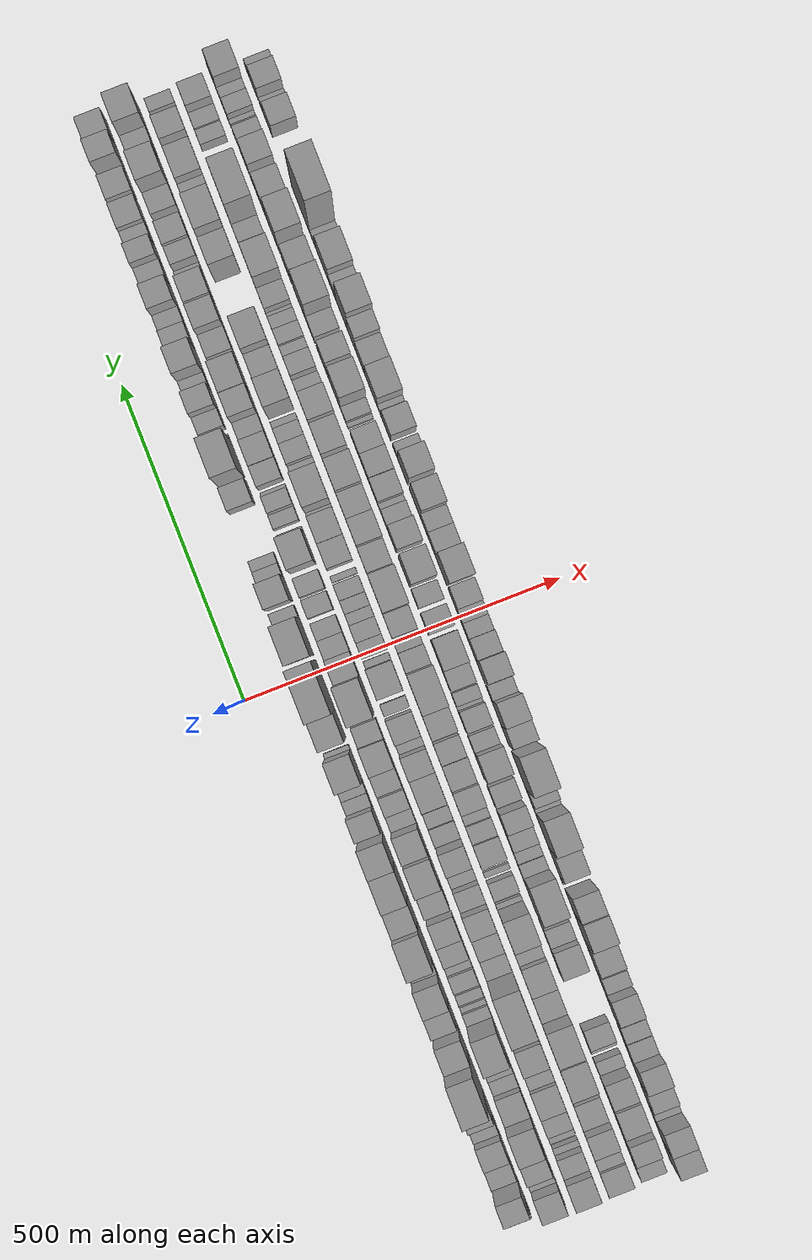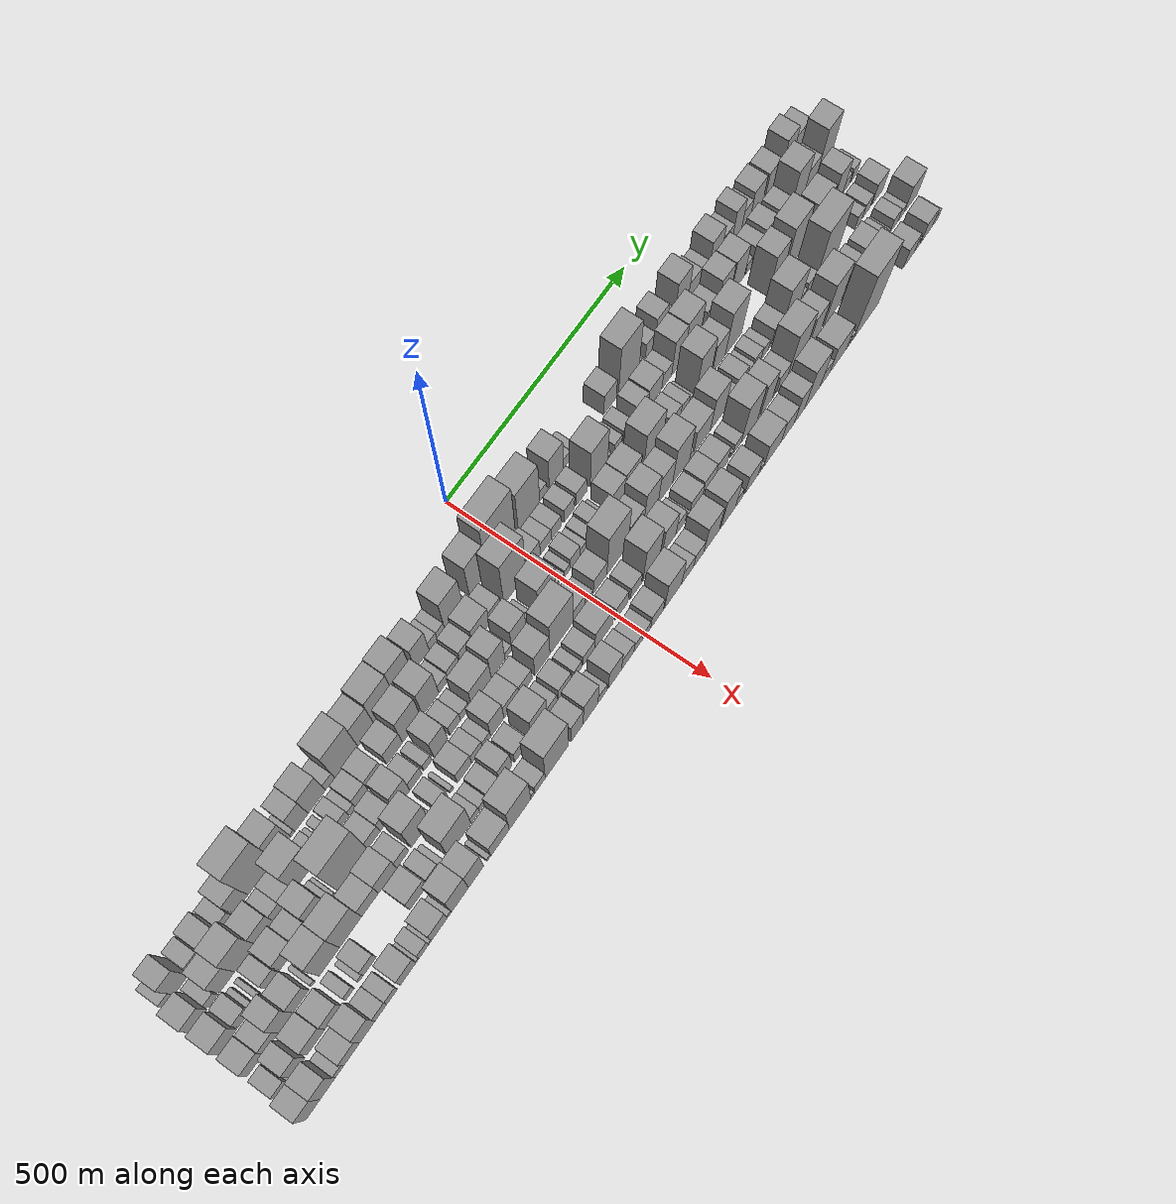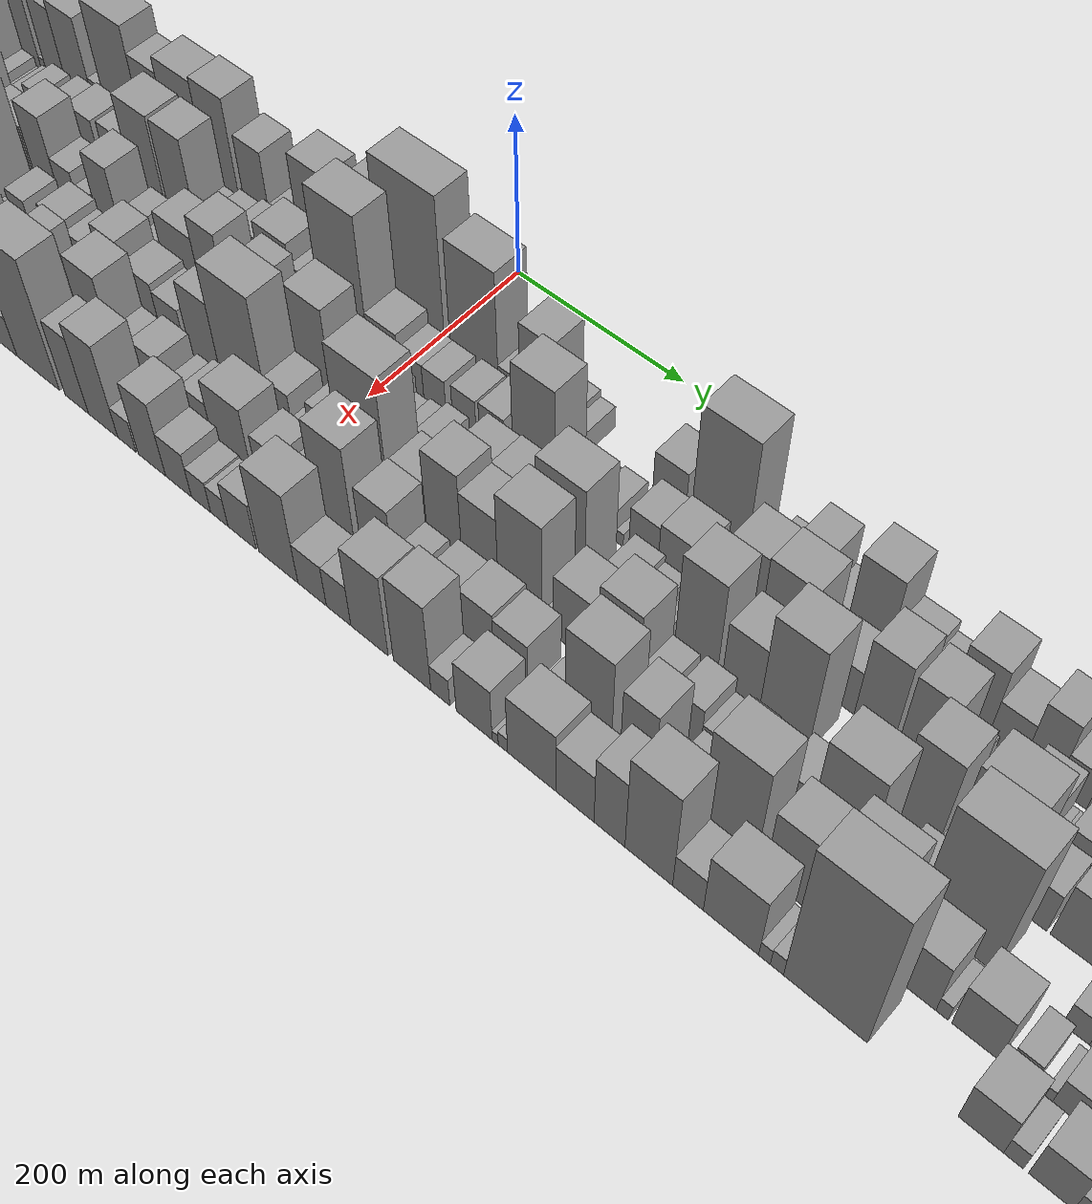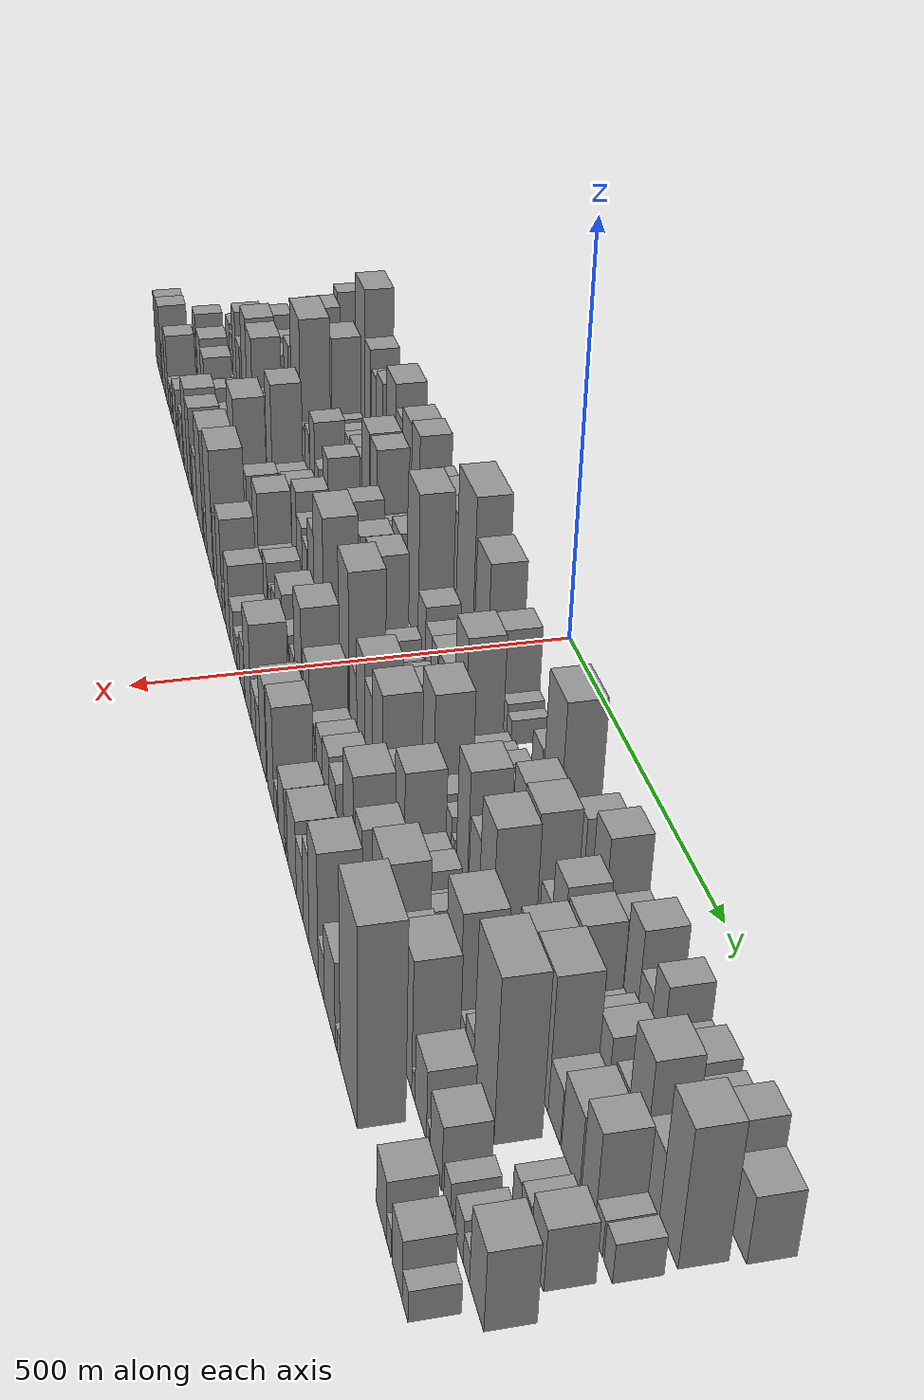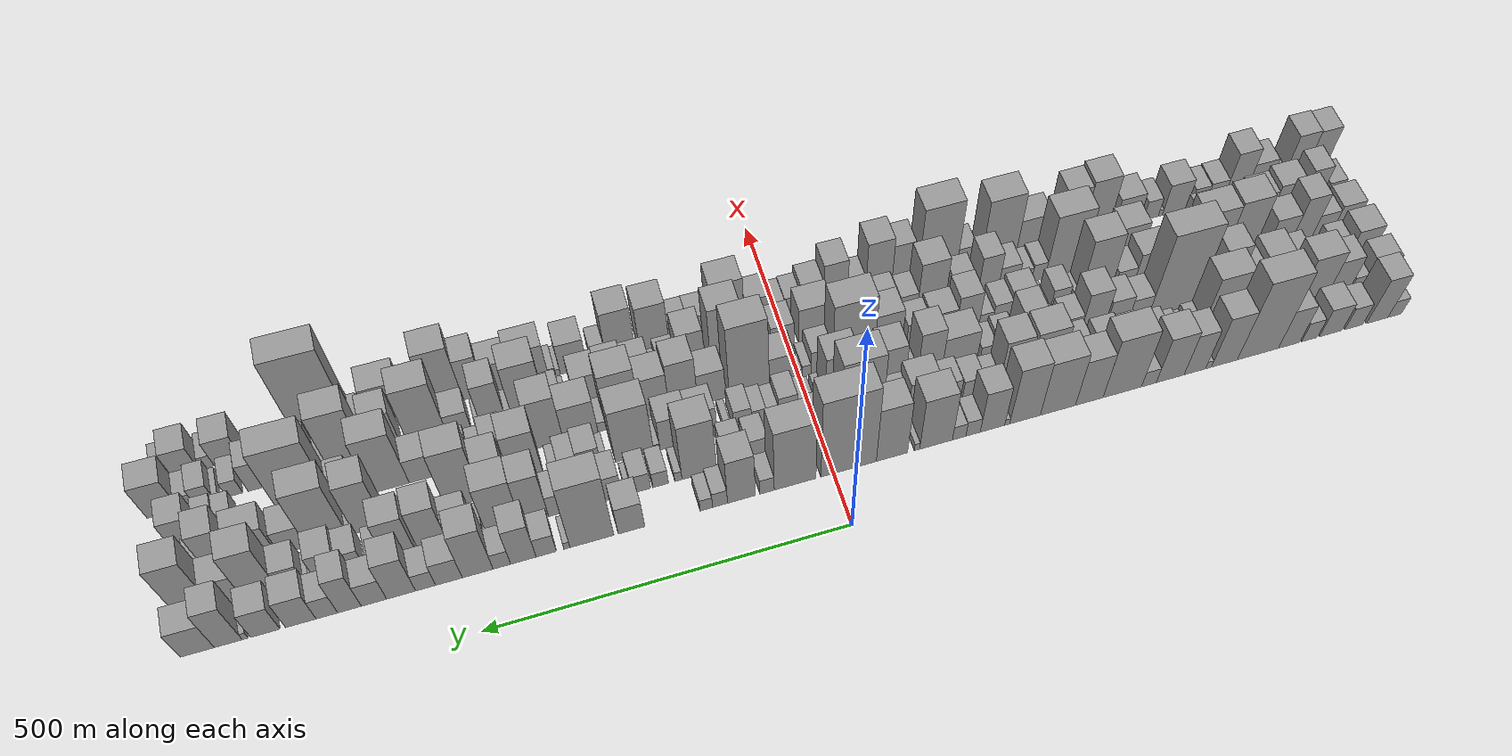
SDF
<sdf version="1.6">
 <world name="default">
  <scene>
   <sky><clouds><speed>12</speed></clouds></sky>
   <ambient>0.4 0.4 0.4 1</ambient>
   <background>0.7 0.7 0.7 1</background>
   <shadows>1</shadows>
  </scene>
  <gravity>0 0 -9.8066</gravity>
  <magnetic_field>6e-06 2.3e-05 -4.2e-05</magnetic_field>
  <physics default="0" name="default_physics" type="ode">
   <ode>
    <solver>
     <type>quick</type>
     <iters>10</iters>
     <sor>1.0</sor>
     <use_dynamic_moi_rescaling>0</use_dynamic_moi_rescaling>
    </solver>
    <constraints>
     <cfm>0</cfm>
     <erp>0.2</erp>
     <contact_max_correcting_vel>100</contact_max_correcting_vel>
     <contact_surface_layer>0.001</contact_surface_layer>
    </constraints>
   </ode>
   <max_step_size>0.004</max_step_size>
   <real_time_factor>1</real_time_factor>
   <real_time_update_rate>250</real_time_update_rate>
  </physics>
  <light name="sun" type="directional">
   <pose>0 0 10 0 0 0</pose>
   <diffuse>0.8 0.8 0.8 1</diffuse>
   <specular>0.2 0.2 0.2 1</specular>
   <attenuation>
    <range>1000</range>
    <constant>0.9</constant>
    <linear>0.01</linear>
    <quadratic>0.001</quadratic>
   </attenuation>
   <direction>-0.5 0.1 -0.9</direction>
  </light>
  <model name="building_1">
   <static>1</static>
   <pose>100.0000 -843.1240 0 0.000000 0.000000 0.000000</pose>
   <link name="link">
    <pose>0 0 21.00 0 0 0</pose>
    <collision name="collision"><geometry><box><size>40.0000 21.7520 42.0000</size></box></geometry></collision>
    <visual name="visual">
     <cast_shadows>0</cast_shadows>
     <geometry><box><size>40.0000 21.7520 42.0000</size></box></geometry>
     <material>
      <script>
       <uri>model://grey_wall/materials/scripts</uri>
       <uri>model://grey_wall/materials/textures</uri>
       <name>vrc/grey_wall</name>
      </script>
     </material>
    </visual>
   </link>
  </model>
  <model name="building_2">
   <static>1</static>
   <pose>100.0000 -815.2978 0 0.000000 0.000000 0.000000</pose>
   <link name="link">
    <pose>0 0 55.50 0 0 0</pose>
    <collision name="collision"><geometry><box><size>40.0000 33.9005 111.0000</size></box></geometry></collision>
    <visual name="visual">
     <cast_shadows>0</cast_shadows>
     <geometry><box><size>40.0000 33.9005 111.0000</size></box></geometry>
     <material>
      <script>
       <uri>model://grey_wall/materials/scripts</uri>
       <uri>model://grey_wall/materials/textures</uri>
       <name>vrc/grey_wall</name>
      </script>
     </material>
    </visual>
   </link>
  </model>
  <model name="building_3">
   <static>1</static>
   <pose>100.0000 -778.2248 0 0.000000 0.000000 0.000000</pose>
   <link name="link">
    <pose>0 0 27.00 0 0 0</pose>
    <collision name="collision"><geometry><box><size>40.0000 28.2455 54.0000</size></box></geometry></collision>
    <visual name="visual">
     <cast_shadows>0</cast_shadows>
     <geometry><box><size>40.0000 28.2455 54.0000</size></box></geometry>
     <material>
      <script>
       <uri>model://grey_wall/materials/scripts</uri>
       <uri>model://grey_wall/materials/textures</uri>
       <name>vrc/grey_wall</name>
      </script>
     </material>
    </visual>
   </link>
  </model>
  <model name="building_4">
   <static>1</static>
   <pose>100.0000 -742.1856 0 0.000000 0.000000 0.000000</pose>
   <link name="link">
    <pose>0 0 34.50 0 0 0</pose>
    <collision name="collision"><geometry><box><size>40.0000 35.8328 69.0000</size></box></geometry></collision>
    <visual name="visual">
     <cast_shadows>0</cast_shadows>
     <geometry><box><size>40.0000 35.8328 69.0000</size></box></geometry>
     <material>
      <script>
       <uri>model://grey_wall/materials/scripts</uri>
       <uri>model://grey_wall/materials/textures</uri>
       <name>vrc/grey_wall</name>
      </script>
     </material>
    </visual>
   </link>
  </model>
  <model name="building_5">
   <static>1</static>
   <pose>100.0000 -708.8529 0 0.000000 0.000000 0.000000</pose>
   <link name="link">
    <pose>0 0 24.00 0 0 0</pose>
    <collision name="collision"><geometry><box><size>40.0000 24.8327 48.0000</size></box></geometry></collision>
    <visual name="visual">
     <cast_shadows>0</cast_shadows>
     <geometry><box><size>40.0000 24.8327 48.0000</size></box></geometry>
     <material>
      <script>
       <uri>model://grey_wall/materials/scripts</uri>
       <uri>model://grey_wall/materials/textures</uri>
       <name>vrc/grey_wall</name>
      </script>
     </material>
    </visual>
   </link>
  </model>
  <model name="building_6">
   <static>1</static>
   <pose>100.0000 -676.8065 0 0.000000 0.000000 0.000000</pose>
   <link name="link">
    <pose>0 0 48.00 0 0 0</pose>
    <collision name="collision"><geometry><box><size>40.0000 33.2600 96.0000</size></box></geometry></collision>
    <visual name="visual">
     <cast_shadows>0</cast_shadows>
     <geometry><box><size>40.0000 33.2600 96.0000</size></box></geometry>
     <material>
      <script>
       <uri>model://grey_wall/materials/scripts</uri>
       <uri>model://grey_wall/materials/textures</uri>
       <name>vrc/grey_wall</name>
      </script>
     </material>
    </visual>
   </link>
  </model>
  <model name="building_7">
   <static>1</static>
   <pose>100.0000 -628.3598 0 0.000000 0.000000 0.000000</pose>
   <link name="link">
    <pose>0 0 97.50 0 0 0</pose>
    <collision name="collision"><geometry><box><size>40.0000 63.6335 195.0000</size></box></geometry></collision>
    <visual name="visual">
     <cast_shadows>0</cast_shadows>
     <geometry><box><size>40.0000 63.6335 195.0000</size></box></geometry>
     <material>
      <script>
       <uri>model://grey_wall/materials/scripts</uri>
       <uri>model://grey_wall/materials/textures</uri>
       <name>vrc/grey_wall</name>
      </script>
     </material>
    </visual>
   </link>
  </model>
  <model name="building_8">
   <static>1</static>
   <pose>100.0000 -576.6208 0 0.000000 0.000000 0.000000</pose>
   <link name="link">
    <pose>0 0 63.00 0 0 0</pose>
    <collision name="collision"><geometry><box><size>40.0000 39.8445 126.0000</size></box></geometry></collision>
    <visual name="visual">
     <cast_shadows>0</cast_shadows>
     <geometry><box><size>40.0000 39.8445 126.0000</size></box></geometry>
     <material>
      <script>
       <uri>model://grey_wall/materials/scripts</uri>
       <uri>model://grey_wall/materials/textures</uri>
       <name>vrc/grey_wall</name>
      </script>
     </material>
    </visual>
   </link>
  </model>
  <model name="building_9">
   <static>1</static>
   <pose>100.0000 -552.2339 0 0.000000 0.000000 0.000000</pose>
   <link name="link">
    <pose>0 0 9.00 0 0 0</pose>
    <collision name="collision"><geometry><box><size>40.0000 8.9292 18.0000</size></box></geometry></collision>
    <visual name="visual">
     <cast_shadows>0</cast_shadows>
     <geometry><box><size>40.0000 8.9292 18.0000</size></box></geometry>
     <material>
      <script>
       <uri>model://grey_wall/materials/scripts</uri>
       <uri>model://grey_wall/materials/textures</uri>
       <name>vrc/grey_wall</name>
      </script>
     </material>
    </visual>
   </link>
  </model>
  <model name="building_10">
   <static>1</static>
   <pose>100.0000 -531.4667 0 0.000000 0.000000 0.000000</pose>
   <link name="link">
    <pose>0 0 51.00 0 0 0</pose>
    <collision name="collision"><geometry><box><size>40.0000 32.6054 102.0000</size></box></geometry></collision>
    <visual name="visual">
     <cast_shadows>0</cast_shadows>
     <geometry><box><size>40.0000 32.6054 102.0000</size></box></geometry>
     <material>
      <script>
       <uri>model://grey_wall/materials/scripts</uri>
       <uri>model://grey_wall/materials/textures</uri>
       <name>vrc/grey_wall</name>
      </script>
     </material>
    </visual>
   </link>
  </model>
  <model name="building_11">
   <static>1</static>
   <pose>100.0000 -494.0086 0 0.000000 0.000000 0.000000</pose>
   <link name="link">
    <pose>0 0 57.00 0 0 0</pose>
    <collision name="collision"><geometry><box><size>40.0000 42.3107 114.0000</size></box></geometry></collision>
    <visual name="visual">
     <cast_shadows>0</cast_shadows>
     <geometry><box><size>40.0000 42.3107 114.0000</size></box></geometry>
     <material>
      <script>
       <uri>model://grey_wall/materials/scripts</uri>
       <uri>model://grey_wall/materials/textures</uri>
       <name>vrc/grey_wall</name>
      </script>
     </material>
    </visual>
   </link>
  </model>
  <model name="building_12">
   <static>1</static>
   <pose>100.0000 -461.6784 0 0.000000 0.000000 0.000000</pose>
   <link name="link">
    <pose>0 0 19.50 0 0 0</pose>
    <collision name="collision"><geometry><box><size>40.0000 22.3498 39.0000</size></box></geometry></collision>
    <visual name="visual">
     <cast_shadows>0</cast_shadows>
     <geometry><box><size>40.0000 22.3498 39.0000</size></box></geometry>
     <material>
      <script>
       <uri>model://grey_wall/materials/scripts</uri>
       <uri>model://grey_wall/materials/textures</uri>
       <name>vrc/grey_wall</name>
      </script>
     </material>
    </visual>
   </link>
  </model>
  <model name="building_13">
   <static>1</static>
   <pose>100.0000 -421.5233 0 0.000000 0.000000 0.000000</pose>
   <link name="link">
    <pose>0 0 75.00 0 0 0</pose>
    <collision name="collision"><geometry><box><size>40.0000 57.9604 150.0000</size></box></geometry></collision>
    <visual name="visual">
     <cast_shadows>0</cast_shadows>
     <geometry><box><size>40.0000 57.9604 150.0000</size></box></geometry>
     <material>
      <script>
       <uri>model://grey_wall/materials/scripts</uri>
       <uri>model://grey_wall/materials/textures</uri>
       <name>vrc/grey_wall</name>
      </script>
     </material>
    </visual>
   </link>
  </model>
  <model name="building_14">
   <static>1</static>
   <pose>100.0000 -371.8786 0 0.000000 0.000000 0.000000</pose>
   <link name="link">
    <pose>0 0 58.50 0 0 0</pose>
    <collision name="collision"><geometry><box><size>40.0000 41.3288 117.0000</size></box></geometry></collision>
    <visual name="visual">
     <cast_shadows>0</cast_shadows>
     <geometry><box><size>40.0000 41.3288 117.0000</size></box></geometry>
     <material>
      <script>
       <uri>model://grey_wall/materials/scripts</uri>
       <uri>model://grey_wall/materials/textures</uri>
       <name>vrc/grey_wall</name>
      </script>
     </material>
    </visual>
   </link>
  </model>
  <model name="building_15">
   <static>1</static>
   <pose>100.0000 -325.0603 0 0.000000 0.000000 0.000000</pose>
   <link name="link">
    <pose>0 0 69.00 0 0 0</pose>
    <collision name="collision"><geometry><box><size>40.0000 52.3078 138.0000</size></box></geometry></collision>
    <visual name="visual">
     <cast_shadows>0</cast_shadows>
     <geometry><box><size>40.0000 52.3078 138.0000</size></box></geometry>
     <material>
      <script>
       <uri>model://grey_wall/materials/scripts</uri>
       <uri>model://grey_wall/materials/textures</uri>
       <name>vrc/grey_wall</name>
      </script>
     </material>
    </visual>
   </link>
  </model>
  <model name="building_16">
   <static>1</static>
   <pose>100.0000 -276.4552 0 0.000000 0.000000 0.000000</pose>
   <link name="link">
    <pose>0 0 72.00 0 0 0</pose>
    <collision name="collision"><geometry><box><size>40.0000 44.9025 144.0000</size></box></geometry></collision>
    <visual name="visual">
     <cast_shadows>0</cast_shadows>
     <geometry><box><size>40.0000 44.9025 144.0000</size></box></geometry>
     <material>
      <script>
       <uri>model://grey_wall/materials/scripts</uri>
       <uri>model://grey_wall/materials/textures</uri>
       <name>vrc/grey_wall</name>
      </script>
     </material>
    </visual>
   </link>
  </model>
  <model name="building_17">
   <static>1</static>
   <pose>100.0000 -250.2787 0 0.000000 0.000000 0.000000</pose>
   <link name="link">
    <pose>0 0 7.50 0 0 0</pose>
    <collision name="collision"><geometry><box><size>40.0000 7.4505 15.0000</size></box></geometry></collision>
    <visual name="visual">
     <cast_shadows>0</cast_shadows>
     <geometry><box><size>40.0000 7.4505 15.0000</size></box></geometry>
     <material>
      <script>
       <uri>model://grey_wall/materials/scripts</uri>
       <uri>model://grey_wall/materials/textures</uri>
       <name>vrc/grey_wall</name>
      </script>
     </material>
    </visual>
   </link>
  </model>
  <model name="building_18">
   <static>1</static>
   <pose>100.0000 -228.5596 0 0.000000 0.000000 0.000000</pose>
   <link name="link">
    <pose>0 0 52.50 0 0 0</pose>
    <collision name="collision"><geometry><box><size>40.0000 35.9877 105.0000</size></box></geometry></collision>
    <visual name="visual">
     <cast_shadows>0</cast_shadows>
     <geometry><box><size>40.0000 35.9877 105.0000</size></box></geometry>
     <material>
      <script>
       <uri>model://grey_wall/materials/scripts</uri>
       <uri>model://grey_wall/materials/textures</uri>
       <name>vrc/grey_wall</name>
      </script>
     </material>
    </visual>
   </link>
  </model>
  <model name="building_19">
   <static>1</static>
   <pose>100.0000 -200.0967 0 0.000000 0.000000 0.000000</pose>
   <link name="link">
    <pose>0 0 19.50 0 0 0</pose>
    <collision name="collision"><geometry><box><size>40.0000 20.9381 39.0000</size></box></geometry></collision>
    <visual name="visual">
     <cast_shadows>0</cast_shadows>
     <geometry><box><size>40.0000 20.9381 39.0000</size></box></geometry>
     <material>
      <script>
       <uri>model://grey_wall/materials/scripts</uri>
       <uri>model://grey_wall/materials/textures</uri>
       <name>vrc/grey_wall</name>
      </script>
     </material>
    </visual>
   </link>
  </model>
  <model name="building_20">
   <static>1</static>
   <pose>100.0000 -179.8525 0 0.000000 0.000000 0.000000</pose>
   <link name="link">
    <pose>0 0 18.00 0 0 0</pose>
    <collision name="collision"><geometry><box><size>40.0000 19.5503 36.0000</size></box></geometry></collision>
    <visual name="visual">
     <cast_shadows>0</cast_shadows>
     <geometry><box><size>40.0000 19.5503 36.0000</size></box></geometry>
     <material>
      <script>
       <uri>model://grey_wall/materials/scripts</uri>
       <uri>model://grey_wall/materials/textures</uri>
       <name>vrc/grey_wall</name>
      </script>
     </material>
    </visual>
   </link>
  </model>
  <model name="building_21">
   <static>1</static>
   <pose>100.0000 -146.3669 0 0.000000 0.000000 0.000000</pose>
   <link name="link">
    <pose>0 0 66.00 0 0 0</pose>
    <collision name="collision"><geometry><box><size>40.0000 47.4209 132.0000</size></box></geometry></collision>
    <visual name="visual">
     <cast_shadows>0</cast_shadows>
     <geometry><box><size>40.0000 47.4209 132.0000</size></box></geometry>
     <material>
      <script>
       <uri>model://grey_wall/materials/scripts</uri>
       <uri>model://grey_wall/materials/textures</uri>
       <name>vrc/grey_wall</name>
      </script>
     </material>
    </visual>
   </link>
  </model>
  <model name="building_22">
   <static>1</static>
   <pose>100.0000 -118.8623 0 0.000000 0.000000 0.000000</pose>
   <link name="link">
    <pose>0 0 9.00 0 0 0</pose>
    <collision name="collision"><geometry><box><size>40.0000 7.5882 18.0000</size></box></geometry></collision>
    <visual name="visual">
     <cast_shadows>0</cast_shadows>
     <geometry><box><size>40.0000 7.5882 18.0000</size></box></geometry>
     <material>
      <script>
       <uri>model://grey_wall/materials/scripts</uri>
       <uri>model://grey_wall/materials/textures</uri>
       <name>vrc/grey_wall</name>
      </script>
     </material>
    </visual>
   </link>
  </model>
  <model name="building_23">
   <static>1</static>
   <pose>100.0000 -82.6752 0 0.000000 0.000000 0.000000</pose>
   <link name="link">
    <pose>0 0 70.50 0 0 0</pose>
    <collision name="collision"><geometry><box><size>40.0000 44.7859 141.0000</size></box></geometry></collision>
    <visual name="visual">
     <cast_shadows>0</cast_shadows>
     <geometry><box><size>40.0000 44.7859 141.0000</size></box></geometry>
     <material>
      <script>
       <uri>model://grey_wall/materials/scripts</uri>
       <uri>model://grey_wall/materials/textures</uri>
       <name>vrc/grey_wall</name>
      </script>
     </material>
    </visual>
   </link>
  </model>
  <model name="building_24">
   <static>1</static>
   <pose>100.0000 -20.8004 0 0.000000 0.000000 0.000000</pose>
   <link name="link">
    <pose>0 0 102.00 0 0 0</pose>
    <collision name="collision"><geometry><box><size>40.0000 78.9638 204.0000</size></box></geometry></collision>
    <visual name="visual">
     <cast_shadows>0</cast_shadows>
     <geometry><box><size>40.0000 78.9638 204.0000</size></box></geometry>
     <material>
      <script>
       <uri>model://grey_wall/materials/scripts</uri>
       <uri>model://grey_wall/materials/textures</uri>
       <name>vrc/grey_wall</name>
      </script>
     </material>
    </visual>
   </link>
  </model>
  <model name="building_25">
   <static>1</static>
   <pose>100.0000 55.0314 0 0.000000 0.000000 0.000000</pose>
   <link name="link">
    <pose>0 0 79.50 0 0 0</pose>
    <collision name="collision"><geometry><box><size>40.0000 58.6997 159.0000</size></box></geometry></collision>
    <visual name="visual">
     <cast_shadows>0</cast_shadows>
     <geometry><box><size>40.0000 58.6997 159.0000</size></box></geometry>
     <material>
      <script>
       <uri>model://grey_wall/materials/scripts</uri>
       <uri>model://grey_wall/materials/textures</uri>
       <name>vrc/grey_wall</name>
      </script>
     </material>
    </visual>
   </link>
  </model>
  <model name="building_26">
   <static>1</static>
   <pose>100.0000 94.5070 0 0.000000 0.000000 0.000000</pose>
   <link name="link">
    <pose>0 0 19.50 0 0 0</pose>
    <collision name="collision"><geometry><box><size>40.0000 20.2516 39.0000</size></box></geometry></collision>
    <visual name="visual">
     <cast_shadows>0</cast_shadows>
     <geometry><box><size>40.0000 20.2516 39.0000</size></box></geometry>
     <material>
      <script>
       <uri>model://grey_wall/materials/scripts</uri>
       <uri>model://grey_wall/materials/textures</uri>
       <name>vrc/grey_wall</name>
      </script>
     </material>
    </visual>
   </link>
  </model>
  <model name="building_27">
   <static>1</static>
   <pose>100.0000 130.1339 0 0.000000 0.000000 0.000000</pose>
   <link name="link">
    <pose>0 0 58.50 0 0 0</pose>
    <collision name="collision"><geometry><box><size>40.0000 39.0021 117.0000</size></box></geometry></collision>
    <visual name="visual">
     <cast_shadows>0</cast_shadows>
     <geometry><box><size>40.0000 39.0021 117.0000</size></box></geometry>
     <material>
      <script>
       <uri>model://grey_wall/materials/scripts</uri>
       <uri>model://grey_wall/materials/textures</uri>
       <name>vrc/grey_wall</name>
      </script>
     </material>
    </visual>
   </link>
  </model>
  <model name="building_28">
   <static>1</static>
   <pose>100.0000 159.9920 0 0.000000 0.000000 0.000000</pose>
   <link name="link">
    <pose>0 0 19.50 0 0 0</pose>
    <collision name="collision"><geometry><box><size>40.0000 20.7141 39.0000</size></box></geometry></collision>
    <visual name="visual">
     <cast_shadows>0</cast_shadows>
     <geometry><box><size>40.0000 20.7141 39.0000</size></box></geometry>
     <material>
      <script>
       <uri>model://grey_wall/materials/scripts</uri>
       <uri>model://grey_wall/materials/textures</uri>
       <name>vrc/grey_wall</name>
      </script>
     </material>
    </visual>
   </link>
  </model>
  <model name="building_29">
   <static>1</static>
   <pose>100.0000 178.9773 0 0.000000 0.000000 0.000000</pose>
   <link name="link">
    <pose>0 0 15.00 0 0 0</pose>
    <collision name="collision"><geometry><box><size>40.0000 17.2565 30.0000</size></box></geometry></collision>
    <visual name="visual">
     <cast_shadows>0</cast_shadows>
     <geometry><box><size>40.0000 17.2565 30.0000</size></box></geometry>
     <material>
      <script>
       <uri>model://grey_wall/materials/scripts</uri>
       <uri>model://grey_wall/materials/textures</uri>
       <name>vrc/grey_wall</name>
      </script>
     </material>
    </visual>
   </link>
  </model>
  <model name="building_30">
   <static>1</static>
   <pose>100.0000 281.8480 0 0.000000 0.000000 0.000000</pose>
   <link name="link">
    <pose>0 0 36.00 0 0 0</pose>
    <collision name="collision"><geometry><box><size>40.0000 36.1616 72.0000</size></box></geometry></collision>
    <visual name="visual">
     <cast_shadows>0</cast_shadows>
     <geometry><box><size>40.0000 36.1616 72.0000</size></box></geometry>
     <material>
      <script>
       <uri>model://grey_wall/materials/scripts</uri>
       <uri>model://grey_wall/materials/textures</uri>
       <name>vrc/grey_wall</name>
      </script>
     </material>
    </visual>
   </link>
  </model>
  <model name="building_31">
   <static>1</static>
   <pose>100.0000 335.6738 0 0.000000 0.000000 0.000000</pose>
   <link name="link">
    <pose>0 0 85.50 0 0 0</pose>
    <collision name="collision"><geometry><box><size>40.0000 59.4901 171.0000</size></box></geometry></collision>
    <visual name="visual">
     <cast_shadows>0</cast_shadows>
     <geometry><box><size>40.0000 59.4901 171.0000</size></box></geometry>
     <material>
      <script>
       <uri>model://grey_wall/materials/scripts</uri>
       <uri>model://grey_wall/materials/textures</uri>
       <name>vrc/grey_wall</name>
      </script>
     </material>
    </visual>
   </link>
  </model>
  <model name="building_32">
   <static>1</static>
   <pose>100.0000 369.5305 0 0.000000 0.000000 0.000000</pose>
   <link name="link">
    <pose>0 0 9.00 0 0 0</pose>
    <collision name="collision"><geometry><box><size>40.0000 8.2232 18.0000</size></box></geometry></collision>
    <visual name="visual">
     <cast_shadows>0</cast_shadows>
     <geometry><box><size>40.0000 8.2232 18.0000</size></box></geometry>
     <material>
      <script>
       <uri>model://grey_wall/materials/scripts</uri>
       <uri>model://grey_wall/materials/textures</uri>
       <name>vrc/grey_wall</name>
      </script>
     </material>
    </visual>
   </link>
  </model>
  <model name="building_33">
   <static>1</static>
   <pose>100.0000 397.2680 0 0.000000 0.000000 0.000000</pose>
   <link name="link">
    <pose>0 0 25.50 0 0 0</pose>
    <collision name="collision"><geometry><box><size>40.0000 27.2518 51.0000</size></box></geometry></collision>
    <visual name="visual">
     <cast_shadows>0</cast_shadows>
     <geometry><box><size>40.0000 27.2518 51.0000</size></box></geometry>
     <material>
      <script>
       <uri>model://grey_wall/materials/scripts</uri>
       <uri>model://grey_wall/materials/textures</uri>
       <name>vrc/grey_wall</name>
      </script>
     </material>
    </visual>
   </link>
  </model>
  <model name="building_34">
   <static>1</static>
   <pose>100.0000 427.9122 0 0.000000 0.000000 0.000000</pose>
   <link name="link">
    <pose>0 0 48.00 0 0 0</pose>
    <collision name="collision"><geometry><box><size>40.0000 34.0366 96.0000</size></box></geometry></collision>
    <visual name="visual">
     <cast_shadows>0</cast_shadows>
     <geometry><box><size>40.0000 34.0366 96.0000</size></box></geometry>
     <material>
      <script>
       <uri>model://grey_wall/materials/scripts</uri>
       <uri>model://grey_wall/materials/textures</uri>
       <name>vrc/grey_wall</name>
      </script>
     </material>
    </visual>
   </link>
  </model>
  <model name="building_35">
   <static>1</static>
   <pose>100.0000 456.6429 0 0.000000 0.000000 0.000000</pose>
   <link name="link">
    <pose>0 0 21.00 0 0 0</pose>
    <collision name="collision"><geometry><box><size>40.0000 23.4248 42.0000</size></box></geometry></collision>
    <visual name="visual">
     <cast_shadows>0</cast_shadows>
     <geometry><box><size>40.0000 23.4248 42.0000</size></box></geometry>
     <material>
      <script>
       <uri>model://grey_wall/materials/scripts</uri>
       <uri>model://grey_wall/materials/textures</uri>
       <name>vrc/grey_wall</name>
      </script>
     </material>
    </visual>
   </link>
  </model>
  <model name="building_36">
   <static>1</static>
   <pose>100.0000 488.7600 0 0.000000 0.000000 0.000000</pose>
   <link name="link">
    <pose>0 0 61.50 0 0 0</pose>
    <collision name="collision"><geometry><box><size>40.0000 40.8094 123.0000</size></box></geometry></collision>
    <visual name="visual">
     <cast_shadows>0</cast_shadows>
     <geometry><box><size>40.0000 40.8094 123.0000</size></box></geometry>
     <material>
      <script>
       <uri>model://grey_wall/materials/scripts</uri>
       <uri>model://grey_wall/materials/textures</uri>
       <name>vrc/grey_wall</name>
      </script>
     </material>
    </visual>
   </link>
  </model>
  <model name="building_37">
   <static>1</static>
   <pose>100.0000 526.7805 0 0.000000 0.000000 0.000000</pose>
   <link name="link">
    <pose>0 0 30.00 0 0 0</pose>
    <collision name="collision"><geometry><box><size>40.0000 35.2316 60.0000</size></box></geometry></collision>
    <visual name="visual">
     <cast_shadows>0</cast_shadows>
     <geometry><box><size>40.0000 35.2316 60.0000</size></box></geometry>
     <material>
      <script>
       <uri>model://grey_wall/materials/scripts</uri>
       <uri>model://grey_wall/materials/textures</uri>
       <name>vrc/grey_wall</name>
      </script>
     </material>
    </visual>
   </link>
  </model>
  <model name="building_38">
   <static>1</static>
   <pose>100.0000 557.5161 0 0.000000 0.000000 0.000000</pose>
   <link name="link">
    <pose>0 0 22.50 0 0 0</pose>
    <collision name="collision"><geometry><box><size>40.0000 26.2396 45.0000</size></box></geometry></collision>
    <visual name="visual">
     <cast_shadows>0</cast_shadows>
     <geometry><box><size>40.0000 26.2396 45.0000</size></box></geometry>
     <material>
      <script>
       <uri>model://grey_wall/materials/scripts</uri>
       <uri>model://grey_wall/materials/textures</uri>
       <name>vrc/grey_wall</name>
      </script>
     </material>
    </visual>
   </link>
  </model>
  <model name="building_39">
   <static>1</static>
   <pose>100.0000 589.5145 0 0.000000 0.000000 0.000000</pose>
   <link name="link">
    <pose>0 0 51.00 0 0 0</pose>
    <collision name="collision"><geometry><box><size>40.0000 37.7572 102.0000</size></box></geometry></collision>
    <visual name="visual">
     <cast_shadows>0</cast_shadows>
     <geometry><box><size>40.0000 37.7572 102.0000</size></box></geometry>
     <material>
      <script>
       <uri>model://grey_wall/materials/scripts</uri>
       <uri>model://grey_wall/materials/textures</uri>
       <name>vrc/grey_wall</name>
      </script>
     </material>
    </visual>
   </link>
  </model>
  <model name="building_40">
   <static>1</static>
   <pose>100.0000 624.8641 0 0.000000 0.000000 0.000000</pose>
   <link name="link">
    <pose>0 0 30.00 0 0 0</pose>
    <collision name="collision"><geometry><box><size>40.0000 32.9421 60.0000</size></box></geometry></collision>
    <visual name="visual">
     <cast_shadows>0</cast_shadows>
     <geometry><box><size>40.0000 32.9421 60.0000</size></box></geometry>
     <material>
      <script>
       <uri>model://grey_wall/materials/scripts</uri>
       <uri>model://grey_wall/materials/textures</uri>
       <name>vrc/grey_wall</name>
      </script>
     </material>
    </visual>
   </link>
  </model>
  <model name="building_41">
   <static>1</static>
   <pose>100.0000 656.6407 0 0.000000 0.000000 0.000000</pose>
   <link name="link">
    <pose>0 0 48.00 0 0 0</pose>
    <collision name="collision"><geometry><box><size>40.0000 30.6110 96.0000</size></box></geometry></collision>
    <visual name="visual">
     <cast_shadows>0</cast_shadows>
     <geometry><box><size>40.0000 30.6110 96.0000</size></box></geometry>
     <material>
      <script>
       <uri>model://grey_wall/materials/scripts</uri>
       <uri>model://grey_wall/materials/textures</uri>
       <name>vrc/grey_wall</name>
      </script>
     </material>
    </visual>
   </link>
  </model>
  <model name="building_42">
   <static>1</static>
   <pose>100.0000 685.8209 0 0.000000 0.000000 0.000000</pose>
   <link name="link">
    <pose>0 0 27.00 0 0 0</pose>
    <collision name="collision"><geometry><box><size>40.0000 27.7494 54.0000</size></box></geometry></collision>
    <visual name="visual">
     <cast_shadows>0</cast_shadows>
     <geometry><box><size>40.0000 27.7494 54.0000</size></box></geometry>
     <material>
      <script>
       <uri>model://grey_wall/materials/scripts</uri>
       <uri>model://grey_wall/materials/textures</uri>
       <name>vrc/grey_wall</name>
      </script>
     </material>
    </visual>
   </link>
  </model>
  <model name="building_43">
   <static>1</static>
   <pose>100.0000 719.2941 0 0.000000 0.000000 0.000000</pose>
   <link name="link">
    <pose>0 0 37.50 0 0 0</pose>
    <collision name="collision"><geometry><box><size>40.0000 39.1970 75.0000</size></box></geometry></collision>
    <visual name="visual">
     <cast_shadows>0</cast_shadows>
     <geometry><box><size>40.0000 39.1970 75.0000</size></box></geometry>
     <material>
      <script>
       <uri>model://grey_wall/materials/scripts</uri>
       <uri>model://grey_wall/materials/textures</uri>
       <name>vrc/grey_wall</name>
      </script>
     </material>
    </visual>
   </link>
  </model>
  <model name="building_44">
   <static>1</static>
   <pose>100.0000 764.7186 0 0.000000 0.000000 0.000000</pose>
   <link name="link">
    <pose>0 0 34.50 0 0 0</pose>
    <collision name="collision"><geometry><box><size>40.0000 37.6518 69.0000</size></box></geometry></collision>
    <visual name="visual">
     <cast_shadows>0</cast_shadows>
     <geometry><box><size>40.0000 37.6518 69.0000</size></box></geometry>
     <material>
      <script>
       <uri>model://grey_wall/materials/scripts</uri>
       <uri>model://grey_wall/materials/textures</uri>
       <name>vrc/grey_wall</name>
      </script>
     </material>
    </visual>
   </link>
  </model>
  <model name="building_45">
   <static>1</static>
   <pose>100.0000 790.2598 0 0.000000 0.000000 0.000000</pose>
   <link name="link">
    <pose>0 0 9.00 0 0 0</pose>
    <collision name="collision"><geometry><box><size>40.0000 7.4306 18.0000</size></box></geometry></collision>
    <visual name="visual">
     <cast_shadows>0</cast_shadows>
     <geometry><box><size>40.0000 7.4306 18.0000</size></box></geometry>
     <material>
      <script>
       <uri>model://grey_wall/materials/scripts</uri>
       <uri>model://grey_wall/materials/textures</uri>
       <name>vrc/grey_wall</name>
      </script>
     </material>
    </visual>
   </link>
  </model>
  <model name="building_46">
   <static>1</static>
   <pose>100.0000 811.5840 0 0.000000 0.000000 0.000000</pose>
   <link name="link">
    <pose>0 0 52.50 0 0 0</pose>
    <collision name="collision"><geometry><box><size>40.0000 35.2179 105.0000</size></box></geometry></collision>
    <visual name="visual">
     <cast_shadows>0</cast_shadows>
     <geometry><box><size>40.0000 35.2179 105.0000</size></box></geometry>
     <material>
      <script>
       <uri>model://grey_wall/materials/scripts</uri>
       <uri>model://grey_wall/materials/textures</uri>
       <name>vrc/grey_wall</name>
      </script>
     </material>
    </visual>
   </link>
  </model>
  <model name="building_47">
   <static>1</static>
   <pose>100.0000 850.7482 0 0.000000 0.000000 0.000000</pose>
   <link name="link">
    <pose>0 0 36.00 0 0 0</pose>
    <collision name="collision"><geometry><box><size>40.0000 43.1106 72.0000</size></box></geometry></collision>
    <visual name="visual">
     <cast_shadows>0</cast_shadows>
     <geometry><box><size>40.0000 43.1106 72.0000</size></box></geometry>
     <material>
      <script>
       <uri>model://grey_wall/materials/scripts</uri>
       <uri>model://grey_wall/materials/textures</uri>
       <name>vrc/grey_wall</name>
      </script>
     </material>
    </visual>
   </link>
  </model>
  <model name="building_48">
   <static>1</static>
   <pose>152.0000 -840.8286 0 0.000000 0.000000 0.000000</pose>
   <link name="link">
    <pose>0 0 36.00 0 0 0</pose>
    <collision name="collision"><geometry><box><size>40.0000 38.3429 72.0000</size></box></geometry></collision>
    <visual name="visual">
     <cast_shadows>0</cast_shadows>
     <geometry><box><size>40.0000 38.3429 72.0000</size></box></geometry>
     <material>
      <script>
       <uri>model://grey_wall/materials/scripts</uri>
       <uri>model://grey_wall/materials/textures</uri>
       <name>vrc/grey_wall</name>
      </script>
     </material>
    </visual>
   </link>
  </model>
  <model name="building_49">
   <static>1</static>
   <pose>152.0000 -806.8243 0 0.000000 0.000000 0.000000</pose>
   <link name="link">
    <pose>0 0 21.00 0 0 0</pose>
    <collision name="collision"><geometry><box><size>40.0000 21.6656 42.0000</size></box></geometry></collision>
    <visual name="visual">
     <cast_shadows>0</cast_shadows>
     <geometry><box><size>40.0000 21.6656 42.0000</size></box></geometry>
     <material>
      <script>
       <uri>model://grey_wall/materials/scripts</uri>
       <uri>model://grey_wall/materials/textures</uri>
       <name>vrc/grey_wall</name>
      </script>
     </material>
    </visual>
   </link>
  </model>
  <model name="building_50">
   <static>1</static>
   <pose>152.0000 -775.1812 0 0.000000 0.000000 0.000000</pose>
   <link name="link">
    <pose>0 0 49.50 0 0 0</pose>
    <collision name="collision"><geometry><box><size>40.0000 35.6205 99.0000</size></box></geometry></collision>
    <visual name="visual">
     <cast_shadows>0</cast_shadows>
     <geometry><box><size>40.0000 35.6205 99.0000</size></box></geometry>
     <material>
      <script>
       <uri>model://grey_wall/materials/scripts</uri>
       <uri>model://grey_wall/materials/textures</uri>
       <name>vrc/grey_wall</name>
      </script>
     </material>
    </visual>
   </link>
  </model>
  <model name="building_51">
   <static>1</static>
   <pose>152.0000 -733.4415 0 0.000000 0.000000 0.000000</pose>
   <link name="link">
    <pose>0 0 63.00 0 0 0</pose>
    <collision name="collision"><geometry><box><size>40.0000 47.8591 126.0000</size></box></geometry></collision>
    <visual name="visual">
     <cast_shadows>0</cast_shadows>
     <geometry><box><size>40.0000 47.8591 126.0000</size></box></geometry>
     <material>
      <script>
       <uri>model://grey_wall/materials/scripts</uri>
       <uri>model://grey_wall/materials/textures</uri>
       <name>vrc/grey_wall</name>
      </script>
     </material>
    </visual>
   </link>
  </model>
  <model name="building_52">
   <static>1</static>
   <pose>152.0000 -688.9490 0 0.000000 0.000000 0.000000</pose>
   <link name="link">
    <pose>0 0 34.50 0 0 0</pose>
    <collision name="collision"><geometry><box><size>40.0000 41.1259 69.0000</size></box></geometry></collision>
    <visual name="visual">
     <cast_shadows>0</cast_shadows>
     <geometry><box><size>40.0000 41.1259 69.0000</size></box></geometry>
     <material>
      <script>
       <uri>model://grey_wall/materials/scripts</uri>
       <uri>model://grey_wall/materials/textures</uri>
       <name>vrc/grey_wall</name>
      </script>
     </material>
    </visual>
   </link>
  </model>
  <model name="building_53">
   <static>1</static>
   <pose>152.0000 -656.1648 0 0.000000 0.000000 0.000000</pose>
   <link name="link">
    <pose>0 0 21.00 0 0 0</pose>
    <collision name="collision"><geometry><box><size>40.0000 24.4425 42.0000</size></box></geometry></collision>
    <visual name="visual">
     <cast_shadows>0</cast_shadows>
     <geometry><box><size>40.0000 24.4425 42.0000</size></box></geometry>
     <material>
      <script>
       <uri>model://grey_wall/materials/scripts</uri>
       <uri>model://grey_wall/materials/textures</uri>
       <name>vrc/grey_wall</name>
      </script>
     </material>
    </visual>
   </link>
  </model>
  <model name="building_54">
   <static>1</static>
   <pose>152.0000 -629.5401 0 0.000000 0.000000 0.000000</pose>
   <link name="link">
    <pose>0 0 27.00 0 0 0</pose>
    <collision name="collision"><geometry><box><size>40.0000 28.8069 54.0000</size></box></geometry></collision>
    <visual name="visual">
     <cast_shadows>0</cast_shadows>
     <geometry><box><size>40.0000 28.8069 54.0000</size></box></geometry>
     <material>
      <script>
       <uri>model://grey_wall/materials/scripts</uri>
       <uri>model://grey_wall/materials/textures</uri>
       <name>vrc/grey_wall</name>
      </script>
     </material>
    </visual>
   </link>
  </model>
  <model name="building_55">
   <static>1</static>
   <pose>152.0000 -588.4595 0 0.000000 0.000000 0.000000</pose>
   <link name="link">
    <pose>0 0 72.00 0 0 0</pose>
    <collision name="collision"><geometry><box><size>40.0000 53.3543 144.0000</size></box></geometry></collision>
    <visual name="visual">
     <cast_shadows>0</cast_shadows>
     <geometry><box><size>40.0000 53.3543 144.0000</size></box></geometry>
     <material>
      <script>
       <uri>model://grey_wall/materials/scripts</uri>
       <uri>model://grey_wall/materials/textures</uri>
       <name>vrc/grey_wall</name>
      </script>
     </material>
    </visual>
   </link>
  </model>
  <model name="building_56">
   <static>1</static>
   <pose>152.0000 -552.4265 0 0.000000 0.000000 0.000000</pose>
   <link name="link">
    <pose>0 0 16.50 0 0 0</pose>
    <collision name="collision"><geometry><box><size>40.0000 18.7116 33.0000</size></box></geometry></collision>
    <visual name="visual">
     <cast_shadows>0</cast_shadows>
     <geometry><box><size>40.0000 18.7116 33.0000</size></box></geometry>
     <material>
      <script>
       <uri>model://grey_wall/materials/scripts</uri>
       <uri>model://grey_wall/materials/textures</uri>
       <name>vrc/grey_wall</name>
      </script>
     </material>
    </visual>
   </link>
  </model>
  <model name="building_57">
   <static>1</static>
   <pose>152.0000 -538.7161 0 0.000000 0.000000 0.000000</pose>
   <link name="link">
    <pose>0 0 10.50 0 0 0</pose>
    <collision name="collision"><geometry><box><size>40.0000 8.7092 21.0000</size></box></geometry></collision>
    <visual name="visual">
     <cast_shadows>0</cast_shadows>
     <geometry><box><size>40.0000 8.7092 21.0000</size></box></geometry>
     <material>
      <script>
       <uri>model://grey_wall/materials/scripts</uri>
       <uri>model://grey_wall/materials/textures</uri>
       <name>vrc/grey_wall</name>
      </script>
     </material>
    </visual>
   </link>
  </model>
  <model name="building_58">
   <static>1</static>
   <pose>152.0000 -522.2402 0 0.000000 0.000000 0.000000</pose>
   <link name="link">
    <pose>0 0 15.00 0 0 0</pose>
    <collision name="collision"><geometry><box><size>40.0000 16.2424 30.0000</size></box></geometry></collision>
    <visual name="visual">
     <cast_shadows>0</cast_shadows>
     <geometry><box><size>40.0000 16.2424 30.0000</size></box></geometry>
     <material>
      <script>
       <uri>model://grey_wall/materials/scripts</uri>
       <uri>model://grey_wall/materials/textures</uri>
       <name>vrc/grey_wall</name>
      </script>
     </material>
    </visual>
   </link>
  </model>
  <model name="building_59">
   <static>1</static>
   <pose>152.0000 -496.1585 0 0.000000 0.000000 0.000000</pose>
   <link name="link">
    <pose>0 0 22.50 0 0 0</pose>
    <collision name="collision"><geometry><box><size>40.0000 25.9210 45.0000</size></box></geometry></collision>
    <visual name="visual">
     <cast_shadows>0</cast_shadows>
     <geometry><box><size>40.0000 25.9210 45.0000</size></box></geometry>
     <material>
      <script>
       <uri>model://grey_wall/materials/scripts</uri>
       <uri>model://grey_wall/materials/textures</uri>
       <name>vrc/grey_wall</name>
      </script>
     </material>
    </visual>
   </link>
  </model>
  <model name="building_60">
   <static>1</static>
   <pose>152.0000 -475.3873 0 0.000000 0.000000 0.000000</pose>
   <link name="link">
    <pose>0 0 15.00 0 0 0</pose>
    <collision name="collision"><geometry><box><size>40.0000 15.6216 30.0000</size></box></geometry></collision>
    <visual name="visual">
     <cast_shadows>0</cast_shadows>
     <geometry><box><size>40.0000 15.6216 30.0000</size></box></geometry>
     <material>
      <script>
       <uri>model://grey_wall/materials/scripts</uri>
       <uri>model://grey_wall/materials/textures</uri>
       <name>vrc/grey_wall</name>
      </script>
     </material>
    </visual>
   </link>
  </model>
  <model name="building_61">
   <static>1</static>
   <pose>152.0000 -451.9017 0 0.000000 0.000000 0.000000</pose>
   <link name="link">
    <pose>0 0 27.00 0 0 0</pose>
    <collision name="collision"><geometry><box><size>40.0000 31.3496 54.0000</size></box></geometry></collision>
    <visual name="visual">
     <cast_shadows>0</cast_shadows>
     <geometry><box><size>40.0000 31.3496 54.0000</size></box></geometry>
     <material>
      <script>
       <uri>model://grey_wall/materials/scripts</uri>
       <uri>model://grey_wall/materials/textures</uri>
       <name>vrc/grey_wall</name>
      </script>
     </material>
    </visual>
   </link>
  </model>
  <model name="building_62">
   <static>1</static>
   <pose>152.0000 -417.8769 0 0.000000 0.000000 0.000000</pose>
   <link name="link">
    <pose>0 0 31.50 0 0 0</pose>
    <collision name="collision"><geometry><box><size>40.0000 36.7000 63.0000</size></box></geometry></collision>
    <visual name="visual">
     <cast_shadows>0</cast_shadows>
     <geometry><box><size>40.0000 36.7000 63.0000</size></box></geometry>
     <material>
      <script>
       <uri>model://grey_wall/materials/scripts</uri>
       <uri>model://grey_wall/materials/textures</uri>
       <name>vrc/grey_wall</name>
      </script>
     </material>
    </visual>
   </link>
  </model>
  <model name="building_63">
   <static>1</static>
   <pose>152.0000 -369.4422 0 0.000000 0.000000 0.000000</pose>
   <link name="link">
    <pose>0 0 34.50 0 0 0</pose>
    <collision name="collision"><geometry><box><size>40.0000 40.1694 69.0000</size></box></geometry></collision>
    <visual name="visual">
     <cast_shadows>0</cast_shadows>
     <geometry><box><size>40.0000 40.1694 69.0000</size></box></geometry>
     <material>
      <script>
       <uri>model://grey_wall/materials/scripts</uri>
       <uri>model://grey_wall/materials/textures</uri>
       <name>vrc/grey_wall</name>
      </script>
     </material>
    </visual>
   </link>
  </model>
  <model name="building_64">
   <static>1</static>
   <pose>152.0000 -325.7028 0 0.000000 0.000000 0.000000</pose>
   <link name="link">
    <pose>0 0 64.50 0 0 0</pose>
    <collision name="collision"><geometry><box><size>40.0000 47.3093 129.0000</size></box></geometry></collision>
    <visual name="visual">
     <cast_shadows>0</cast_shadows>
     <geometry><box><size>40.0000 47.3093 129.0000</size></box></geometry>
     <material>
      <script>
       <uri>model://grey_wall/materials/scripts</uri>
       <uri>model://grey_wall/materials/textures</uri>
       <name>vrc/grey_wall</name>
      </script>
     </material>
    </visual>
   </link>
  </model>
  <model name="building_65">
   <static>1</static>
   <pose>152.0000 -277.2909 0 0.000000 0.000000 0.000000</pose>
   <link name="link">
    <pose>0 0 64.50 0 0 0</pose>
    <collision name="collision"><geometry><box><size>40.0000 41.5145 129.0000</size></box></geometry></collision>
    <visual name="visual">
     <cast_shadows>0</cast_shadows>
     <geometry><box><size>40.0000 41.5145 129.0000</size></box></geometry>
     <material>
      <script>
       <uri>model://grey_wall/materials/scripts</uri>
       <uri>model://grey_wall/materials/textures</uri>
       <name>vrc/grey_wall</name>
      </script>
     </material>
    </visual>
   </link>
  </model>
  <model name="building_66">
   <static>1</static>
   <pose>152.0000 -244.4971 0 0.000000 0.000000 0.000000</pose>
   <link name="link">
    <pose>0 0 21.00 0 0 0</pose>
    <collision name="collision"><geometry><box><size>40.0000 24.0732 42.0000</size></box></geometry></collision>
    <visual name="visual">
     <cast_shadows>0</cast_shadows>
     <geometry><box><size>40.0000 24.0732 42.0000</size></box></geometry>
     <material>
      <script>
       <uri>model://grey_wall/materials/scripts</uri>
       <uri>model://grey_wall/materials/textures</uri>
       <name>vrc/grey_wall</name>
      </script>
     </material>
    </visual>
   </link>
  </model>
  <model name="building_67">
   <static>1</static>
   <pose>152.0000 -217.7612 0 0.000000 0.000000 0.000000</pose>
   <link name="link">
    <pose>0 0 27.00 0 0 0</pose>
    <collision name="collision"><geometry><box><size>40.0000 29.3986 54.0000</size></box></geometry></collision>
    <visual name="visual">
     <cast_shadows>0</cast_shadows>
     <geometry><box><size>40.0000 29.3986 54.0000</size></box></geometry>
     <material>
      <script>
       <uri>model://grey_wall/materials/scripts</uri>
       <uri>model://grey_wall/materials/textures</uri>
       <name>vrc/grey_wall</name>
      </script>
     </material>
    </visual>
   </link>
  </model>
  <model name="building_68">
   <static>1</static>
   <pose>152.0000 -183.9146 0 0.000000 0.000000 0.000000</pose>
   <link name="link">
    <pose>0 0 31.50 0 0 0</pose>
    <collision name="collision"><geometry><box><size>40.0000 32.2947 63.0000</size></box></geometry></collision>
    <visual name="visual">
     <cast_shadows>0</cast_shadows>
     <geometry><box><size>40.0000 32.2947 63.0000</size></box></geometry>
     <material>
      <script>
       <uri>model://grey_wall/materials/scripts</uri>
       <uri>model://grey_wall/materials/textures</uri>
       <name>vrc/grey_wall</name>
      </script>
     </material>
    </visual>
   </link>
  </model>
  <model name="building_69">
   <static>1</static>
   <pose>152.0000 -145.8202 0 0.000000 0.000000 0.000000</pose>
   <link name="link">
    <pose>0 0 43.50 0 0 0</pose>
    <collision name="collision"><geometry><box><size>40.0000 43.8940 87.0000</size></box></geometry></collision>
    <visual name="visual">
     <cast_shadows>0</cast_shadows>
     <geometry><box><size>40.0000 43.8940 87.0000</size></box></geometry>
     <material>
      <script>
       <uri>model://grey_wall/materials/scripts</uri>
       <uri>model://grey_wall/materials/textures</uri>
       <name>vrc/grey_wall</name>
      </script>
     </material>
    </visual>
   </link>
  </model>
  <model name="building_70">
   <static>1</static>
   <pose>152.0000 -108.3844 0 0.000000 0.000000 0.000000</pose>
   <link name="link">
    <pose>0 0 30.00 0 0 0</pose>
    <collision name="collision"><geometry><box><size>40.0000 30.9776 60.0000</size></box></geometry></collision>
    <visual name="visual">
     <cast_shadows>0</cast_shadows>
     <geometry><box><size>40.0000 30.9776 60.0000</size></box></geometry>
     <material>
      <script>
       <uri>model://grey_wall/materials/scripts</uri>
       <uri>model://grey_wall/materials/textures</uri>
       <name>vrc/grey_wall</name>
      </script>
     </material>
    </visual>
   </link>
  </model>
  <model name="building_71">
   <static>1</static>
   <pose>152.0000 -56.1000 0 0.000000 0.000000 0.000000</pose>
   <link name="link">
    <pose>0 0 94.50 0 0 0</pose>
    <collision name="collision"><geometry><box><size>40.0000 59.5911 189.0000</size></box></geometry></collision>
    <visual name="visual">
     <cast_shadows>0</cast_shadows>
     <geometry><box><size>40.0000 59.5911 189.0000</size></box></geometry>
     <material>
      <script>
       <uri>model://grey_wall/materials/scripts</uri>
       <uri>model://grey_wall/materials/textures</uri>
       <name>vrc/grey_wall</name>
      </script>
     </material>
    </visual>
   </link>
  </model>
  <model name="building_72">
   <static>1</static>
   <pose>152.0000 -7.0598 0 0.000000 0.000000 0.000000</pose>
   <link name="link">
    <pose>0 0 34.50 0 0 0</pose>
    <collision name="collision"><geometry><box><size>40.0000 38.4893 69.0000</size></box></geometry></collision>
    <visual name="visual">
     <cast_shadows>0</cast_shadows>
     <geometry><box><size>40.0000 38.4893 69.0000</size></box></geometry>
     <material>
      <script>
       <uri>model://grey_wall/materials/scripts</uri>
       <uri>model://grey_wall/materials/textures</uri>
       <name>vrc/grey_wall</name>
      </script>
     </material>
    </visual>
   </link>
  </model>
  <model name="building_73">
   <static>1</static>
   <pose>152.0000 27.1182 0 0.000000 0.000000 0.000000</pose>
   <link name="link">
    <pose>0 0 25.50 0 0 0</pose>
    <collision name="collision"><geometry><box><size>40.0000 29.8667 51.0000</size></box></geometry></collision>
    <visual name="visual">
     <cast_shadows>0</cast_shadows>
     <geometry><box><size>40.0000 29.8667 51.0000</size></box></geometry>
     <material>
      <script>
       <uri>model://grey_wall/materials/scripts</uri>
       <uri>model://grey_wall/materials/textures</uri>
       <name>vrc/grey_wall</name>
      </script>
     </material>
    </visual>
   </link>
  </model>
  <model name="building_74">
   <static>1</static>
   <pose>152.0000 55.7334 0 0.000000 0.000000 0.000000</pose>
   <link name="link">
    <pose>0 0 25.50 0 0 0</pose>
    <collision name="collision"><geometry><box><size>40.0000 27.3638 51.0000</size></box></geometry></collision>
    <visual name="visual">
     <cast_shadows>0</cast_shadows>
     <geometry><box><size>40.0000 27.3638 51.0000</size></box></geometry>
     <material>
      <script>
       <uri>model://grey_wall/materials/scripts</uri>
       <uri>model://grey_wall/materials/textures</uri>
       <name>vrc/grey_wall</name>
      </script>
     </material>
    </visual>
   </link>
  </model>
  <model name="building_75">
   <static>1</static>
   <pose>152.0000 91.7584 0 0.000000 0.000000 0.000000</pose>
   <link name="link">
    <pose>0 0 27.00 0 0 0</pose>
    <collision name="collision"><geometry><box><size>40.0000 28.6861 54.0000</size></box></geometry></collision>
    <visual name="visual">
     <cast_shadows>0</cast_shadows>
     <geometry><box><size>40.0000 28.6861 54.0000</size></box></geometry>
     <material>
      <script>
       <uri>model://grey_wall/materials/scripts</uri>
       <uri>model://grey_wall/materials/textures</uri>
       <name>vrc/grey_wall</name>
      </script>
     </material>
    </visual>
   </link>
  </model>
  <model name="building_76">
   <static>1</static>
   <pose>152.0000 124.8926 0 0.000000 0.000000 0.000000</pose>
   <link name="link">
    <pose>0 0 28.50 0 0 0</pose>
    <collision name="collision"><geometry><box><size>40.0000 29.5824 57.0000</size></box></geometry></collision>
    <visual name="visual">
     <cast_shadows>0</cast_shadows>
     <geometry><box><size>40.0000 29.5824 57.0000</size></box></geometry>
     <material>
      <script>
       <uri>model://grey_wall/materials/scripts</uri>
       <uri>model://grey_wall/materials/textures</uri>
       <name>vrc/grey_wall</name>
      </script>
     </material>
    </visual>
   </link>
  </model>
  <model name="building_77">
   <static>1</static>
   <pose>152.0000 174.0249 0 0.000000 0.000000 0.000000</pose>
   <link name="link">
    <pose>0 0 72.00 0 0 0</pose>
    <collision name="collision"><geometry><box><size>40.0000 48.6821 144.0000</size></box></geometry></collision>
    <visual name="visual">
     <cast_shadows>0</cast_shadows>
     <geometry><box><size>40.0000 48.6821 144.0000</size></box></geometry>
     <material>
      <script>
       <uri>model://grey_wall/materials/scripts</uri>
       <uri>model://grey_wall/materials/textures</uri>
       <name>vrc/grey_wall</name>
      </script>
     </material>
    </visual>
   </link>
  </model>
  <model name="building_78">
   <static>1</static>
   <pose>152.0000 203.3785 0 0.000000 0.000000 0.000000</pose>
   <link name="link">
    <pose>0 0 12.00 0 0 0</pose>
    <collision name="collision"><geometry><box><size>40.0000 10.0251 24.0000</size></box></geometry></collision>
    <visual name="visual">
     <cast_shadows>0</cast_shadows>
     <geometry><box><size>40.0000 10.0251 24.0000</size></box></geometry>
     <material>
      <script>
       <uri>model://grey_wall/materials/scripts</uri>
       <uri>model://grey_wall/materials/textures</uri>
       <name>vrc/grey_wall</name>
      </script>
     </material>
    </visual>
   </link>
  </model>
  <model name="building_79">
   <static>1</static>
   <pose>152.0000 228.1953 0 0.000000 0.000000 0.000000</pose>
   <link name="link">
    <pose>0 0 19.50 0 0 0</pose>
    <collision name="collision"><geometry><box><size>40.0000 21.6085 39.0000</size></box></geometry></collision>
    <visual name="visual">
     <cast_shadows>0</cast_shadows>
     <geometry><box><size>40.0000 21.6085 39.0000</size></box></geometry>
     <material>
      <script>
       <uri>model://grey_wall/materials/scripts</uri>
       <uri>model://grey_wall/materials/textures</uri>
       <name>vrc/grey_wall</name>
      </script>
     </material>
    </visual>
   </link>
  </model>
  <model name="building_80">
   <static>1</static>
   <pose>152.0000 254.9232 0 0.000000 0.000000 0.000000</pose>
   <link name="link">
    <pose>0 0 22.50 0 0 0</pose>
    <collision name="collision"><geometry><box><size>40.0000 25.8473 45.0000</size></box></geometry></collision>
    <visual name="visual">
     <cast_shadows>0</cast_shadows>
     <geometry><box><size>40.0000 25.8473 45.0000</size></box></geometry>
     <material>
      <script>
       <uri>model://grey_wall/materials/scripts</uri>
       <uri>model://grey_wall/materials/textures</uri>
       <name>vrc/grey_wall</name>
      </script>
     </material>
    </visual>
   </link>
  </model>
  <model name="building_81">
   <static>1</static>
   <pose>152.0000 271.7661 0 0.000000 0.000000 0.000000</pose>
   <link name="link">
    <pose>0 0 9.00 0 0 0</pose>
    <collision name="collision"><geometry><box><size>40.0000 7.8384 18.0000</size></box></geometry></collision>
    <visual name="visual">
     <cast_shadows>0</cast_shadows>
     <geometry><box><size>40.0000 7.8384 18.0000</size></box></geometry>
     <material>
      <script>
       <uri>model://grey_wall/materials/scripts</uri>
       <uri>model://grey_wall/materials/textures</uri>
       <name>vrc/grey_wall</name>
      </script>
     </material>
    </visual>
   </link>
  </model>
  <model name="building_82">
   <static>1</static>
   <pose>152.0000 297.5679 0 0.000000 0.000000 0.000000</pose>
   <link name="link">
    <pose>0 0 31.50 0 0 0</pose>
    <collision name="collision"><geometry><box><size>40.0000 31.7653 63.0000</size></box></geometry></collision>
    <visual name="visual">
     <cast_shadows>0</cast_shadows>
     <geometry><box><size>40.0000 31.7653 63.0000</size></box></geometry>
     <material>
      <script>
       <uri>model://grey_wall/materials/scripts</uri>
       <uri>model://grey_wall/materials/textures</uri>
       <name>vrc/grey_wall</name>
      </script>
     </material>
    </visual>
   </link>
  </model>
  <model name="building_83">
   <static>1</static>
   <pose>152.0000 333.5257 0 0.000000 0.000000 0.000000</pose>
   <link name="link">
    <pose>0 0 34.50 0 0 0</pose>
    <collision name="collision"><geometry><box><size>40.0000 40.1503 69.0000</size></box></geometry></collision>
    <visual name="visual">
     <cast_shadows>0</cast_shadows>
     <geometry><box><size>40.0000 40.1503 69.0000</size></box></geometry>
     <material>
      <script>
       <uri>model://grey_wall/materials/scripts</uri>
       <uri>model://grey_wall/materials/textures</uri>
       <name>vrc/grey_wall</name>
      </script>
     </material>
    </visual>
   </link>
  </model>
  <model name="building_84">
   <static>1</static>
   <pose>152.0000 367.8633 0 0.000000 0.000000 0.000000</pose>
   <link name="link">
    <pose>0 0 27.00 0 0 0</pose>
    <collision name="collision"><geometry><box><size>40.0000 28.5249 54.0000</size></box></geometry></collision>
    <visual name="visual">
     <cast_shadows>0</cast_shadows>
     <geometry><box><size>40.0000 28.5249 54.0000</size></box></geometry>
     <material>
      <script>
       <uri>model://grey_wall/materials/scripts</uri>
       <uri>model://grey_wall/materials/textures</uri>
       <name>vrc/grey_wall</name>
      </script>
     </material>
    </visual>
   </link>
  </model>
  <model name="building_85">
   <static>1</static>
   <pose>152.0000 400.6688 0 0.000000 0.000000 0.000000</pose>
   <link name="link">
    <pose>0 0 61.50 0 0 0</pose>
    <collision name="collision"><geometry><box><size>40.0000 37.0861 123.0000</size></box></geometry></collision>
    <visual name="visual">
     <cast_shadows>0</cast_shadows>
     <geometry><box><size>40.0000 37.0861 123.0000</size></box></geometry>
     <material>
      <script>
       <uri>model://grey_wall/materials/scripts</uri>
       <uri>model://grey_wall/materials/textures</uri>
       <name>vrc/grey_wall</name>
      </script>
     </material>
    </visual>
   </link>
  </model>
  <model name="building_86">
   <static>1</static>
   <pose>152.0000 442.8863 0 0.000000 0.000000 0.000000</pose>
   <link name="link">
    <pose>0 0 63.00 0 0 0</pose>
    <collision name="collision"><geometry><box><size>40.0000 47.3491 126.0000</size></box></geometry></collision>
    <visual name="visual">
     <cast_shadows>0</cast_shadows>
     <geometry><box><size>40.0000 47.3491 126.0000</size></box></geometry>
     <material>
      <script>
       <uri>model://grey_wall/materials/scripts</uri>
       <uri>model://grey_wall/materials/textures</uri>
       <name>vrc/grey_wall</name>
      </script>
     </material>
    </visual>
   </link>
  </model>
  <model name="building_87">
   <static>1</static>
   <pose>152.0000 473.4281 0 0.000000 0.000000 0.000000</pose>
   <link name="link">
    <pose>0 0 9.00 0 0 0</pose>
    <collision name="collision"><geometry><box><size>40.0000 7.7345 18.0000</size></box></geometry></collision>
    <visual name="visual">
     <cast_shadows>0</cast_shadows>
     <geometry><box><size>40.0000 7.7345 18.0000</size></box></geometry>
     <material>
      <script>
       <uri>model://grey_wall/materials/scripts</uri>
       <uri>model://grey_wall/materials/textures</uri>
       <name>vrc/grey_wall</name>
      </script>
     </material>
    </visual>
   </link>
  </model>
  <model name="building_88">
   <static>1</static>
   <pose>152.0000 499.1810 0 0.000000 0.000000 0.000000</pose>
   <link name="link">
    <pose>0 0 31.50 0 0 0</pose>
    <collision name="collision"><geometry><box><size>40.0000 35.7713 63.0000</size></box></geometry></collision>
    <visual name="visual">
     <cast_shadows>0</cast_shadows>
     <geometry><box><size>40.0000 35.7713 63.0000</size></box></geometry>
     <material>
      <script>
       <uri>model://grey_wall/materials/scripts</uri>
       <uri>model://grey_wall/materials/textures</uri>
       <name>vrc/grey_wall</name>
      </script>
     </material>
    </visual>
   </link>
  </model>
  <model name="building_89">
   <static>1</static>
   <pose>152.0000 536.2811 0 0.000000 0.000000 0.000000</pose>
   <link name="link">
    <pose>0 0 57.00 0 0 0</pose>
    <collision name="collision"><geometry><box><size>40.0000 38.4290 114.0000</size></box></geometry></collision>
    <visual name="visual">
     <cast_shadows>0</cast_shadows>
     <geometry><box><size>40.0000 38.4290 114.0000</size></box></geometry>
     <material>
      <script>
       <uri>model://grey_wall/materials/scripts</uri>
       <uri>model://grey_wall/materials/textures</uri>
       <name>vrc/grey_wall</name>
      </script>
     </material>
    </visual>
   </link>
  </model>
  <model name="building_90">
   <static>1</static>
   <pose>152.0000 579.6024 0 0.000000 0.000000 0.000000</pose>
   <link name="link">
    <pose>0 0 54.00 0 0 0</pose>
    <collision name="collision"><geometry><box><size>40.0000 40.2136 108.0000</size></box></geometry></collision>
    <visual name="visual">
     <cast_shadows>0</cast_shadows>
     <geometry><box><size>40.0000 40.2136 108.0000</size></box></geometry>
     <material>
      <script>
       <uri>model://grey_wall/materials/scripts</uri>
       <uri>model://grey_wall/materials/textures</uri>
       <name>vrc/grey_wall</name>
      </script>
     </material>
    </visual>
   </link>
  </model>
  <model name="building_91">
   <static>1</static>
   <pose>152.0000 611.7442 0 0.000000 0.000000 0.000000</pose>
   <link name="link">
    <pose>0 0 18.00 0 0 0</pose>
    <collision name="collision"><geometry><box><size>40.0000 18.0702 36.0000</size></box></geometry></collision>
    <visual name="visual">
     <cast_shadows>0</cast_shadows>
     <geometry><box><size>40.0000 18.0702 36.0000</size></box></geometry>
     <material>
      <script>
       <uri>model://grey_wall/materials/scripts</uri>
       <uri>model://grey_wall/materials/textures</uri>
       <name>vrc/grey_wall</name>
      </script>
     </material>
    </visual>
   </link>
  </model>
  <model name="building_92">
   <static>1</static>
   <pose>152.0000 642.0185 0 0.000000 0.000000 0.000000</pose>
   <link name="link">
    <pose>0 0 27.00 0 0 0</pose>
    <collision name="collision"><geometry><box><size>40.0000 28.4783 54.0000</size></box></geometry></collision>
    <visual name="visual">
     <cast_shadows>0</cast_shadows>
     <geometry><box><size>40.0000 28.4783 54.0000</size></box></geometry>
     <material>
      <script>
       <uri>model://grey_wall/materials/scripts</uri>
       <uri>model://grey_wall/materials/textures</uri>
       <name>vrc/grey_wall</name>
      </script>
     </material>
    </visual>
   </link>
  </model>
  <model name="building_93">
   <static>1</static>
   <pose>152.0000 674.0964 0 0.000000 0.000000 0.000000</pose>
   <link name="link">
    <pose>0 0 34.50 0 0 0</pose>
    <collision name="collision"><geometry><box><size>40.0000 35.6775 69.0000</size></box></geometry></collision>
    <visual name="visual">
     <cast_shadows>0</cast_shadows>
     <geometry><box><size>40.0000 35.6775 69.0000</size></box></geometry>
     <material>
      <script>
       <uri>model://grey_wall/materials/scripts</uri>
       <uri>model://grey_wall/materials/textures</uri>
       <name>vrc/grey_wall</name>
      </script>
     </material>
    </visual>
   </link>
  </model>
  <model name="building_94">
   <static>1</static>
   <pose>152.0000 695.2115 0 0.000000 0.000000 0.000000</pose>
   <link name="link">
    <pose>0 0 7.50 0 0 0</pose>
    <collision name="collision"><geometry><box><size>40.0000 6.5528 15.0000</size></box></geometry></collision>
    <visual name="visual">
     <cast_shadows>0</cast_shadows>
     <geometry><box><size>40.0000 6.5528 15.0000</size></box></geometry>
     <material>
      <script>
       <uri>model://grey_wall/materials/scripts</uri>
       <uri>model://grey_wall/materials/textures</uri>
       <name>vrc/grey_wall</name>
      </script>
     </material>
    </visual>
   </link>
  </model>
  <model name="building_95">
   <static>1</static>
   <pose>152.0000 701.9124 0 0.000000 0.000000 0.000000</pose>
   <link name="link">
    <pose>0 0 7.50 0 0 0</pose>
    <collision name="collision"><geometry><box><size>40.0000 6.8491 15.0000</size></box></geometry></collision>
    <visual name="visual">
     <cast_shadows>0</cast_shadows>
     <geometry><box><size>40.0000 6.8491 15.0000</size></box></geometry>
     <material>
      <script>
       <uri>model://grey_wall/materials/scripts</uri>
       <uri>model://grey_wall/materials/textures</uri>
       <name>vrc/grey_wall</name>
      </script>
     </material>
    </visual>
   </link>
  </model>
  <model name="building_96">
   <static>1</static>
   <pose>152.0000 722.1935 0 0.000000 0.000000 0.000000</pose>
   <link name="link">
    <pose>0 0 28.50 0 0 0</pose>
    <collision name="collision"><geometry><box><size>40.0000 33.7131 57.0000</size></box></geometry></collision>
    <visual name="visual">
     <cast_shadows>0</cast_shadows>
     <geometry><box><size>40.0000 33.7131 57.0000</size></box></geometry>
     <material>
      <script>
       <uri>model://grey_wall/materials/scripts</uri>
       <uri>model://grey_wall/materials/textures</uri>
       <name>vrc/grey_wall</name>
      </script>
     </material>
    </visual>
   </link>
  </model>
  <model name="building_97">
   <static>1</static>
   <pose>152.0000 761.3562 0 0.000000 0.000000 0.000000</pose>
   <link name="link">
    <pose>0 0 66.00 0 0 0</pose>
    <collision name="collision"><geometry><box><size>40.0000 44.6124 132.0000</size></box></geometry></collision>
    <visual name="visual">
     <cast_shadows>0</cast_shadows>
     <geometry><box><size>40.0000 44.6124 132.0000</size></box></geometry>
     <material>
      <script>
       <uri>model://grey_wall/materials/scripts</uri>
       <uri>model://grey_wall/materials/textures</uri>
       <name>vrc/grey_wall</name>
      </script>
     </material>
    </visual>
   </link>
  </model>
  <model name="building_98">
   <static>1</static>
   <pose>152.0000 802.9893 0 0.000000 0.000000 0.000000</pose>
   <link name="link">
    <pose>0 0 37.50 0 0 0</pose>
    <collision name="collision"><geometry><box><size>40.0000 38.6537 75.0000</size></box></geometry></collision>
    <visual name="visual">
     <cast_shadows>0</cast_shadows>
     <geometry><box><size>40.0000 38.6537 75.0000</size></box></geometry>
     <material>
      <script>
       <uri>model://grey_wall/materials/scripts</uri>
       <uri>model://grey_wall/materials/textures</uri>
       <name>vrc/grey_wall</name>
      </script>
     </material>
    </visual>
   </link>
  </model>
  <model name="building_99">
   <static>1</static>
   <pose>152.0000 844.4540 0 0.000000 0.000000 0.000000</pose>
   <link name="link">
    <pose>0 0 73.50 0 0 0</pose>
    <collision name="collision"><geometry><box><size>40.0000 44.2758 147.0000</size></box></geometry></collision>
    <visual name="visual">
     <cast_shadows>0</cast_shadows>
     <geometry><box><size>40.0000 44.2758 147.0000</size></box></geometry>
     <material>
      <script>
       <uri>model://grey_wall/materials/scripts</uri>
       <uri>model://grey_wall/materials/textures</uri>
       <name>vrc/grey_wall</name>
      </script>
     </material>
    </visual>
   </link>
  </model>
  <model name="building_100">
   <static>1</static>
   <pose>204.0000 -839.2576 0 0.000000 0.000000 0.000000</pose>
   <link name="link">
    <pose>0 0 37.50 0 0 0</pose>
    <collision name="collision"><geometry><box><size>40.0000 41.4847 75.0000</size></box></geometry></collision>
    <visual name="visual">
     <cast_shadows>0</cast_shadows>
     <geometry><box><size>40.0000 41.4847 75.0000</size></box></geometry>
     <material>
      <script>
       <uri>model://grey_wall/materials/scripts</uri>
       <uri>model://grey_wall/materials/textures</uri>
       <name>vrc/grey_wall</name>
      </script>
     </material>
    </visual>
   </link>
  </model>
  <model name="building_101">
   <static>1</static>
   <pose>204.0000 -800.6998 0 0.000000 0.000000 0.000000</pose>
   <link name="link">
    <pose>0 0 27.00 0 0 0</pose>
    <collision name="collision"><geometry><box><size>40.0000 29.6310 54.0000</size></box></geometry></collision>
    <visual name="visual">
     <cast_shadows>0</cast_shadows>
     <geometry><box><size>40.0000 29.6310 54.0000</size></box></geometry>
     <material>
      <script>
       <uri>model://grey_wall/materials/scripts</uri>
       <uri>model://grey_wall/materials/textures</uri>
       <name>vrc/grey_wall</name>
      </script>
     </material>
    </visual>
   </link>
  </model>
  <model name="building_102">
   <static>1</static>
   <pose>204.0000 -780.8470 0 0.000000 0.000000 0.000000</pose>
   <link name="link">
    <pose>0 0 12.00 0 0 0</pose>
    <collision name="collision"><geometry><box><size>40.0000 10.0747 24.0000</size></box></geometry></collision>
    <visual name="visual">
     <cast_shadows>0</cast_shadows>
     <geometry><box><size>40.0000 10.0747 24.0000</size></box></geometry>
     <material>
      <script>
       <uri>model://grey_wall/materials/scripts</uri>
       <uri>model://grey_wall/materials/textures</uri>
       <name>vrc/grey_wall</name>
      </script>
     </material>
    </visual>
   </link>
  </model>
  <model name="building_103">
   <static>1</static>
   <pose>204.0000 -764.1237 0 0.000000 0.000000 0.000000</pose>
   <link name="link">
    <pose>0 0 10.50 0 0 0</pose>
    <collision name="collision"><geometry><box><size>40.0000 9.3718 21.0000</size></box></geometry></collision>
    <visual name="visual">
     <cast_shadows>0</cast_shadows>
     <geometry><box><size>40.0000 9.3718 21.0000</size></box></geometry>
     <material>
      <script>
       <uri>model://grey_wall/materials/scripts</uri>
       <uri>model://grey_wall/materials/textures</uri>
       <name>vrc/grey_wall</name>
      </script>
     </material>
    </visual>
   </link>
  </model>
  <model name="building_104">
   <static>1</static>
   <pose>204.0000 -736.0776 0 0.000000 0.000000 0.000000</pose>
   <link name="link">
    <pose>0 0 28.50 0 0 0</pose>
    <collision name="collision"><geometry><box><size>40.0000 28.7203 57.0000</size></box></geometry></collision>
    <visual name="visual">
     <cast_shadows>0</cast_shadows>
     <geometry><box><size>40.0000 28.7203 57.0000</size></box></geometry>
     <material>
      <script>
       <uri>model://grey_wall/materials/scripts</uri>
       <uri>model://grey_wall/materials/textures</uri>
       <name>vrc/grey_wall</name>
      </script>
     </material>
    </visual>
   </link>
  </model>
  <model name="building_105">
   <static>1</static>
   <pose>204.0000 -697.6255 0 0.000000 0.000000 0.000000</pose>
   <link name="link">
    <pose>0 0 37.50 0 0 0</pose>
    <collision name="collision"><geometry><box><size>40.0000 42.1840 75.0000</size></box></geometry></collision>
    <visual name="visual">
     <cast_shadows>0</cast_shadows>
     <geometry><box><size>40.0000 42.1840 75.0000</size></box></geometry>
     <material>
      <script>
       <uri>model://grey_wall/materials/scripts</uri>
       <uri>model://grey_wall/materials/textures</uri>
       <name>vrc/grey_wall</name>
      </script>
     </material>
    </visual>
   </link>
  </model>
  <model name="building_106">
   <static>1</static>
   <pose>204.0000 -660.6348 0 0.000000 0.000000 0.000000</pose>
   <link name="link">
    <pose>0 0 28.50 0 0 0</pose>
    <collision name="collision"><geometry><box><size>40.0000 31.7973 57.0000</size></box></geometry></collision>
    <visual name="visual">
     <cast_shadows>0</cast_shadows>
     <geometry><box><size>40.0000 31.7973 57.0000</size></box></geometry>
     <material>
      <script>
       <uri>model://grey_wall/materials/scripts</uri>
       <uri>model://grey_wall/materials/textures</uri>
       <name>vrc/grey_wall</name>
      </script>
     </material>
    </visual>
   </link>
  </model>
  <model name="building_107">
   <static>1</static>
   <pose>204.0000 -622.4457 0 0.000000 0.000000 0.000000</pose>
   <link name="link">
    <pose>0 0 60.00 0 0 0</pose>
    <collision name="collision"><geometry><box><size>40.0000 38.5811 120.0000</size></box></geometry></collision>
    <visual name="visual">
     <cast_shadows>0</cast_shadows>
     <geometry><box><size>40.0000 38.5811 120.0000</size></box></geometry>
     <material>
      <script>
       <uri>model://grey_wall/materials/scripts</uri>
       <uri>model://grey_wall/materials/textures</uri>
       <name>vrc/grey_wall</name>
      </script>
     </material>
    </visual>
   </link>
  </model>
  <model name="building_108">
   <static>1</static>
   <pose>204.0000 -597.7264 0 0.000000 0.000000 0.000000</pose>
   <link name="link">
    <pose>0 0 12.00 0 0 0</pose>
    <collision name="collision"><geometry><box><size>40.0000 10.8574 24.0000</size></box></geometry></collision>
    <visual name="visual">
     <cast_shadows>0</cast_shadows>
     <geometry><box><size>40.0000 10.8574 24.0000</size></box></geometry>
     <material>
      <script>
       <uri>model://grey_wall/materials/scripts</uri>
       <uri>model://grey_wall/materials/textures</uri>
       <name>vrc/grey_wall</name>
      </script>
     </material>
    </visual>
   </link>
  </model>
  <model name="building_109">
   <static>1</static>
   <pose>204.0000 -589.0380 0 0.000000 0.000000 0.000000</pose>
   <link name="link">
    <pose>0 0 7.50 0 0 0</pose>
    <collision name="collision"><geometry><box><size>40.0000 6.5195 15.0000</size></box></geometry></collision>
    <visual name="visual">
     <cast_shadows>0</cast_shadows>
     <geometry><box><size>40.0000 6.5195 15.0000</size></box></geometry>
     <material>
      <script>
       <uri>model://grey_wall/materials/scripts</uri>
       <uri>model://grey_wall/materials/textures</uri>
       <name>vrc/grey_wall</name>
      </script>
     </material>
    </visual>
   </link>
  </model>
  <model name="building_110">
   <static>1</static>
   <pose>204.0000 -543.7826 0 0.000000 0.000000 0.000000</pose>
   <link name="link">
    <pose>0 0 99.00 0 0 0</pose>
    <collision name="collision"><geometry><box><size>40.0000 73.9914 198.0000</size></box></geometry></collision>
    <visual name="visual">
     <cast_shadows>0</cast_shadows>
     <geometry><box><size>40.0000 73.9914 198.0000</size></box></geometry>
     <material>
      <script>
       <uri>model://grey_wall/materials/scripts</uri>
       <uri>model://grey_wall/materials/textures</uri>
       <name>vrc/grey_wall</name>
      </script>
     </material>
    </visual>
   </link>
  </model>
  <model name="building_111">
   <static>1</static>
   <pose>204.0000 -491.1103 0 0.000000 0.000000 0.000000</pose>
   <link name="link">
    <pose>0 0 27.00 0 0 0</pose>
    <collision name="collision"><geometry><box><size>40.0000 31.3531 54.0000</size></box></geometry></collision>
    <visual name="visual">
     <cast_shadows>0</cast_shadows>
     <geometry><box><size>40.0000 31.3531 54.0000</size></box></geometry>
     <material>
      <script>
       <uri>model://grey_wall/materials/scripts</uri>
       <uri>model://grey_wall/materials/textures</uri>
       <name>vrc/grey_wall</name>
      </script>
     </material>
    </visual>
   </link>
  </model>
  <model name="building_112">
   <static>1</static>
   <pose>204.0000 -458.0717 0 0.000000 0.000000 0.000000</pose>
   <link name="link">
    <pose>0 0 33.00 0 0 0</pose>
    <collision name="collision"><geometry><box><size>40.0000 34.7243 66.0000</size></box></geometry></collision>
    <visual name="visual">
     <cast_shadows>0</cast_shadows>
     <geometry><box><size>40.0000 34.7243 66.0000</size></box></geometry>
     <material>
      <script>
       <uri>model://grey_wall/materials/scripts</uri>
       <uri>model://grey_wall/materials/textures</uri>
       <name>vrc/grey_wall</name>
      </script>
     </material>
    </visual>
   </link>
  </model>
  <model name="building_113">
   <static>1</static>
   <pose>204.0000 -419.4818 0 0.000000 0.000000 0.000000</pose>
   <link name="link">
    <pose>0 0 51.00 0 0 0</pose>
    <collision name="collision"><geometry><box><size>40.0000 36.4555 102.0000</size></box></geometry></collision>
    <visual name="visual">
     <cast_shadows>0</cast_shadows>
     <geometry><box><size>40.0000 36.4555 102.0000</size></box></geometry>
     <material>
      <script>
       <uri>model://grey_wall/materials/scripts</uri>
       <uri>model://grey_wall/materials/textures</uri>
       <name>vrc/grey_wall</name>
      </script>
     </material>
    </visual>
   </link>
  </model>
  <model name="building_114">
   <static>1</static>
   <pose>204.0000 -386.0688 0 0.000000 0.000000 0.000000</pose>
   <link name="link">
    <pose>0 0 25.50 0 0 0</pose>
    <collision name="collision"><geometry><box><size>40.0000 30.3705 51.0000</size></box></geometry></collision>
    <visual name="visual">
     <cast_shadows>0</cast_shadows>
     <geometry><box><size>40.0000 30.3705 51.0000</size></box></geometry>
     <material>
      <script>
       <uri>model://grey_wall/materials/scripts</uri>
       <uri>model://grey_wall/materials/textures</uri>
       <name>vrc/grey_wall</name>
      </script>
     </material>
    </visual>
   </link>
  </model>
  <model name="building_115">
   <static>1</static>
   <pose>204.0000 -355.6898 0 0.000000 0.000000 0.000000</pose>
   <link name="link">
    <pose>0 0 19.50 0 0 0</pose>
    <collision name="collision"><geometry><box><size>40.0000 20.3875 39.0000</size></box></geometry></collision>
    <visual name="visual">
     <cast_shadows>0</cast_shadows>
     <geometry><box><size>40.0000 20.3875 39.0000</size></box></geometry>
     <material>
      <script>
       <uri>model://grey_wall/materials/scripts</uri>
       <uri>model://grey_wall/materials/textures</uri>
       <name>vrc/grey_wall</name>
      </script>
     </material>
    </visual>
   </link>
  </model>
  <model name="building_116">
   <static>1</static>
   <pose>204.0000 -323.0249 0 0.000000 0.000000 0.000000</pose>
   <link name="link">
    <pose>0 0 49.50 0 0 0</pose>
    <collision name="collision"><geometry><box><size>40.0000 34.9424 99.0000</size></box></geometry></collision>
    <visual name="visual">
     <cast_shadows>0</cast_shadows>
     <geometry><box><size>40.0000 34.9424 99.0000</size></box></geometry>
     <material>
      <script>
       <uri>model://grey_wall/materials/scripts</uri>
       <uri>model://grey_wall/materials/textures</uri>
       <name>vrc/grey_wall</name>
      </script>
     </material>
    </visual>
   </link>
  </model>
  <model name="building_117">
   <static>1</static>
   <pose>204.0000 -285.7925 0 0.000000 0.000000 0.000000</pose>
   <link name="link">
    <pose>0 0 25.50 0 0 0</pose>
    <collision name="collision"><geometry><box><size>40.0000 27.5222 51.0000</size></box></geometry></collision>
    <visual name="visual">
     <cast_shadows>0</cast_shadows>
     <geometry><box><size>40.0000 27.5222 51.0000</size></box></geometry>
     <material>
      <script>
       <uri>model://grey_wall/materials/scripts</uri>
       <uri>model://grey_wall/materials/textures</uri>
       <name>vrc/grey_wall</name>
      </script>
     </material>
    </visual>
   </link>
  </model>
  <model name="building_118">
   <static>1</static>
   <pose>204.0000 -260.3984 0 0.000000 0.000000 0.000000</pose>
   <link name="link">
    <pose>0 0 19.50 0 0 0</pose>
    <collision name="collision"><geometry><box><size>40.0000 23.2660 39.0000</size></box></geometry></collision>
    <visual name="visual">
     <cast_shadows>0</cast_shadows>
     <geometry><box><size>40.0000 23.2660 39.0000</size></box></geometry>
     <material>
      <script>
       <uri>model://grey_wall/materials/scripts</uri>
       <uri>model://grey_wall/materials/textures</uri>
       <name>vrc/grey_wall</name>
      </script>
     </material>
    </visual>
   </link>
  </model>
  <model name="building_119">
   <static>1</static>
   <pose>204.0000 -217.9779 0 0.000000 0.000000 0.000000</pose>
   <link name="link">
    <pose>0 0 43.50 0 0 0</pose>
    <collision name="collision"><geometry><box><size>40.0000 51.5750 87.0000</size></box></geometry></collision>
    <visual name="visual">
     <cast_shadows>0</cast_shadows>
     <geometry><box><size>40.0000 51.5750 87.0000</size></box></geometry>
     <material>
      <script>
       <uri>model://grey_wall/materials/scripts</uri>
       <uri>model://grey_wall/materials/textures</uri>
       <name>vrc/grey_wall</name>
      </script>
     </material>
    </visual>
   </link>
  </model>
  <model name="building_120">
   <static>1</static>
   <pose>204.0000 -174.0396 0 0.000000 0.000000 0.000000</pose>
   <link name="link">
    <pose>0 0 58.50 0 0 0</pose>
    <collision name="collision"><geometry><box><size>40.0000 36.3016 117.0000</size></box></geometry></collision>
    <visual name="visual">
     <cast_shadows>0</cast_shadows>
     <geometry><box><size>40.0000 36.3016 117.0000</size></box></geometry>
     <material>
      <script>
       <uri>model://grey_wall/materials/scripts</uri>
       <uri>model://grey_wall/materials/textures</uri>
       <name>vrc/grey_wall</name>
      </script>
     </material>
    </visual>
   </link>
  </model>
  <model name="building_121">
   <static>1</static>
   <pose>204.0000 -146.9615 0 0.000000 0.000000 0.000000</pose>
   <link name="link">
    <pose>0 0 15.00 0 0 0</pose>
    <collision name="collision"><geometry><box><size>40.0000 17.8546 30.0000</size></box></geometry></collision>
    <visual name="visual">
     <cast_shadows>0</cast_shadows>
     <geometry><box><size>40.0000 17.8546 30.0000</size></box></geometry>
     <material>
      <script>
       <uri>model://grey_wall/materials/scripts</uri>
       <uri>model://grey_wall/materials/textures</uri>
       <name>vrc/grey_wall</name>
      </script>
     </material>
    </visual>
   </link>
  </model>
  <model name="building_122">
   <static>1</static>
   <pose>204.0000 -118.9829 0 0.000000 0.000000 0.000000</pose>
   <link name="link">
    <pose>0 0 51.00 0 0 0</pose>
    <collision name="collision"><geometry><box><size>40.0000 38.1026 102.0000</size></box></geometry></collision>
    <visual name="visual">
     <cast_shadows>0</cast_shadows>
     <geometry><box><size>40.0000 38.1026 102.0000</size></box></geometry>
     <material>
      <script>
       <uri>model://grey_wall/materials/scripts</uri>
       <uri>model://grey_wall/materials/textures</uri>
       <name>vrc/grey_wall</name>
      </script>
     </material>
    </visual>
   </link>
  </model>
  <model name="building_123">
   <static>1</static>
   <pose>204.0000 -86.7520 0 0.000000 0.000000 0.000000</pose>
   <link name="link">
    <pose>0 0 16.50 0 0 0</pose>
    <collision name="collision"><geometry><box><size>40.0000 18.3591 33.0000</size></box></geometry></collision>
    <visual name="visual">
     <cast_shadows>0</cast_shadows>
     <geometry><box><size>40.0000 18.3591 33.0000</size></box></geometry>
     <material>
      <script>
       <uri>model://grey_wall/materials/scripts</uri>
       <uri>model://grey_wall/materials/textures</uri>
       <name>vrc/grey_wall</name>
      </script>
     </material>
    </visual>
   </link>
  </model>
  <model name="building_124">
   <static>1</static>
   <pose>204.0000 -44.3405 0 0.000000 0.000000 0.000000</pose>
   <link name="link">
    <pose>0 0 60.00 0 0 0</pose>
    <collision name="collision"><geometry><box><size>40.0000 46.4641 120.0000</size></box></geometry></collision>
    <visual name="visual">
     <cast_shadows>0</cast_shadows>
     <geometry><box><size>40.0000 46.4641 120.0000</size></box></geometry>
     <material>
      <script>
       <uri>model://grey_wall/materials/scripts</uri>
       <uri>model://grey_wall/materials/textures</uri>
       <name>vrc/grey_wall</name>
      </script>
     </material>
    </visual>
   </link>
  </model>
  <model name="building_125">
   <static>1</static>
   <pose>204.0000 -15.4487 0 0.000000 0.000000 0.000000</pose>
   <link name="link">
    <pose>0 0 12.00 0 0 0</pose>
    <collision name="collision"><geometry><box><size>40.0000 11.3195 24.0000</size></box></geometry></collision>
    <visual name="visual">
     <cast_shadows>0</cast_shadows>
     <geometry><box><size>40.0000 11.3195 24.0000</size></box></geometry>
     <material>
      <script>
       <uri>model://grey_wall/materials/scripts</uri>
       <uri>model://grey_wall/materials/textures</uri>
       <name>vrc/grey_wall</name>
      </script>
     </material>
    </visual>
   </link>
  </model>
  <model name="building_126">
   <static>1</static>
   <pose>204.0000 -0.9359 0 0.000000 0.000000 0.000000</pose>
   <link name="link">
    <pose>0 0 10.50 0 0 0</pose>
    <collision name="collision"><geometry><box><size>40.0000 9.7062 21.0000</size></box></geometry></collision>
    <visual name="visual">
     <cast_shadows>0</cast_shadows>
     <geometry><box><size>40.0000 9.7062 21.0000</size></box></geometry>
     <material>
      <script>
       <uri>model://grey_wall/materials/scripts</uri>
       <uri>model://grey_wall/materials/textures</uri>
       <name>vrc/grey_wall</name>
      </script>
     </material>
    </visual>
   </link>
  </model>
  <model name="building_127">
   <static>1</static>
   <pose>204.0000 11.4635 0 0.000000 0.000000 0.000000</pose>
   <link name="link">
    <pose>0 0 15.00 0 0 0</pose>
    <collision name="collision"><geometry><box><size>40.0000 15.0927 30.0000</size></box></geometry></collision>
    <visual name="visual">
     <cast_shadows>0</cast_shadows>
     <geometry><box><size>40.0000 15.0927 30.0000</size></box></geometry>
     <material>
      <script>
       <uri>model://grey_wall/materials/scripts</uri>
       <uri>model://grey_wall/materials/textures</uri>
       <name>vrc/grey_wall</name>
      </script>
     </material>
    </visual>
   </link>
  </model>
  <model name="building_128">
   <static>1</static>
   <pose>204.0000 32.6948 0 0.000000 0.000000 0.000000</pose>
   <link name="link">
    <pose>0 0 25.50 0 0 0</pose>
    <collision name="collision"><geometry><box><size>40.0000 27.3698 51.0000</size></box></geometry></collision>
    <visual name="visual">
     <cast_shadows>0</cast_shadows>
     <geometry><box><size>40.0000 27.3698 51.0000</size></box></geometry>
     <material>
      <script>
       <uri>model://grey_wall/materials/scripts</uri>
       <uri>model://grey_wall/materials/textures</uri>
       <name>vrc/grey_wall</name>
      </script>
     </material>
    </visual>
   </link>
  </model>
  <model name="building_129">
   <static>1</static>
   <pose>204.0000 55.2633 0 0.000000 0.000000 0.000000</pose>
   <link name="link">
    <pose>0 0 15.00 0 0 0</pose>
    <collision name="collision"><geometry><box><size>40.0000 17.7672 30.0000</size></box></geometry></collision>
    <visual name="visual">
     <cast_shadows>0</cast_shadows>
     <geometry><box><size>40.0000 17.7672 30.0000</size></box></geometry>
     <material>
      <script>
       <uri>model://grey_wall/materials/scripts</uri>
       <uri>model://grey_wall/materials/textures</uri>
       <name>vrc/grey_wall</name>
      </script>
     </material>
    </visual>
   </link>
  </model>
  <model name="building_130">
   <static>1</static>
   <pose>204.0000 74.5748 0 0.000000 0.000000 0.000000</pose>
   <link name="link">
    <pose>0 0 18.00 0 0 0</pose>
    <collision name="collision"><geometry><box><size>40.0000 20.8560 36.0000</size></box></geometry></collision>
    <visual name="visual">
     <cast_shadows>0</cast_shadows>
     <geometry><box><size>40.0000 20.8560 36.0000</size></box></geometry>
     <material>
      <script>
       <uri>model://grey_wall/materials/scripts</uri>
       <uri>model://grey_wall/materials/textures</uri>
       <name>vrc/grey_wall</name>
      </script>
     </material>
    </visual>
   </link>
  </model>
  <model name="building_131">
   <static>1</static>
   <pose>204.0000 97.6627 0 0.000000 0.000000 0.000000</pose>
   <link name="link">
    <pose>0 0 24.00 0 0 0</pose>
    <collision name="collision"><geometry><box><size>40.0000 25.3198 48.0000</size></box></geometry></collision>
    <visual name="visual">
     <cast_shadows>0</cast_shadows>
     <geometry><box><size>40.0000 25.3198 48.0000</size></box></geometry>
     <material>
      <script>
       <uri>model://grey_wall/materials/scripts</uri>
       <uri>model://grey_wall/materials/textures</uri>
       <name>vrc/grey_wall</name>
      </script>
     </material>
    </visual>
   </link>
  </model>
  <model name="building_132">
   <static>1</static>
   <pose>204.0000 119.2019 0 0.000000 0.000000 0.000000</pose>
   <link name="link">
    <pose>0 0 10.50 0 0 0</pose>
    <collision name="collision"><geometry><box><size>40.0000 9.7584 21.0000</size></box></geometry></collision>
    <visual name="visual">
     <cast_shadows>0</cast_shadows>
     <geometry><box><size>40.0000 9.7584 21.0000</size></box></geometry>
     <material>
      <script>
       <uri>model://grey_wall/materials/scripts</uri>
       <uri>model://grey_wall/materials/textures</uri>
       <name>vrc/grey_wall</name>
      </script>
     </material>
    </visual>
   </link>
  </model>
  <model name="building_133">
   <static>1</static>
   <pose>204.0000 153.3332 0 0.000000 0.000000 0.000000</pose>
   <link name="link">
    <pose>0 0 37.50 0 0 0</pose>
    <collision name="collision"><geometry><box><size>40.0000 38.5042 75.0000</size></box></geometry></collision>
    <visual name="visual">
     <cast_shadows>0</cast_shadows>
     <geometry><box><size>40.0000 38.5042 75.0000</size></box></geometry>
     <material>
      <script>
       <uri>model://grey_wall/materials/scripts</uri>
       <uri>model://grey_wall/materials/textures</uri>
       <name>vrc/grey_wall</name>
      </script>
     </material>
    </visual>
   </link>
  </model>
  <model name="building_134">
   <static>1</static>
   <pose>204.0000 193.8612 0 0.000000 0.000000 0.000000</pose>
   <link name="link">
    <pose>0 0 39.00 0 0 0</pose>
    <collision name="collision"><geometry><box><size>40.0000 42.5518 78.0000</size></box></geometry></collision>
    <visual name="visual">
     <cast_shadows>0</cast_shadows>
     <geometry><box><size>40.0000 42.5518 78.0000</size></box></geometry>
     <material>
      <script>
       <uri>model://grey_wall/materials/scripts</uri>
       <uri>model://grey_wall/materials/textures</uri>
       <name>vrc/grey_wall</name>
      </script>
     </material>
    </visual>
   </link>
  </model>
  <model name="building_135">
   <static>1</static>
   <pose>204.0000 219.5820 0 0.000000 0.000000 0.000000</pose>
   <link name="link">
    <pose>0 0 9.00 0 0 0</pose>
    <collision name="collision"><geometry><box><size>40.0000 8.8897 18.0000</size></box></geometry></collision>
    <visual name="visual">
     <cast_shadows>0</cast_shadows>
     <geometry><box><size>40.0000 8.8897 18.0000</size></box></geometry>
     <material>
      <script>
       <uri>model://grey_wall/materials/scripts</uri>
       <uri>model://grey_wall/materials/textures</uri>
       <name>vrc/grey_wall</name>
      </script>
     </material>
    </visual>
   </link>
  </model>
  <model name="building_136">
   <static>1</static>
   <pose>204.0000 250.8682 0 0.000000 0.000000 0.000000</pose>
   <link name="link">
    <pose>0 0 67.50 0 0 0</pose>
    <collision name="collision"><geometry><box><size>40.0000 53.6827 135.0000</size></box></geometry></collision>
    <visual name="visual">
     <cast_shadows>0</cast_shadows>
     <geometry><box><size>40.0000 53.6827 135.0000</size></box></geometry>
     <material>
      <script>
       <uri>model://grey_wall/materials/scripts</uri>
       <uri>model://grey_wall/materials/textures</uri>
       <name>vrc/grey_wall</name>
      </script>
     </material>
    </visual>
   </link>
  </model>
  <model name="building_137">
   <static>1</static>
   <pose>204.0000 292.5848 0 0.000000 0.000000 0.000000</pose>
   <link name="link">
    <pose>0 0 10.50 0 0 0</pose>
    <collision name="collision"><geometry><box><size>40.0000 9.7504 21.0000</size></box></geometry></collision>
    <visual name="visual">
     <cast_shadows>0</cast_shadows>
     <geometry><box><size>40.0000 9.7504 21.0000</size></box></geometry>
     <material>
      <script>
       <uri>model://grey_wall/materials/scripts</uri>
       <uri>model://grey_wall/materials/textures</uri>
       <name>vrc/grey_wall</name>
      </script>
     </material>
    </visual>
   </link>
  </model>
  <model name="building_138">
   <static>1</static>
   <pose>204.0000 313.3776 0 0.000000 0.000000 0.000000</pose>
   <link name="link">
    <pose>0 0 27.00 0 0 0</pose>
    <collision name="collision"><geometry><box><size>40.0000 31.8353 54.0000</size></box></geometry></collision>
    <visual name="visual">
     <cast_shadows>0</cast_shadows>
     <geometry><box><size>40.0000 31.8353 54.0000</size></box></geometry>
     <material>
      <script>
       <uri>model://grey_wall/materials/scripts</uri>
       <uri>model://grey_wall/materials/textures</uri>
       <name>vrc/grey_wall</name>
      </script>
     </material>
    </visual>
   </link>
  </model>
  <model name="building_139">
   <static>1</static>
   <pose>204.0000 341.6613 0 0.000000 0.000000 0.000000</pose>
   <link name="link">
    <pose>0 0 22.50 0 0 0</pose>
    <collision name="collision"><geometry><box><size>40.0000 24.7320 45.0000</size></box></geometry></collision>
    <visual name="visual">
     <cast_shadows>0</cast_shadows>
     <geometry><box><size>40.0000 24.7320 45.0000</size></box></geometry>
     <material>
      <script>
       <uri>model://grey_wall/materials/scripts</uri>
       <uri>model://grey_wall/materials/textures</uri>
       <name>vrc/grey_wall</name>
      </script>
     </material>
    </visual>
   </link>
  </model>
  <model name="building_140">
   <static>1</static>
   <pose>204.0000 360.1490 0 0.000000 0.000000 0.000000</pose>
   <link name="link">
    <pose>0 0 13.50 0 0 0</pose>
    <collision name="collision"><geometry><box><size>40.0000 12.2434 27.0000</size></box></geometry></collision>
    <visual name="visual">
     <cast_shadows>0</cast_shadows>
     <geometry><box><size>40.0000 12.2434 27.0000</size></box></geometry>
     <material>
      <script>
       <uri>model://grey_wall/materials/scripts</uri>
       <uri>model://grey_wall/materials/textures</uri>
       <name>vrc/grey_wall</name>
      </script>
     </material>
    </visual>
   </link>
  </model>
  <model name="building_141">
   <static>1</static>
   <pose>204.0000 396.1517 0 0.000000 0.000000 0.000000</pose>
   <link name="link">
    <pose>0 0 72.00 0 0 0</pose>
    <collision name="collision"><geometry><box><size>40.0000 43.7620 144.0000</size></box></geometry></collision>
    <visual name="visual">
     <cast_shadows>0</cast_shadows>
     <geometry><box><size>40.0000 43.7620 144.0000</size></box></geometry>
     <material>
      <script>
       <uri>model://grey_wall/materials/scripts</uri>
       <uri>model://grey_wall/materials/textures</uri>
       <name>vrc/grey_wall</name>
      </script>
     </material>
    </visual>
   </link>
  </model>
  <model name="building_142">
   <static>1</static>
   <pose>204.0000 442.1037 0 0.000000 0.000000 0.000000</pose>
   <link name="link">
    <pose>0 0 49.50 0 0 0</pose>
    <collision name="collision"><geometry><box><size>40.0000 38.1421 99.0000</size></box></geometry></collision>
    <visual name="visual">
     <cast_shadows>0</cast_shadows>
     <geometry><box><size>40.0000 38.1421 99.0000</size></box></geometry>
     <material>
      <script>
       <uri>model://grey_wall/materials/scripts</uri>
       <uri>model://grey_wall/materials/textures</uri>
       <name>vrc/grey_wall</name>
      </script>
     </material>
    </visual>
   </link>
  </model>
  <model name="building_143">
   <static>1</static>
   <pose>204.0000 485.7362 0 0.000000 0.000000 0.000000</pose>
   <link name="link">
    <pose>0 0 75.00 0 0 0</pose>
    <collision name="collision"><geometry><box><size>40.0000 49.1228 150.0000</size></box></geometry></collision>
    <visual name="visual">
     <cast_shadows>0</cast_shadows>
     <geometry><box><size>40.0000 49.1228 150.0000</size></box></geometry>
     <material>
      <script>
       <uri>model://grey_wall/materials/scripts</uri>
       <uri>model://grey_wall/materials/textures</uri>
       <name>vrc/grey_wall</name>
      </script>
     </material>
    </visual>
   </link>
  </model>
  <model name="building_144">
   <static>1</static>
   <pose>204.0000 612.0399 0 0.000000 0.000000 0.000000</pose>
   <link name="link">
    <pose>0 0 66.00 0 0 0</pose>
    <collision name="collision"><geometry><box><size>40.0000 41.8282 132.0000</size></box></geometry></collision>
    <visual name="visual">
     <cast_shadows>0</cast_shadows>
     <geometry><box><size>40.0000 41.8282 132.0000</size></box></geometry>
     <material>
      <script>
       <uri>model://grey_wall/materials/scripts</uri>
       <uri>model://grey_wall/materials/textures</uri>
       <name>vrc/grey_wall</name>
      </script>
     </material>
    </visual>
   </link>
  </model>
  <model name="building_145">
   <static>1</static>
   <pose>204.0000 637.1985 0 0.000000 0.000000 0.000000</pose>
   <link name="link">
    <pose>0 0 10.50 0 0 0</pose>
    <collision name="collision"><geometry><box><size>40.0000 8.4888 21.0000</size></box></geometry></collision>
    <visual name="visual">
     <cast_shadows>0</cast_shadows>
     <geometry><box><size>40.0000 8.4888 21.0000</size></box></geometry>
     <material>
      <script>
       <uri>model://grey_wall/materials/scripts</uri>
       <uri>model://grey_wall/materials/textures</uri>
       <name>vrc/grey_wall</name>
      </script>
     </material>
    </visual>
   </link>
  </model>
  <model name="building_146">
   <static>1</static>
   <pose>204.0000 668.5517 0 0.000000 0.000000 0.000000</pose>
   <link name="link">
    <pose>0 0 73.50 0 0 0</pose>
    <collision name="collision"><geometry><box><size>40.0000 54.2176 147.0000</size></box></geometry></collision>
    <visual name="visual">
     <cast_shadows>0</cast_shadows>
     <geometry><box><size>40.0000 54.2176 147.0000</size></box></geometry>
     <material>
      <script>
       <uri>model://grey_wall/materials/scripts</uri>
       <uri>model://grey_wall/materials/textures</uri>
       <name>vrc/grey_wall</name>
      </script>
     </material>
    </visual>
   </link>
  </model>
  <model name="building_147">
   <static>1</static>
   <pose>204.0000 713.5334 0 0.000000 0.000000 0.000000</pose>
   <link name="link">
    <pose>0 0 30.00 0 0 0</pose>
    <collision name="collision"><geometry><box><size>40.0000 35.7460 60.0000</size></box></geometry></collision>
    <visual name="visual">
     <cast_shadows>0</cast_shadows>
     <geometry><box><size>40.0000 35.7460 60.0000</size></box></geometry>
     <material>
      <script>
       <uri>model://grey_wall/materials/scripts</uri>
       <uri>model://grey_wall/materials/textures</uri>
       <name>vrc/grey_wall</name>
      </script>
     </material>
    </visual>
   </link>
  </model>
  <model name="building_148">
   <static>1</static>
   <pose>204.0000 759.1979 0 0.000000 0.000000 0.000000</pose>
   <link name="link">
    <pose>0 0 42.00 0 0 0</pose>
    <collision name="collision"><geometry><box><size>40.0000 49.5830 84.0000</size></box></geometry></collision>
    <visual name="visual">
     <cast_shadows>0</cast_shadows>
     <geometry><box><size>40.0000 49.5830 84.0000</size></box></geometry>
     <material>
      <script>
       <uri>model://grey_wall/materials/scripts</uri>
       <uri>model://grey_wall/materials/textures</uri>
       <name>vrc/grey_wall</name>
      </script>
     </material>
    </visual>
   </link>
  </model>
  <model name="building_149">
   <static>1</static>
   <pose>204.0000 805.9090 0 0.000000 0.000000 0.000000</pose>
   <link name="link">
    <pose>0 0 54.00 0 0 0</pose>
    <collision name="collision"><geometry><box><size>40.0000 35.8390 108.0000</size></box></geometry></collision>
    <visual name="visual">
     <cast_shadows>0</cast_shadows>
     <geometry><box><size>40.0000 35.8390 108.0000</size></box></geometry>
     <material>
      <script>
       <uri>model://grey_wall/materials/scripts</uri>
       <uri>model://grey_wall/materials/textures</uri>
       <name>vrc/grey_wall</name>
      </script>
     </material>
    </visual>
   </link>
  </model>
  <model name="building_150">
   <static>1</static>
   <pose>204.0000 834.2644 0 0.000000 0.000000 0.000000</pose>
   <link name="link">
    <pose>0 0 19.50 0 0 0</pose>
    <collision name="collision"><geometry><box><size>40.0000 20.8718 39.0000</size></box></geometry></collision>
    <visual name="visual">
     <cast_shadows>0</cast_shadows>
     <geometry><box><size>40.0000 20.8718 39.0000</size></box></geometry>
     <material>
      <script>
       <uri>model://grey_wall/materials/scripts</uri>
       <uri>model://grey_wall/materials/textures</uri>
       <name>vrc/grey_wall</name>
      </script>
     </material>
    </visual>
   </link>
  </model>
  <model name="building_151">
   <static>1</static>
   <pose>204.0000 859.2521 0 0.000000 0.000000 0.000000</pose>
   <link name="link">
    <pose>0 0 21.00 0 0 0</pose>
    <collision name="collision"><geometry><box><size>40.0000 21.1034 42.0000</size></box></geometry></collision>
    <visual name="visual">
     <cast_shadows>0</cast_shadows>
     <geometry><box><size>40.0000 21.1034 42.0000</size></box></geometry>
     <material>
      <script>
       <uri>model://grey_wall/materials/scripts</uri>
       <uri>model://grey_wall/materials/textures</uri>
       <name>vrc/grey_wall</name>
      </script>
     </material>
    </visual>
   </link>
  </model>
  <model name="building_152">
   <static>1</static>
   <pose>256.0000 -841.1262 0 0.000000 0.000000 0.000000</pose>
   <link name="link">
    <pose>0 0 33.00 0 0 0</pose>
    <collision name="collision"><geometry><box><size>40.0000 37.7476 66.0000</size></box></geometry></collision>
    <visual name="visual">
     <cast_shadows>0</cast_shadows>
     <geometry><box><size>40.0000 37.7476 66.0000</size></box></geometry>
     <material>
      <script>
       <uri>model://grey_wall/materials/scripts</uri>
       <uri>model://grey_wall/materials/textures</uri>
       <name>vrc/grey_wall</name>
      </script>
     </material>
    </visual>
   </link>
  </model>
  <model name="building_153">
   <static>1</static>
   <pose>256.0000 -805.7088 0 0.000000 0.000000 0.000000</pose>
   <link name="link">
    <pose>0 0 28.50 0 0 0</pose>
    <collision name="collision"><geometry><box><size>40.0000 33.0871 57.0000</size></box></geometry></collision>
    <visual name="visual">
     <cast_shadows>0</cast_shadows>
     <geometry><box><size>40.0000 33.0871 57.0000</size></box></geometry>
     <material>
      <script>
       <uri>model://grey_wall/materials/scripts</uri>
       <uri>model://grey_wall/materials/textures</uri>
       <name>vrc/grey_wall</name>
      </script>
     </material>
    </visual>
   </link>
  </model>
  <model name="building_154">
   <static>1</static>
   <pose>256.0000 -771.9506 0 0.000000 0.000000 0.000000</pose>
   <link name="link">
    <pose>0 0 55.50 0 0 0</pose>
    <collision name="collision"><geometry><box><size>40.0000 34.4293 111.0000</size></box></geometry></collision>
    <visual name="visual">
     <cast_shadows>0</cast_shadows>
     <geometry><box><size>40.0000 34.4293 111.0000</size></box></geometry>
     <material>
      <script>
       <uri>model://grey_wall/materials/scripts</uri>
       <uri>model://grey_wall/materials/textures</uri>
       <name>vrc/grey_wall</name>
      </script>
     </material>
    </visual>
   </link>
  </model>
  <model name="building_155">
   <static>1</static>
   <pose>256.0000 -735.5502 0 0.000000 0.000000 0.000000</pose>
   <link name="link">
    <pose>0 0 37.50 0 0 0</pose>
    <collision name="collision"><geometry><box><size>40.0000 38.3713 75.0000</size></box></geometry></collision>
    <visual name="visual">
     <cast_shadows>0</cast_shadows>
     <geometry><box><size>40.0000 38.3713 75.0000</size></box></geometry>
     <material>
      <script>
       <uri>model://grey_wall/materials/scripts</uri>
       <uri>model://grey_wall/materials/textures</uri>
       <name>vrc/grey_wall</name>
      </script>
     </material>
    </visual>
   </link>
  </model>
  <model name="building_156">
   <static>1</static>
   <pose>256.0000 -706.0229 0 0.000000 0.000000 0.000000</pose>
   <link name="link">
    <pose>0 0 10.50 0 0 0</pose>
    <collision name="collision"><geometry><box><size>40.0000 8.6833 21.0000</size></box></geometry></collision>
    <visual name="visual">
     <cast_shadows>0</cast_shadows>
     <geometry><box><size>40.0000 8.6833 21.0000</size></box></geometry>
     <material>
      <script>
       <uri>model://grey_wall/materials/scripts</uri>
       <uri>model://grey_wall/materials/textures</uri>
       <name>vrc/grey_wall</name>
      </script>
     </material>
    </visual>
   </link>
  </model>
  <model name="building_157">
   <static>1</static>
   <pose>256.0000 -668.2342 0 0.000000 0.000000 0.000000</pose>
   <link name="link">
    <pose>0 0 73.50 0 0 0</pose>
    <collision name="collision"><geometry><box><size>40.0000 48.8941 147.0000</size></box></geometry></collision>
    <visual name="visual">
     <cast_shadows>0</cast_shadows>
     <geometry><box><size>40.0000 48.8941 147.0000</size></box></geometry>
     <material>
      <script>
       <uri>model://grey_wall/materials/scripts</uri>
       <uri>model://grey_wall/materials/textures</uri>
       <name>vrc/grey_wall</name>
      </script>
     </material>
    </visual>
   </link>
  </model>
  <model name="building_158">
   <static>1</static>
   <pose>256.0000 -616.9332 0 0.000000 0.000000 0.000000</pose>
   <link name="link">
    <pose>0 0 70.50 0 0 0</pose>
    <collision name="collision"><geometry><box><size>40.0000 53.7079 141.0000</size></box></geometry></collision>
    <visual name="visual">
     <cast_shadows>0</cast_shadows>
     <geometry><box><size>40.0000 53.7079 141.0000</size></box></geometry>
     <material>
      <script>
       <uri>model://grey_wall/materials/scripts</uri>
       <uri>model://grey_wall/materials/textures</uri>
       <name>vrc/grey_wall</name>
      </script>
     </material>
    </visual>
   </link>
  </model>
  <model name="building_159">
   <static>1</static>
   <pose>256.0000 -569.6194 0 0.000000 0.000000 0.000000</pose>
   <link name="link">
    <pose>0 0 34.50 0 0 0</pose>
    <collision name="collision"><geometry><box><size>40.0000 40.9197 69.0000</size></box></geometry></collision>
    <visual name="visual">
     <cast_shadows>0</cast_shadows>
     <geometry><box><size>40.0000 40.9197 69.0000</size></box></geometry>
     <material>
      <script>
       <uri>model://grey_wall/materials/scripts</uri>
       <uri>model://grey_wall/materials/textures</uri>
       <name>vrc/grey_wall</name>
      </script>
     </material>
    </visual>
   </link>
  </model>
  <model name="building_160">
   <static>1</static>
   <pose>256.0000 -526.8195 0 0.000000 0.000000 0.000000</pose>
   <link name="link">
    <pose>0 0 40.50 0 0 0</pose>
    <collision name="collision"><geometry><box><size>40.0000 44.6800 81.0000</size></box></geometry></collision>
    <visual name="visual">
     <cast_shadows>0</cast_shadows>
     <geometry><box><size>40.0000 44.6800 81.0000</size></box></geometry>
     <material>
      <script>
       <uri>model://grey_wall/materials/scripts</uri>
       <uri>model://grey_wall/materials/textures</uri>
       <name>vrc/grey_wall</name>
      </script>
     </material>
    </visual>
   </link>
  </model>
  <model name="building_161">
   <static>1</static>
   <pose>256.0000 -489.5525 0 0.000000 0.000000 0.000000</pose>
   <link name="link">
    <pose>0 0 25.50 0 0 0</pose>
    <collision name="collision"><geometry><box><size>40.0000 29.8540 51.0000</size></box></geometry></collision>
    <visual name="visual">
     <cast_shadows>0</cast_shadows>
     <geometry><box><size>40.0000 29.8540 51.0000</size></box></geometry>
     <material>
      <script>
       <uri>model://grey_wall/materials/scripts</uri>
       <uri>model://grey_wall/materials/textures</uri>
       <name>vrc/grey_wall</name>
      </script>
     </material>
    </visual>
   </link>
  </model>
  <model name="building_162">
   <static>1</static>
   <pose>256.0000 -444.6601 0 0.000000 0.000000 0.000000</pose>
   <link name="link">
    <pose>0 0 75.00 0 0 0</pose>
    <collision name="collision"><geometry><box><size>40.0000 47.9308 150.0000</size></box></geometry></collision>
    <visual name="visual">
     <cast_shadows>0</cast_shadows>
     <geometry><box><size>40.0000 47.9308 150.0000</size></box></geometry>
     <material>
      <script>
       <uri>model://grey_wall/materials/scripts</uri>
       <uri>model://grey_wall/materials/textures</uri>
       <name>vrc/grey_wall</name>
      </script>
     </material>
    </visual>
   </link>
  </model>
  <model name="building_163">
   <static>1</static>
   <pose>256.0000 -416.4620 0 0.000000 0.000000 0.000000</pose>
   <link name="link">
    <pose>0 0 10.50 0 0 0</pose>
    <collision name="collision"><geometry><box><size>40.0000 8.4655 21.0000</size></box></geometry></collision>
    <visual name="visual">
     <cast_shadows>0</cast_shadows>
     <geometry><box><size>40.0000 8.4655 21.0000</size></box></geometry>
     <material>
      <script>
       <uri>model://grey_wall/materials/scripts</uri>
       <uri>model://grey_wall/materials/textures</uri>
       <name>vrc/grey_wall</name>
      </script>
     </material>
    </visual>
   </link>
  </model>
  <model name="building_164">
   <static>1</static>
   <pose>256.0000 -390.4675 0 0.000000 0.000000 0.000000</pose>
   <link name="link">
    <pose>0 0 24.00 0 0 0</pose>
    <collision name="collision"><geometry><box><size>40.0000 27.5234 48.0000</size></box></geometry></collision>
    <visual name="visual">
     <cast_shadows>0</cast_shadows>
     <geometry><box><size>40.0000 27.5234 48.0000</size></box></geometry>
     <material>
      <script>
       <uri>model://grey_wall/materials/scripts</uri>
       <uri>model://grey_wall/materials/textures</uri>
       <name>vrc/grey_wall</name>
      </script>
     </material>
    </visual>
   </link>
  </model>
  <model name="building_165">
   <static>1</static>
   <pose>256.0000 -366.2476 0 0.000000 0.000000 0.000000</pose>
   <link name="link">
    <pose>0 0 10.50 0 0 0</pose>
    <collision name="collision"><geometry><box><size>40.0000 8.9162 21.0000</size></box></geometry></collision>
    <visual name="visual">
     <cast_shadows>0</cast_shadows>
     <geometry><box><size>40.0000 8.9162 21.0000</size></box></geometry>
     <material>
      <script>
       <uri>model://grey_wall/materials/scripts</uri>
       <uri>model://grey_wall/materials/textures</uri>
       <name>vrc/grey_wall</name>
      </script>
     </material>
    </visual>
   </link>
  </model>
  <model name="building_166">
   <static>1</static>
   <pose>256.0000 -333.5906 0 0.000000 0.000000 0.000000</pose>
   <link name="link">
    <pose>0 0 31.50 0 0 0</pose>
    <collision name="collision"><geometry><box><size>40.0000 36.3980 63.0000</size></box></geometry></collision>
    <visual name="visual">
     <cast_shadows>0</cast_shadows>
     <geometry><box><size>40.0000 36.3980 63.0000</size></box></geometry>
     <material>
      <script>
       <uri>model://grey_wall/materials/scripts</uri>
       <uri>model://grey_wall/materials/textures</uri>
       <name>vrc/grey_wall</name>
      </script>
     </material>
    </visual>
   </link>
  </model>
  <model name="building_167">
   <static>1</static>
   <pose>256.0000 -301.4216 0 0.000000 0.000000 0.000000</pose>
   <link name="link">
    <pose>0 0 25.50 0 0 0</pose>
    <collision name="collision"><geometry><box><size>40.0000 27.9401 51.0000</size></box></geometry></collision>
    <visual name="visual">
     <cast_shadows>0</cast_shadows>
     <geometry><box><size>40.0000 27.9401 51.0000</size></box></geometry>
     <material>
      <script>
       <uri>model://grey_wall/materials/scripts</uri>
       <uri>model://grey_wall/materials/textures</uri>
       <name>vrc/grey_wall</name>
      </script>
     </material>
    </visual>
   </link>
  </model>
  <model name="building_168">
   <static>1</static>
   <pose>256.0000 -276.9595 0 0.000000 0.000000 0.000000</pose>
   <link name="link">
    <pose>0 0 18.00 0 0 0</pose>
    <collision name="collision"><geometry><box><size>40.0000 20.9841 36.0000</size></box></geometry></collision>
    <visual name="visual">
     <cast_shadows>0</cast_shadows>
     <geometry><box><size>40.0000 20.9841 36.0000</size></box></geometry>
     <material>
      <script>
       <uri>model://grey_wall/materials/scripts</uri>
       <uri>model://grey_wall/materials/textures</uri>
       <name>vrc/grey_wall</name>
      </script>
     </material>
    </visual>
   </link>
  </model>
  <model name="building_169">
   <static>1</static>
   <pose>256.0000 -249.1043 0 0.000000 0.000000 0.000000</pose>
   <link name="link">
    <pose>0 0 48.00 0 0 0</pose>
    <collision name="collision"><geometry><box><size>40.0000 34.7263 96.0000</size></box></geometry></collision>
    <visual name="visual">
     <cast_shadows>0</cast_shadows>
     <geometry><box><size>40.0000 34.7263 96.0000</size></box></geometry>
     <material>
      <script>
       <uri>model://grey_wall/materials/scripts</uri>
       <uri>model://grey_wall/materials/textures</uri>
       <name>vrc/grey_wall</name>
      </script>
     </material>
    </visual>
   </link>
  </model>
  <model name="building_170">
   <static>1</static>
   <pose>256.0000 -211.9956 0 0.000000 0.000000 0.000000</pose>
   <link name="link">
    <pose>0 0 34.50 0 0 0</pose>
    <collision name="collision"><geometry><box><size>40.0000 39.4911 69.0000</size></box></geometry></collision>
    <visual name="visual">
     <cast_shadows>0</cast_shadows>
     <geometry><box><size>40.0000 39.4911 69.0000</size></box></geometry>
     <material>
      <script>
       <uri>model://grey_wall/materials/scripts</uri>
       <uri>model://grey_wall/materials/textures</uri>
       <name>vrc/grey_wall</name>
      </script>
     </material>
    </visual>
   </link>
  </model>
  <model name="building_171">
   <static>1</static>
   <pose>256.0000 -174.9906 0 0.000000 0.000000 0.000000</pose>
   <link name="link">
    <pose>0 0 30.00 0 0 0</pose>
    <collision name="collision"><geometry><box><size>40.0000 34.5190 60.0000</size></box></geometry></collision>
    <visual name="visual">
     <cast_shadows>0</cast_shadows>
     <geometry><box><size>40.0000 34.5190 60.0000</size></box></geometry>
     <material>
      <script>
       <uri>model://grey_wall/materials/scripts</uri>
       <uri>model://grey_wall/materials/textures</uri>
       <name>vrc/grey_wall</name>
      </script>
     </material>
    </visual>
   </link>
  </model>
  <model name="building_172">
   <static>1</static>
   <pose>256.0000 -130.5795 0 0.000000 0.000000 0.000000</pose>
   <link name="link">
    <pose>0 0 52.50 0 0 0</pose>
    <collision name="collision"><geometry><box><size>40.0000 40.3032 105.0000</size></box></geometry></collision>
    <visual name="visual">
     <cast_shadows>0</cast_shadows>
     <geometry><box><size>40.0000 40.3032 105.0000</size></box></geometry>
     <material>
      <script>
       <uri>model://grey_wall/materials/scripts</uri>
       <uri>model://grey_wall/materials/textures</uri>
       <name>vrc/grey_wall</name>
      </script>
     </material>
    </visual>
   </link>
  </model>
  <model name="building_173">
   <static>1</static>
   <pose>256.0000 -79.3695 0 0.000000 0.000000 0.000000</pose>
   <link name="link">
    <pose>0 0 79.50 0 0 0</pose>
    <collision name="collision"><geometry><box><size>40.0000 62.1167 159.0000</size></box></geometry></collision>
    <visual name="visual">
     <cast_shadows>0</cast_shadows>
     <geometry><box><size>40.0000 62.1167 159.0000</size></box></geometry>
     <material>
      <script>
       <uri>model://grey_wall/materials/scripts</uri>
       <uri>model://grey_wall/materials/textures</uri>
       <name>vrc/grey_wall</name>
      </script>
     </material>
    </visual>
   </link>
  </model>
  <model name="building_174">
   <static>1</static>
   <pose>256.0000 -32.5837 0 0.000000 0.000000 0.000000</pose>
   <link name="link">
    <pose>0 0 28.50 0 0 0</pose>
    <collision name="collision"><geometry><box><size>40.0000 31.4550 57.0000</size></box></geometry></collision>
    <visual name="visual">
     <cast_shadows>0</cast_shadows>
     <geometry><box><size>40.0000 31.4550 57.0000</size></box></geometry>
     <material>
      <script>
       <uri>model://grey_wall/materials/scripts</uri>
       <uri>model://grey_wall/materials/textures</uri>
       <name>vrc/grey_wall</name>
      </script>
     </material>
    </visual>
   </link>
  </model>
  <model name="building_175">
   <static>1</static>
   <pose>256.0000 -10.3083 0 0.000000 0.000000 0.000000</pose>
   <link name="link">
    <pose>0 0 13.50 0 0 0</pose>
    <collision name="collision"><geometry><box><size>40.0000 13.0957 27.0000</size></box></geometry></collision>
    <visual name="visual">
     <cast_shadows>0</cast_shadows>
     <geometry><box><size>40.0000 13.0957 27.0000</size></box></geometry>
     <material>
      <script>
       <uri>model://grey_wall/materials/scripts</uri>
       <uri>model://grey_wall/materials/textures</uri>
       <name>vrc/grey_wall</name>
      </script>
     </material>
    </visual>
   </link>
  </model>
  <model name="building_176">
   <static>1</static>
   <pose>256.0000 1.4428 0 0.000000 0.000000 0.000000</pose>
   <link name="link">
    <pose>0 0 10.50 0 0 0</pose>
    <collision name="collision"><geometry><box><size>40.0000 10.4065 21.0000</size></box></geometry></collision>
    <visual name="visual">
     <cast_shadows>0</cast_shadows>
     <geometry><box><size>40.0000 10.4065 21.0000</size></box></geometry>
     <material>
      <script>
       <uri>model://grey_wall/materials/scripts</uri>
       <uri>model://grey_wall/materials/textures</uri>
       <name>vrc/grey_wall</name>
      </script>
     </material>
    </visual>
   </link>
  </model>
  <model name="building_177">
   <static>1</static>
   <pose>256.0000 25.2724 0 0.000000 0.000000 0.000000</pose>
   <link name="link">
    <pose>0 0 34.50 0 0 0</pose>
    <collision name="collision"><geometry><box><size>40.0000 37.2526 69.0000</size></box></geometry></collision>
    <visual name="visual">
     <cast_shadows>0</cast_shadows>
     <geometry><box><size>40.0000 37.2526 69.0000</size></box></geometry>
     <material>
      <script>
       <uri>model://grey_wall/materials/scripts</uri>
       <uri>model://grey_wall/materials/textures</uri>
       <name>vrc/grey_wall</name>
      </script>
     </material>
    </visual>
   </link>
  </model>
  <model name="building_178">
   <static>1</static>
   <pose>256.0000 73.0639 0 0.000000 0.000000 0.000000</pose>
   <link name="link">
    <pose>0 0 88.50 0 0 0</pose>
    <collision name="collision"><geometry><box><size>40.0000 58.3304 177.0000</size></box></geometry></collision>
    <visual name="visual">
     <cast_shadows>0</cast_shadows>
     <geometry><box><size>40.0000 58.3304 177.0000</size></box></geometry>
     <material>
      <script>
       <uri>model://grey_wall/materials/scripts</uri>
       <uri>model://grey_wall/materials/textures</uri>
       <name>vrc/grey_wall</name>
      </script>
     </material>
    </visual>
   </link>
  </model>
  <model name="building_179">
   <static>1</static>
   <pose>256.0000 127.1322 0 0.000000 0.000000 0.000000</pose>
   <link name="link">
    <pose>0 0 39.00 0 0 0</pose>
    <collision name="collision"><geometry><box><size>40.0000 39.8063 78.0000</size></box></geometry></collision>
    <visual name="visual">
     <cast_shadows>0</cast_shadows>
     <geometry><box><size>40.0000 39.8063 78.0000</size></box></geometry>
     <material>
      <script>
       <uri>model://grey_wall/materials/scripts</uri>
       <uri>model://grey_wall/materials/textures</uri>
       <name>vrc/grey_wall</name>
      </script>
     </material>
    </visual>
   </link>
  </model>
  <model name="building_180">
   <static>1</static>
   <pose>256.0000 167.3142 0 0.000000 0.000000 0.000000</pose>
   <link name="link">
    <pose>0 0 63.00 0 0 0</pose>
    <collision name="collision"><geometry><box><size>40.0000 40.5577 126.0000</size></box></geometry></collision>
    <visual name="visual">
     <cast_shadows>0</cast_shadows>
     <geometry><box><size>40.0000 40.5577 126.0000</size></box></geometry>
     <material>
      <script>
       <uri>model://grey_wall/materials/scripts</uri>
       <uri>model://grey_wall/materials/textures</uri>
       <name>vrc/grey_wall</name>
      </script>
     </material>
    </visual>
   </link>
  </model>
  <model name="building_181">
   <static>1</static>
   <pose>256.0000 208.1440 0 0.000000 0.000000 0.000000</pose>
   <link name="link">
    <pose>0 0 52.50 0 0 0</pose>
    <collision name="collision"><geometry><box><size>40.0000 41.1019 105.0000</size></box></geometry></collision>
    <visual name="visual">
     <cast_shadows>0</cast_shadows>
     <geometry><box><size>40.0000 41.1019 105.0000</size></box></geometry>
     <material>
      <script>
       <uri>model://grey_wall/materials/scripts</uri>
       <uri>model://grey_wall/materials/textures</uri>
       <name>vrc/grey_wall</name>
      </script>
     </material>
    </visual>
   </link>
  </model>
  <model name="building_182">
   <static>1</static>
   <pose>256.0000 253.1192 0 0.000000 0.000000 0.000000</pose>
   <link name="link">
    <pose>0 0 70.50 0 0 0</pose>
    <collision name="collision"><geometry><box><size>40.0000 48.8485 141.0000</size></box></geometry></collision>
    <visual name="visual">
     <cast_shadows>0</cast_shadows>
     <geometry><box><size>40.0000 48.8485 141.0000</size></box></geometry>
     <material>
      <script>
       <uri>model://grey_wall/materials/scripts</uri>
       <uri>model://grey_wall/materials/textures</uri>
       <name>vrc/grey_wall</name>
      </script>
     </material>
    </visual>
   </link>
  </model>
  <model name="building_183">
   <static>1</static>
   <pose>256.0000 283.4226 0 0.000000 0.000000 0.000000</pose>
   <link name="link">
    <pose>0 0 12.00 0 0 0</pose>
    <collision name="collision"><geometry><box><size>40.0000 11.7583 24.0000</size></box></geometry></collision>
    <visual name="visual">
     <cast_shadows>0</cast_shadows>
     <geometry><box><size>40.0000 11.7583 24.0000</size></box></geometry>
     <material>
      <script>
       <uri>model://grey_wall/materials/scripts</uri>
       <uri>model://grey_wall/materials/textures</uri>
       <name>vrc/grey_wall</name>
      </script>
     </material>
    </visual>
   </link>
  </model>
  <model name="building_184">
   <static>1</static>
   <pose>256.0000 313.4019 0 0.000000 0.000000 0.000000</pose>
   <link name="link">
    <pose>0 0 43.50 0 0 0</pose>
    <collision name="collision"><geometry><box><size>40.0000 48.2002 87.0000</size></box></geometry></collision>
    <visual name="visual">
     <cast_shadows>0</cast_shadows>
     <geometry><box><size>40.0000 48.2002 87.0000</size></box></geometry>
     <material>
      <script>
       <uri>model://grey_wall/materials/scripts</uri>
       <uri>model://grey_wall/materials/textures</uri>
       <name>vrc/grey_wall</name>
      </script>
     </material>
    </visual>
   </link>
  </model>
  <model name="building_185">
   <static>1</static>
   <pose>256.0000 358.9245 0 0.000000 0.000000 0.000000</pose>
   <link name="link">
    <pose>0 0 61.50 0 0 0</pose>
    <collision name="collision"><geometry><box><size>40.0000 42.8450 123.0000</size></box></geometry></collision>
    <visual name="visual">
     <cast_shadows>0</cast_shadows>
     <geometry><box><size>40.0000 42.8450 123.0000</size></box></geometry>
     <material>
      <script>
       <uri>model://grey_wall/materials/scripts</uri>
       <uri>model://grey_wall/materials/textures</uri>
       <name>vrc/grey_wall</name>
      </script>
     </material>
    </visual>
   </link>
  </model>
  <model name="building_186">
   <static>1</static>
   <pose>256.0000 394.3207 0 0.000000 0.000000 0.000000</pose>
   <link name="link">
    <pose>0 0 25.50 0 0 0</pose>
    <collision name="collision"><geometry><box><size>40.0000 27.9474 51.0000</size></box></geometry></collision>
    <visual name="visual">
     <cast_shadows>0</cast_shadows>
     <geometry><box><size>40.0000 27.9474 51.0000</size></box></geometry>
     <material>
      <script>
       <uri>model://grey_wall/materials/scripts</uri>
       <uri>model://grey_wall/materials/textures</uri>
       <name>vrc/grey_wall</name>
      </script>
     </material>
    </visual>
   </link>
  </model>
  <model name="building_187">
   <static>1</static>
   <pose>256.0000 429.3830 0 0.000000 0.000000 0.000000</pose>
   <link name="link">
    <pose>0 0 28.50 0 0 0</pose>
    <collision name="collision"><geometry><box><size>40.0000 30.1773 57.0000</size></box></geometry></collision>
    <visual name="visual">
     <cast_shadows>0</cast_shadows>
     <geometry><box><size>40.0000 30.1773 57.0000</size></box></geometry>
     <material>
      <script>
       <uri>model://grey_wall/materials/scripts</uri>
       <uri>model://grey_wall/materials/textures</uri>
       <name>vrc/grey_wall</name>
      </script>
     </material>
    </visual>
   </link>
  </model>
  <model name="building_188">
   <static>1</static>
   <pose>256.0000 453.9864 0 0.000000 0.000000 0.000000</pose>
   <link name="link">
    <pose>0 0 18.00 0 0 0</pose>
    <collision name="collision"><geometry><box><size>40.0000 19.0295 36.0000</size></box></geometry></collision>
    <visual name="visual">
     <cast_shadows>0</cast_shadows>
     <geometry><box><size>40.0000 19.0295 36.0000</size></box></geometry>
     <material>
      <script>
       <uri>model://grey_wall/materials/scripts</uri>
       <uri>model://grey_wall/materials/textures</uri>
       <name>vrc/grey_wall</name>
      </script>
     </material>
    </visual>
   </link>
  </model>
  <model name="building_189">
   <static>1</static>
   <pose>256.0000 475.8625 0 0.000000 0.000000 0.000000</pose>
   <link name="link">
    <pose>0 0 24.00 0 0 0</pose>
    <collision name="collision"><geometry><box><size>40.0000 24.7225 48.0000</size></box></geometry></collision>
    <visual name="visual">
     <cast_shadows>0</cast_shadows>
     <geometry><box><size>40.0000 24.7225 48.0000</size></box></geometry>
     <material>
      <script>
       <uri>model://grey_wall/materials/scripts</uri>
       <uri>model://grey_wall/materials/textures</uri>
       <name>vrc/grey_wall</name>
      </script>
     </material>
    </visual>
   </link>
  </model>
  <model name="building_190">
   <static>1</static>
   <pose>256.0000 498.8279 0 0.000000 0.000000 0.000000</pose>
   <link name="link">
    <pose>0 0 19.50 0 0 0</pose>
    <collision name="collision"><geometry><box><size>40.0000 21.2084 39.0000</size></box></geometry></collision>
    <visual name="visual">
     <cast_shadows>0</cast_shadows>
     <geometry><box><size>40.0000 21.2084 39.0000</size></box></geometry>
     <material>
      <script>
       <uri>model://grey_wall/materials/scripts</uri>
       <uri>model://grey_wall/materials/textures</uri>
       <name>vrc/grey_wall</name>
      </script>
     </material>
    </visual>
   </link>
  </model>
  <model name="building_191">
   <static>1</static>
   <pose>256.0000 513.7022 0 0.000000 0.000000 0.000000</pose>
   <link name="link">
    <pose>0 0 10.50 0 0 0</pose>
    <collision name="collision"><geometry><box><size>40.0000 8.5403 21.0000</size></box></geometry></collision>
    <visual name="visual">
     <cast_shadows>0</cast_shadows>
     <geometry><box><size>40.0000 8.5403 21.0000</size></box></geometry>
     <material>
      <script>
       <uri>model://grey_wall/materials/scripts</uri>
       <uri>model://grey_wall/materials/textures</uri>
       <name>vrc/grey_wall</name>
      </script>
     </material>
    </visual>
   </link>
  </model>
  <model name="building_192">
   <static>1</static>
   <pose>256.0000 534.0623 0 0.000000 0.000000 0.000000</pose>
   <link name="link">
    <pose>0 0 30.00 0 0 0</pose>
    <collision name="collision"><geometry><box><size>40.0000 32.1798 60.0000</size></box></geometry></collision>
    <visual name="visual">
     <cast_shadows>0</cast_shadows>
     <geometry><box><size>40.0000 32.1798 60.0000</size></box></geometry>
     <material>
      <script>
       <uri>model://grey_wall/materials/scripts</uri>
       <uri>model://grey_wall/materials/textures</uri>
       <name>vrc/grey_wall</name>
      </script>
     </material>
    </visual>
   </link>
  </model>
  <model name="building_193">
   <static>1</static>
   <pose>256.0000 576.2401 0 0.000000 0.000000 0.000000</pose>
   <link name="link">
    <pose>0 0 70.50 0 0 0</pose>
    <collision name="collision"><geometry><box><size>40.0000 52.1758 141.0000</size></box></geometry></collision>
    <visual name="visual">
     <cast_shadows>0</cast_shadows>
     <geometry><box><size>40.0000 52.1758 141.0000</size></box></geometry>
     <material>
      <script>
       <uri>model://grey_wall/materials/scripts</uri>
       <uri>model://grey_wall/materials/textures</uri>
       <name>vrc/grey_wall</name>
      </script>
     </material>
    </visual>
   </link>
  </model>
  <model name="building_194">
   <static>1</static>
   <pose>256.0000 612.5407 0 0.000000 0.000000 0.000000</pose>
   <link name="link">
    <pose>0 0 18.00 0 0 0</pose>
    <collision name="collision"><geometry><box><size>40.0000 20.4254 36.0000</size></box></geometry></collision>
    <visual name="visual">
     <cast_shadows>0</cast_shadows>
     <geometry><box><size>40.0000 20.4254 36.0000</size></box></geometry>
     <material>
      <script>
       <uri>model://grey_wall/materials/scripts</uri>
       <uri>model://grey_wall/materials/textures</uri>
       <name>vrc/grey_wall</name>
      </script>
     </material>
    </visual>
   </link>
  </model>
  <model name="building_195">
   <static>1</static>
   <pose>256.0000 636.8043 0 0.000000 0.000000 0.000000</pose>
   <link name="link">
    <pose>0 0 25.50 0 0 0</pose>
    <collision name="collision"><geometry><box><size>40.0000 28.1018 51.0000</size></box></geometry></collision>
    <visual name="visual">
     <cast_shadows>0</cast_shadows>
     <geometry><box><size>40.0000 28.1018 51.0000</size></box></geometry>
     <material>
      <script>
       <uri>model://grey_wall/materials/scripts</uri>
       <uri>model://grey_wall/materials/textures</uri>
       <name>vrc/grey_wall</name>
      </script>
     </material>
    </visual>
   </link>
  </model>
  <model name="building_196">
   <static>1</static>
   <pose>256.0000 685.6566 0 0.000000 0.000000 0.000000</pose>
   <link name="link">
    <pose>0 0 88.50 0 0 0</pose>
    <collision name="collision"><geometry><box><size>40.0000 69.6027 177.0000</size></box></geometry></collision>
    <visual name="visual">
     <cast_shadows>0</cast_shadows>
     <geometry><box><size>40.0000 69.6027 177.0000</size></box></geometry>
     <material>
      <script>
       <uri>model://grey_wall/materials/scripts</uri>
       <uri>model://grey_wall/materials/textures</uri>
       <name>vrc/grey_wall</name>
      </script>
     </material>
    </visual>
   </link>
  </model>
  <model name="building_197">
   <static>1</static>
   <pose>256.0000 789.6797 0 0.000000 0.000000 0.000000</pose>
   <link name="link">
    <pose>0 0 19.50 0 0 0</pose>
    <collision name="collision"><geometry><box><size>40.0000 22.8145 39.0000</size></box></geometry></collision>
    <visual name="visual">
     <cast_shadows>0</cast_shadows>
     <geometry><box><size>40.0000 22.8145 39.0000</size></box></geometry>
     <material>
      <script>
       <uri>model://grey_wall/materials/scripts</uri>
       <uri>model://grey_wall/materials/textures</uri>
       <name>vrc/grey_wall</name>
      </script>
     </material>
    </visual>
   </link>
  </model>
  <model name="building_198">
   <static>1</static>
   <pose>256.0000 813.6329 0 0.000000 0.000000 0.000000</pose>
   <link name="link">
    <pose>0 0 22.50 0 0 0</pose>
    <collision name="collision"><geometry><box><size>40.0000 25.0918 45.0000</size></box></geometry></collision>
    <visual name="visual">
     <cast_shadows>0</cast_shadows>
     <geometry><box><size>40.0000 25.0918 45.0000</size></box></geometry>
     <material>
      <script>
       <uri>model://grey_wall/materials/scripts</uri>
       <uri>model://grey_wall/materials/textures</uri>
       <name>vrc/grey_wall</name>
      </script>
     </material>
    </visual>
   </link>
  </model>
  <model name="building_199">
   <static>1</static>
   <pose>256.0000 849.0650 0 0.000000 0.000000 0.000000</pose>
   <link name="link">
    <pose>0 0 33.00 0 0 0</pose>
    <collision name="collision"><geometry><box><size>40.0000 35.7724 66.0000</size></box></geometry></collision>
    <visual name="visual">
     <cast_shadows>0</cast_shadows>
     <geometry><box><size>40.0000 35.7724 66.0000</size></box></geometry>
     <material>
      <script>
       <uri>model://grey_wall/materials/scripts</uri>
       <uri>model://grey_wall/materials/textures</uri>
       <name>vrc/grey_wall</name>
      </script>
     </material>
    </visual>
   </link>
  </model>
  <model name="building_200">
   <static>1</static>
   <pose>308.0000 -846.1163 0 0.000000 0.000000 0.000000</pose>
   <link name="link">
    <pose>0 0 25.50 0 0 0</pose>
    <collision name="collision"><geometry><box><size>40.0000 27.7675 51.0000</size></box></geometry></collision>
    <visual name="visual">
     <cast_shadows>0</cast_shadows>
     <geometry><box><size>40.0000 27.7675 51.0000</size></box></geometry>
     <material>
      <script>
       <uri>model://grey_wall/materials/scripts</uri>
       <uri>model://grey_wall/materials/textures</uri>
       <name>vrc/grey_wall</name>
      </script>
     </material>
    </visual>
   </link>
  </model>
  <model name="building_201">
   <static>1</static>
   <pose>308.0000 -828.6124 0 0.000000 0.000000 0.000000</pose>
   <link name="link">
    <pose>0 0 9.00 0 0 0</pose>
    <collision name="collision"><geometry><box><size>40.0000 7.2403 18.0000</size></box></geometry></collision>
    <visual name="visual">
     <cast_shadows>0</cast_shadows>
     <geometry><box><size>40.0000 7.2403 18.0000</size></box></geometry>
     <material>
      <script>
       <uri>model://grey_wall/materials/scripts</uri>
       <uri>model://grey_wall/materials/textures</uri>
       <name>vrc/grey_wall</name>
      </script>
     </material>
    </visual>
   </link>
  </model>
  <model name="building_202">
   <static>1</static>
   <pose>308.0000 -809.4110 0 0.000000 0.000000 0.000000</pose>
   <link name="link">
    <pose>0 0 48.00 0 0 0</pose>
    <collision name="collision"><geometry><box><size>40.0000 31.1625 96.0000</size></box></geometry></collision>
    <visual name="visual">
     <cast_shadows>0</cast_shadows>
     <geometry><box><size>40.0000 31.1625 96.0000</size></box></geometry>
     <material>
      <script>
       <uri>model://grey_wall/materials/scripts</uri>
       <uri>model://grey_wall/materials/textures</uri>
       <name>vrc/grey_wall</name>
      </script>
     </material>
    </visual>
   </link>
  </model>
  <model name="building_203">
   <static>1</static>
   <pose>308.0000 -767.7780 0 0.000000 0.000000 0.000000</pose>
   <link name="link">
    <pose>0 0 39.00 0 0 0</pose>
    <collision name="collision"><geometry><box><size>40.0000 42.1035 78.0000</size></box></geometry></collision>
    <visual name="visual">
     <cast_shadows>0</cast_shadows>
     <geometry><box><size>40.0000 42.1035 78.0000</size></box></geometry>
     <material>
      <script>
       <uri>model://grey_wall/materials/scripts</uri>
       <uri>model://grey_wall/materials/textures</uri>
       <name>vrc/grey_wall</name>
      </script>
     </material>
    </visual>
   </link>
  </model>
  <model name="building_204">
   <static>1</static>
   <pose>308.0000 -727.0313 0 0.000000 0.000000 0.000000</pose>
   <link name="link">
    <pose>0 0 33.00 0 0 0</pose>
    <collision name="collision"><geometry><box><size>40.0000 39.3899 66.0000</size></box></geometry></collision>
    <visual name="visual">
     <cast_shadows>0</cast_shadows>
     <geometry><box><size>40.0000 39.3899 66.0000</size></box></geometry>
     <material>
      <script>
       <uri>model://grey_wall/materials/scripts</uri>
       <uri>model://grey_wall/materials/textures</uri>
       <name>vrc/grey_wall</name>
      </script>
     </material>
    </visual>
   </link>
  </model>
  <model name="building_205">
   <static>1</static>
   <pose>308.0000 -687.2367 0 0.000000 0.000000 0.000000</pose>
   <link name="link">
    <pose>0 0 19.50 0 0 0</pose>
    <collision name="collision"><geometry><box><size>40.0000 20.1993 39.0000</size></box></geometry></collision>
    <visual name="visual">
     <cast_shadows>0</cast_shadows>
     <geometry><box><size>40.0000 20.1993 39.0000</size></box></geometry>
     <material>
      <script>
       <uri>model://grey_wall/materials/scripts</uri>
       <uri>model://grey_wall/materials/textures</uri>
       <name>vrc/grey_wall</name>
      </script>
     </material>
    </visual>
   </link>
  </model>
  <model name="building_206">
   <static>1</static>
   <pose>308.0000 -661.3620 0 0.000000 0.000000 0.000000</pose>
   <link name="link">
    <pose>0 0 12.00 0 0 0</pose>
    <collision name="collision"><geometry><box><size>40.0000 11.5502 24.0000</size></box></geometry></collision>
    <visual name="visual">
     <cast_shadows>0</cast_shadows>
     <geometry><box><size>40.0000 11.5502 24.0000</size></box></geometry>
     <material>
      <script>
       <uri>model://grey_wall/materials/scripts</uri>
       <uri>model://grey_wall/materials/textures</uri>
       <name>vrc/grey_wall</name>
      </script>
     </material>
    </visual>
   </link>
  </model>
  <model name="building_207">
   <static>1</static>
   <pose>308.0000 -639.8673 0 0.000000 0.000000 0.000000</pose>
   <link name="link">
    <pose>0 0 28.50 0 0 0</pose>
    <collision name="collision"><geometry><box><size>40.0000 31.4390 57.0000</size></box></geometry></collision>
    <visual name="visual">
     <cast_shadows>0</cast_shadows>
     <geometry><box><size>40.0000 31.4390 57.0000</size></box></geometry>
     <material>
      <script>
       <uri>model://grey_wall/materials/scripts</uri>
       <uri>model://grey_wall/materials/textures</uri>
       <name>vrc/grey_wall</name>
      </script>
     </material>
    </visual>
   </link>
  </model>
  <model name="building_208">
   <static>1</static>
   <pose>308.0000 -521.5534 0 0.000000 0.000000 0.000000</pose>
   <link name="link">
    <pose>0 0 37.50 0 0 0</pose>
    <collision name="collision"><geometry><box><size>40.0000 42.3962 75.0000</size></box></geometry></collision>
    <visual name="visual">
     <cast_shadows>0</cast_shadows>
     <geometry><box><size>40.0000 42.3962 75.0000</size></box></geometry>
     <material>
      <script>
       <uri>model://grey_wall/materials/scripts</uri>
       <uri>model://grey_wall/materials/textures</uri>
       <name>vrc/grey_wall</name>
      </script>
     </material>
    </visual>
   </link>
  </model>
  <model name="building_209">
   <static>1</static>
   <pose>308.0000 -483.1942 0 0.000000 0.000000 0.000000</pose>
   <link name="link">
    <pose>0 0 25.50 0 0 0</pose>
    <collision name="collision"><geometry><box><size>40.0000 28.3223 51.0000</size></box></geometry></collision>
    <visual name="visual">
     <cast_shadows>0</cast_shadows>
     <geometry><box><size>40.0000 28.3223 51.0000</size></box></geometry>
     <material>
      <script>
       <uri>model://grey_wall/materials/scripts</uri>
       <uri>model://grey_wall/materials/textures</uri>
       <name>vrc/grey_wall</name>
      </script>
     </material>
    </visual>
   </link>
  </model>
  <model name="building_210">
   <static>1</static>
   <pose>308.0000 -463.0001 0 0.000000 0.000000 0.000000</pose>
   <link name="link">
    <pose>0 0 13.50 0 0 0</pose>
    <collision name="collision"><geometry><box><size>40.0000 12.0659 27.0000</size></box></geometry></collision>
    <visual name="visual">
     <cast_shadows>0</cast_shadows>
     <geometry><box><size>40.0000 12.0659 27.0000</size></box></geometry>
     <material>
      <script>
       <uri>model://grey_wall/materials/scripts</uri>
       <uri>model://grey_wall/materials/textures</uri>
       <name>vrc/grey_wall</name>
      </script>
     </material>
    </visual>
   </link>
  </model>
  <model name="building_211">
   <static>1</static>
   <pose>308.0000 -418.5583 0 0.000000 0.000000 0.000000</pose>
   <link name="link">
    <pose>0 0 75.00 0 0 0</pose>
    <collision name="collision"><geometry><box><size>40.0000 58.8177 150.0000</size></box></geometry></collision>
    <visual name="visual">
     <cast_shadows>0</cast_shadows>
     <geometry><box><size>40.0000 58.8177 150.0000</size></box></geometry>
     <material>
      <script>
       <uri>model://grey_wall/materials/scripts</uri>
       <uri>model://grey_wall/materials/textures</uri>
       <name>vrc/grey_wall</name>
      </script>
     </material>
    </visual>
   </link>
  </model>
  <model name="building_212">
   <static>1</static>
   <pose>308.0000 -378.5823 0 0.000000 0.000000 0.000000</pose>
   <link name="link">
    <pose>0 0 21.00 0 0 0</pose>
    <collision name="collision"><geometry><box><size>40.0000 21.1342 42.0000</size></box></geometry></collision>
    <visual name="visual">
     <cast_shadows>0</cast_shadows>
     <geometry><box><size>40.0000 21.1342 42.0000</size></box></geometry>
     <material>
      <script>
       <uri>model://grey_wall/materials/scripts</uri>
       <uri>model://grey_wall/materials/textures</uri>
       <name>vrc/grey_wall</name>
      </script>
     </material>
    </visual>
   </link>
  </model>
  <model name="building_213">
   <static>1</static>
   <pose>308.0000 -357.7737 0 0.000000 0.000000 0.000000</pose>
   <link name="link">
    <pose>0 0 18.00 0 0 0</pose>
    <collision name="collision"><geometry><box><size>40.0000 20.4831 36.0000</size></box></geometry></collision>
    <visual name="visual">
     <cast_shadows>0</cast_shadows>
     <geometry><box><size>40.0000 20.4831 36.0000</size></box></geometry>
     <material>
      <script>
       <uri>model://grey_wall/materials/scripts</uri>
       <uri>model://grey_wall/materials/textures</uri>
       <name>vrc/grey_wall</name>
      </script>
     </material>
    </visual>
   </link>
  </model>
  <model name="building_214">
   <static>1</static>
   <pose>308.0000 -331.9394 0 0.000000 0.000000 0.000000</pose>
   <link name="link">
    <pose>0 0 28.50 0 0 0</pose>
    <collision name="collision"><geometry><box><size>40.0000 31.1856 57.0000</size></box></geometry></collision>
    <visual name="visual">
     <cast_shadows>0</cast_shadows>
     <geometry><box><size>40.0000 31.1856 57.0000</size></box></geometry>
     <material>
      <script>
       <uri>model://grey_wall/materials/scripts</uri>
       <uri>model://grey_wall/materials/textures</uri>
       <name>vrc/grey_wall</name>
      </script>
     </material>
    </visual>
   </link>
  </model>
  <model name="building_215">
   <static>1</static>
   <pose>308.0000 -300.5163 0 0.000000 0.000000 0.000000</pose>
   <link name="link">
    <pose>0 0 48.00 0 0 0</pose>
    <collision name="collision"><geometry><box><size>40.0000 31.6606 96.0000</size></box></geometry></collision>
    <visual name="visual">
     <cast_shadows>0</cast_shadows>
     <geometry><box><size>40.0000 31.6606 96.0000</size></box></geometry>
     <material>
      <script>
       <uri>model://grey_wall/materials/scripts</uri>
       <uri>model://grey_wall/materials/textures</uri>
       <name>vrc/grey_wall</name>
      </script>
     </material>
    </visual>
   </link>
  </model>
  <model name="building_216">
   <static>1</static>
   <pose>308.0000 -261.1857 0 0.000000 0.000000 0.000000</pose>
   <link name="link">
    <pose>0 0 30.00 0 0 0</pose>
    <collision name="collision"><geometry><box><size>40.0000 33.0006 60.0000</size></box></geometry></collision>
    <visual name="visual">
     <cast_shadows>0</cast_shadows>
     <geometry><box><size>40.0000 33.0006 60.0000</size></box></geometry>
     <material>
      <script>
       <uri>model://grey_wall/materials/scripts</uri>
       <uri>model://grey_wall/materials/textures</uri>
       <name>vrc/grey_wall</name>
      </script>
     </material>
    </visual>
   </link>
  </model>
  <model name="building_217">
   <static>1</static>
   <pose>308.0000 -213.6222 0 0.000000 0.000000 0.000000</pose>
   <link name="link">
    <pose>0 0 60.00 0 0 0</pose>
    <collision name="collision"><geometry><box><size>40.0000 42.1264 120.0000</size></box></geometry></collision>
    <visual name="visual">
     <cast_shadows>0</cast_shadows>
     <geometry><box><size>40.0000 42.1264 120.0000</size></box></geometry>
     <material>
      <script>
       <uri>model://grey_wall/materials/scripts</uri>
       <uri>model://grey_wall/materials/textures</uri>
       <name>vrc/grey_wall</name>
      </script>
     </material>
    </visual>
   </link>
  </model>
  <model name="building_218">
   <static>1</static>
   <pose>308.0000 -179.1540 0 0.000000 0.000000 0.000000</pose>
   <link name="link">
    <pose>0 0 25.50 0 0 0</pose>
    <collision name="collision"><geometry><box><size>40.0000 26.8099 51.0000</size></box></geometry></collision>
    <visual name="visual">
     <cast_shadows>0</cast_shadows>
     <geometry><box><size>40.0000 26.8099 51.0000</size></box></geometry>
     <material>
      <script>
       <uri>model://grey_wall/materials/scripts</uri>
       <uri>model://grey_wall/materials/textures</uri>
       <name>vrc/grey_wall</name>
      </script>
     </material>
    </visual>
   </link>
  </model>
  <model name="building_219">
   <static>1</static>
   <pose>308.0000 -144.8545 0 0.000000 0.000000 0.000000</pose>
   <link name="link">
    <pose>0 0 31.50 0 0 0</pose>
    <collision name="collision"><geometry><box><size>40.0000 33.7891 63.0000</size></box></geometry></collision>
    <visual name="visual">
     <cast_shadows>0</cast_shadows>
     <geometry><box><size>40.0000 33.7891 63.0000</size></box></geometry>
     <material>
      <script>
       <uri>model://grey_wall/materials/scripts</uri>
       <uri>model://grey_wall/materials/textures</uri>
       <name>vrc/grey_wall</name>
      </script>
     </material>
    </visual>
   </link>
  </model>
  <model name="building_220">
   <static>1</static>
   <pose>308.0000 -124.3566 0 0.000000 0.000000 0.000000</pose>
   <link name="link">
    <pose>0 0 7.50 0 0 0</pose>
    <collision name="collision"><geometry><box><size>40.0000 7.2067 15.0000</size></box></geometry></collision>
    <visual name="visual">
     <cast_shadows>0</cast_shadows>
     <geometry><box><size>40.0000 7.2067 15.0000</size></box></geometry>
     <material>
      <script>
       <uri>model://grey_wall/materials/scripts</uri>
       <uri>model://grey_wall/materials/textures</uri>
       <name>vrc/grey_wall</name>
      </script>
     </material>
    </visual>
   </link>
  </model>
  <model name="building_221">
   <static>1</static>
   <pose>308.0000 -110.2477 0 0.000000 0.000000 0.000000</pose>
   <link name="link">
    <pose>0 0 21.00 0 0 0</pose>
    <collision name="collision"><geometry><box><size>40.0000 21.0110 42.0000</size></box></geometry></collision>
    <visual name="visual">
     <cast_shadows>0</cast_shadows>
     <geometry><box><size>40.0000 21.0110 42.0000</size></box></geometry>
     <material>
      <script>
       <uri>model://grey_wall/materials/scripts</uri>
       <uri>model://grey_wall/materials/textures</uri>
       <name>vrc/grey_wall</name>
      </script>
     </material>
    </visual>
   </link>
  </model>
  <model name="building_222">
   <static>1</static>
   <pose>308.0000 -80.7277 0 0.000000 0.000000 0.000000</pose>
   <link name="link">
    <pose>0 0 27.00 0 0 0</pose>
    <collision name="collision"><geometry><box><size>40.0000 32.0289 54.0000</size></box></geometry></collision>
    <visual name="visual">
     <cast_shadows>0</cast_shadows>
     <geometry><box><size>40.0000 32.0289 54.0000</size></box></geometry>
     <material>
      <script>
       <uri>model://grey_wall/materials/scripts</uri>
       <uri>model://grey_wall/materials/textures</uri>
       <name>vrc/grey_wall</name>
      </script>
     </material>
    </visual>
   </link>
  </model>
  <model name="building_223">
   <static>1</static>
   <pose>308.0000 -40.0851 0 0.000000 0.000000 0.000000</pose>
   <link name="link">
    <pose>0 0 43.50 0 0 0</pose>
    <collision name="collision"><geometry><box><size>40.0000 49.2563 87.0000</size></box></geometry></collision>
    <visual name="visual">
     <cast_shadows>0</cast_shadows>
     <geometry><box><size>40.0000 49.2563 87.0000</size></box></geometry>
     <material>
      <script>
       <uri>model://grey_wall/materials/scripts</uri>
       <uri>model://grey_wall/materials/textures</uri>
       <name>vrc/grey_wall</name>
      </script>
     </material>
    </visual>
   </link>
  </model>
  <model name="building_224">
   <static>1</static>
   <pose>308.0000 8.7270 0 0.000000 0.000000 0.000000</pose>
   <link name="link">
    <pose>0 0 30.00 0 0 0</pose>
    <collision name="collision"><geometry><box><size>40.0000 34.3678 60.0000</size></box></geometry></collision>
    <visual name="visual">
     <cast_shadows>0</cast_shadows>
     <geometry><box><size>40.0000 34.3678 60.0000</size></box></geometry>
     <material>
      <script>
       <uri>model://grey_wall/materials/scripts</uri>
       <uri>model://grey_wall/materials/textures</uri>
       <name>vrc/grey_wall</name>
      </script>
     </material>
    </visual>
   </link>
  </model>
  <model name="building_225">
   <static>1</static>
   <pose>308.0000 48.0465 0 0.000000 0.000000 0.000000</pose>
   <link name="link">
    <pose>0 0 27.00 0 0 0</pose>
    <collision name="collision"><geometry><box><size>40.0000 30.2713 54.0000</size></box></geometry></collision>
    <visual name="visual">
     <cast_shadows>0</cast_shadows>
     <geometry><box><size>40.0000 30.2713 54.0000</size></box></geometry>
     <material>
      <script>
       <uri>model://grey_wall/materials/scripts</uri>
       <uri>model://grey_wall/materials/textures</uri>
       <name>vrc/grey_wall</name>
      </script>
     </material>
    </visual>
   </link>
  </model>
  <model name="building_226">
   <static>1</static>
   <pose>308.0000 90.4719 0 0.000000 0.000000 0.000000</pose>
   <link name="link">
    <pose>0 0 73.50 0 0 0</pose>
    <collision name="collision"><geometry><box><size>40.0000 46.5794 147.0000</size></box></geometry></collision>
    <visual name="visual">
     <cast_shadows>0</cast_shadows>
     <geometry><box><size>40.0000 46.5794 147.0000</size></box></geometry>
     <material>
      <script>
       <uri>model://grey_wall/materials/scripts</uri>
       <uri>model://grey_wall/materials/textures</uri>
       <name>vrc/grey_wall</name>
      </script>
     </material>
    </visual>
   </link>
  </model>
  <model name="building_227">
   <static>1</static>
   <pose>308.0000 140.6831 0 0.000000 0.000000 0.000000</pose>
   <link name="link">
    <pose>0 0 52.50 0 0 0</pose>
    <collision name="collision"><geometry><box><size>40.0000 37.8431 105.0000</size></box></geometry></collision>
    <visual name="visual">
     <cast_shadows>0</cast_shadows>
     <geometry><box><size>40.0000 37.8431 105.0000</size></box></geometry>
     <material>
      <script>
       <uri>model://grey_wall/materials/scripts</uri>
       <uri>model://grey_wall/materials/textures</uri>
       <name>vrc/grey_wall</name>
      </script>
     </material>
    </visual>
   </link>
  </model>
  <model name="building_228">
   <static>1</static>
   <pose>308.0000 173.2924 0 0.000000 0.000000 0.000000</pose>
   <link name="link">
    <pose>0 0 25.50 0 0 0</pose>
    <collision name="collision"><geometry><box><size>40.0000 27.3754 51.0000</size></box></geometry></collision>
    <visual name="visual">
     <cast_shadows>0</cast_shadows>
     <geometry><box><size>40.0000 27.3754 51.0000</size></box></geometry>
     <material>
      <script>
       <uri>model://grey_wall/materials/scripts</uri>
       <uri>model://grey_wall/materials/textures</uri>
       <name>vrc/grey_wall</name>
      </script>
     </material>
    </visual>
   </link>
  </model>
  <model name="building_229">
   <static>1</static>
   <pose>308.0000 192.4467 0 0.000000 0.000000 0.000000</pose>
   <link name="link">
    <pose>0 0 13.50 0 0 0</pose>
    <collision name="collision"><geometry><box><size>40.0000 10.9333 27.0000</size></box></geometry></collision>
    <visual name="visual">
     <cast_shadows>0</cast_shadows>
     <geometry><box><size>40.0000 10.9333 27.0000</size></box></geometry>
     <material>
      <script>
       <uri>model://grey_wall/materials/scripts</uri>
       <uri>model://grey_wall/materials/textures</uri>
       <name>vrc/grey_wall</name>
      </script>
     </material>
    </visual>
   </link>
  </model>
  <model name="building_230">
   <static>1</static>
   <pose>308.0000 216.2116 0 0.000000 0.000000 0.000000</pose>
   <link name="link">
    <pose>0 0 31.50 0 0 0</pose>
    <collision name="collision"><geometry><box><size>40.0000 36.5964 63.0000</size></box></geometry></collision>
    <visual name="visual">
     <cast_shadows>0</cast_shadows>
     <geometry><box><size>40.0000 36.5964 63.0000</size></box></geometry>
     <material>
      <script>
       <uri>model://grey_wall/materials/scripts</uri>
       <uri>model://grey_wall/materials/textures</uri>
       <name>vrc/grey_wall</name>
      </script>
     </material>
    </visual>
   </link>
  </model>
  <model name="building_231">
   <static>1</static>
   <pose>308.0000 253.0867 0 0.000000 0.000000 0.000000</pose>
   <link name="link">
    <pose>0 0 36.00 0 0 0</pose>
    <collision name="collision"><geometry><box><size>40.0000 37.1538 72.0000</size></box></geometry></collision>
    <visual name="visual">
     <cast_shadows>0</cast_shadows>
     <geometry><box><size>40.0000 37.1538 72.0000</size></box></geometry>
     <material>
      <script>
       <uri>model://grey_wall/materials/scripts</uri>
       <uri>model://grey_wall/materials/textures</uri>
       <name>vrc/grey_wall</name>
      </script>
     </material>
    </visual>
   </link>
  </model>
  <model name="building_232">
   <static>1</static>
   <pose>308.0000 290.2655 0 0.000000 0.000000 0.000000</pose>
   <link name="link">
    <pose>0 0 33.00 0 0 0</pose>
    <collision name="collision"><geometry><box><size>40.0000 37.2037 66.0000</size></box></geometry></collision>
    <visual name="visual">
     <cast_shadows>0</cast_shadows>
     <geometry><box><size>40.0000 37.2037 66.0000</size></box></geometry>
     <material>
      <script>
       <uri>model://grey_wall/materials/scripts</uri>
       <uri>model://grey_wall/materials/textures</uri>
       <name>vrc/grey_wall</name>
      </script>
     </material>
    </visual>
   </link>
  </model>
  <model name="building_233">
   <static>1</static>
   <pose>308.0000 321.6572 0 0.000000 0.000000 0.000000</pose>
   <link name="link">
    <pose>0 0 9.00 0 0 0</pose>
    <collision name="collision"><geometry><box><size>40.0000 7.5798 18.0000</size></box></geometry></collision>
    <visual name="visual">
     <cast_shadows>0</cast_shadows>
     <geometry><box><size>40.0000 7.5798 18.0000</size></box></geometry>
     <material>
      <script>
       <uri>model://grey_wall/materials/scripts</uri>
       <uri>model://grey_wall/materials/textures</uri>
       <name>vrc/grey_wall</name>
      </script>
     </material>
    </visual>
   </link>
  </model>
  <model name="building_234">
   <static>1</static>
   <pose>308.0000 336.9787 0 0.000000 0.000000 0.000000</pose>
   <link name="link">
    <pose>0 0 19.50 0 0 0</pose>
    <collision name="collision"><geometry><box><size>40.0000 23.0632 39.0000</size></box></geometry></collision>
    <visual name="visual">
     <cast_shadows>0</cast_shadows>
     <geometry><box><size>40.0000 23.0632 39.0000</size></box></geometry>
     <material>
      <script>
       <uri>model://grey_wall/materials/scripts</uri>
       <uri>model://grey_wall/materials/textures</uri>
       <name>vrc/grey_wall</name>
      </script>
     </material>
    </visual>
   </link>
  </model>
  <model name="building_235">
   <static>1</static>
   <pose>308.0000 372.5188 0 0.000000 0.000000 0.000000</pose>
   <link name="link">
    <pose>0 0 69.00 0 0 0</pose>
    <collision name="collision"><geometry><box><size>40.0000 48.0169 138.0000</size></box></geometry></collision>
    <visual name="visual">
     <cast_shadows>0</cast_shadows>
     <geometry><box><size>40.0000 48.0169 138.0000</size></box></geometry>
     <material>
      <script>
       <uri>model://grey_wall/materials/scripts</uri>
       <uri>model://grey_wall/materials/textures</uri>
       <name>vrc/grey_wall</name>
      </script>
     </material>
    </visual>
   </link>
  </model>
  <model name="building_236">
   <static>1</static>
   <pose>308.0000 401.0121 0 0.000000 0.000000 0.000000</pose>
   <link name="link">
    <pose>0 0 10.50 0 0 0</pose>
    <collision name="collision"><geometry><box><size>40.0000 8.9698 21.0000</size></box></geometry></collision>
    <visual name="visual">
     <cast_shadows>0</cast_shadows>
     <geometry><box><size>40.0000 8.9698 21.0000</size></box></geometry>
     <material>
      <script>
       <uri>model://grey_wall/materials/scripts</uri>
       <uri>model://grey_wall/materials/textures</uri>
       <name>vrc/grey_wall</name>
      </script>
     </material>
    </visual>
   </link>
  </model>
  <model name="building_237">
   <static>1</static>
   <pose>308.0000 422.8429 0 0.000000 0.000000 0.000000</pose>
   <link name="link">
    <pose>0 0 55.50 0 0 0</pose>
    <collision name="collision"><geometry><box><size>40.0000 34.6917 111.0000</size></box></geometry></collision>
    <visual name="visual">
     <cast_shadows>0</cast_shadows>
     <geometry><box><size>40.0000 34.6917 111.0000</size></box></geometry>
     <material>
      <script>
       <uri>model://grey_wall/materials/scripts</uri>
       <uri>model://grey_wall/materials/textures</uri>
       <name>vrc/grey_wall</name>
      </script>
     </material>
    </visual>
   </link>
  </model>
  <model name="building_238">
   <static>1</static>
   <pose>308.0000 443.9276 0 0.000000 0.000000 0.000000</pose>
   <link name="link">
    <pose>0 0 9.00 0 0 0</pose>
    <collision name="collision"><geometry><box><size>40.0000 7.4776 18.0000</size></box></geometry></collision>
    <visual name="visual">
     <cast_shadows>0</cast_shadows>
     <geometry><box><size>40.0000 7.4776 18.0000</size></box></geometry>
     <material>
      <script>
       <uri>model://grey_wall/materials/scripts</uri>
       <uri>model://grey_wall/materials/textures</uri>
       <name>vrc/grey_wall</name>
      </script>
     </material>
    </visual>
   </link>
  </model>
  <model name="building_239">
   <static>1</static>
   <pose>308.0000 470.1644 0 0.000000 0.000000 0.000000</pose>
   <link name="link">
    <pose>0 0 28.50 0 0 0</pose>
    <collision name="collision"><geometry><box><size>40.0000 32.9960 57.0000</size></box></geometry></collision>
    <visual name="visual">
     <cast_shadows>0</cast_shadows>
     <geometry><box><size>40.0000 32.9960 57.0000</size></box></geometry>
     <material>
      <script>
       <uri>model://grey_wall/materials/scripts</uri>
       <uri>model://grey_wall/materials/textures</uri>
       <name>vrc/grey_wall</name>
      </script>
     </material>
    </visual>
   </link>
  </model>
  <model name="building_240">
   <static>1</static>
   <pose>308.0000 513.1918 0 0.000000 0.000000 0.000000</pose>
   <link name="link">
    <pose>0 0 75.00 0 0 0</pose>
    <collision name="collision"><geometry><box><size>40.0000 53.0587 150.0000</size></box></geometry></collision>
    <visual name="visual">
     <cast_shadows>0</cast_shadows>
     <geometry><box><size>40.0000 53.0587 150.0000</size></box></geometry>
     <material>
      <script>
       <uri>model://grey_wall/materials/scripts</uri>
       <uri>model://grey_wall/materials/textures</uri>
       <name>vrc/grey_wall</name>
      </script>
     </material>
    </visual>
   </link>
  </model>
  <model name="building_241">
   <static>1</static>
   <pose>308.0000 568.1532 0 0.000000 0.000000 0.000000</pose>
   <link name="link">
    <pose>0 0 52.50 0 0 0</pose>
    <collision name="collision"><geometry><box><size>40.0000 38.8642 105.0000</size></box></geometry></collision>
    <visual name="visual">
     <cast_shadows>0</cast_shadows>
     <geometry><box><size>40.0000 38.8642 105.0000</size></box></geometry>
     <material>
      <script>
       <uri>model://grey_wall/materials/scripts</uri>
       <uri>model://grey_wall/materials/textures</uri>
       <name>vrc/grey_wall</name>
      </script>
     </material>
    </visual>
   </link>
  </model>
  <model name="building_242">
   <static>1</static>
   <pose>308.0000 623.9515 0 0.000000 0.000000 0.000000</pose>
   <link name="link">
    <pose>0 0 70.50 0 0 0</pose>
    <collision name="collision"><geometry><box><size>40.0000 52.7324 141.0000</size></box></geometry></collision>
    <visual name="visual">
     <cast_shadows>0</cast_shadows>
     <geometry><box><size>40.0000 52.7324 141.0000</size></box></geometry>
     <material>
      <script>
       <uri>model://grey_wall/materials/scripts</uri>
       <uri>model://grey_wall/materials/textures</uri>
       <name>vrc/grey_wall</name>
      </script>
     </material>
    </visual>
   </link>
  </model>
  <model name="building_243">
   <static>1</static>
   <pose>308.0000 656.5839 0 0.000000 0.000000 0.000000</pose>
   <link name="link">
    <pose>0 0 13.50 0 0 0</pose>
    <collision name="collision"><geometry><box><size>40.0000 12.5324 27.0000</size></box></geometry></collision>
    <visual name="visual">
     <cast_shadows>0</cast_shadows>
     <geometry><box><size>40.0000 12.5324 27.0000</size></box></geometry>
     <material>
      <script>
       <uri>model://grey_wall/materials/scripts</uri>
       <uri>model://grey_wall/materials/textures</uri>
       <name>vrc/grey_wall</name>
      </script>
     </material>
    </visual>
   </link>
  </model>
  <model name="building_244">
   <static>1</static>
   <pose>308.0000 683.9909 0 0.000000 0.000000 0.000000</pose>
   <link name="link">
    <pose>0 0 37.50 0 0 0</pose>
    <collision name="collision"><geometry><box><size>40.0000 42.2815 75.0000</size></box></geometry></collision>
    <visual name="visual">
     <cast_shadows>0</cast_shadows>
     <geometry><box><size>40.0000 42.2815 75.0000</size></box></geometry>
     <material>
      <script>
       <uri>model://grey_wall/materials/scripts</uri>
       <uri>model://grey_wall/materials/textures</uri>
       <name>vrc/grey_wall</name>
      </script>
     </material>
    </visual>
   </link>
  </model>
  <model name="building_245">
   <static>1</static>
   <pose>308.0000 710.4468 0 0.000000 0.000000 0.000000</pose>
   <link name="link">
    <pose>0 0 12.00 0 0 0</pose>
    <collision name="collision"><geometry><box><size>40.0000 10.6301 24.0000</size></box></geometry></collision>
    <visual name="visual">
     <cast_shadows>0</cast_shadows>
     <geometry><box><size>40.0000 10.6301 24.0000</size></box></geometry>
     <material>
      <script>
       <uri>model://grey_wall/materials/scripts</uri>
       <uri>model://grey_wall/materials/textures</uri>
       <name>vrc/grey_wall</name>
      </script>
     </material>
    </visual>
   </link>
  </model>
  <model name="building_246">
   <static>1</static>
   <pose>308.0000 738.9353 0 0.000000 0.000000 0.000000</pose>
   <link name="link">
    <pose>0 0 34.50 0 0 0</pose>
    <collision name="collision"><geometry><box><size>40.0000 40.3470 69.0000</size></box></geometry></collision>
    <visual name="visual">
     <cast_shadows>0</cast_shadows>
     <geometry><box><size>40.0000 40.3470 69.0000</size></box></geometry>
     <material>
      <script>
       <uri>model://grey_wall/materials/scripts</uri>
       <uri>model://grey_wall/materials/textures</uri>
       <name>vrc/grey_wall</name>
      </script>
     </material>
    </visual>
   </link>
  </model>
  <model name="building_247">
   <static>1</static>
   <pose>308.0000 776.9522 0 0.000000 0.000000 0.000000</pose>
   <link name="link">
    <pose>0 0 19.50 0 0 0</pose>
    <collision name="collision"><geometry><box><size>40.0000 21.6867 39.0000</size></box></geometry></collision>
    <visual name="visual">
     <cast_shadows>0</cast_shadows>
     <geometry><box><size>40.0000 21.6867 39.0000</size></box></geometry>
     <material>
      <script>
       <uri>model://grey_wall/materials/scripts</uri>
       <uri>model://grey_wall/materials/textures</uri>
       <name>vrc/grey_wall</name>
      </script>
     </material>
    </visual>
   </link>
  </model>
  <model name="building_248">
   <static>1</static>
   <pose>308.0000 799.7443 0 0.000000 0.000000 0.000000</pose>
   <link name="link">
    <pose>0 0 9.00 0 0 0</pose>
    <collision name="collision"><geometry><box><size>40.0000 7.8976 18.0000</size></box></geometry></collision>
    <visual name="visual">
     <cast_shadows>0</cast_shadows>
     <geometry><box><size>40.0000 7.8976 18.0000</size></box></geometry>
     <material>
      <script>
       <uri>model://grey_wall/materials/scripts</uri>
       <uri>model://grey_wall/materials/textures</uri>
       <name>vrc/grey_wall</name>
      </script>
     </material>
    </visual>
   </link>
  </model>
  <model name="building_249">
   <static>1</static>
   <pose>308.0000 816.6776 0 0.000000 0.000000 0.000000</pose>
   <link name="link">
    <pose>0 0 22.50 0 0 0</pose>
    <collision name="collision"><geometry><box><size>40.0000 25.9689 45.0000</size></box></geometry></collision>
    <visual name="visual">
     <cast_shadows>0</cast_shadows>
     <geometry><box><size>40.0000 25.9689 45.0000</size></box></geometry>
     <material>
      <script>
       <uri>model://grey_wall/materials/scripts</uri>
       <uri>model://grey_wall/materials/textures</uri>
       <name>vrc/grey_wall</name>
      </script>
     </material>
    </visual>
   </link>
  </model>
  <model name="building_250">
   <static>1</static>
   <pose>308.0000 839.5619 0 0.000000 0.000000 0.000000</pose>
   <link name="link">
    <pose>0 0 16.50 0 0 0</pose>
    <collision name="collision"><geometry><box><size>40.0000 19.7997 33.0000</size></box></geometry></collision>
    <visual name="visual">
     <cast_shadows>0</cast_shadows>
     <geometry><box><size>40.0000 19.7997 33.0000</size></box></geometry>
     <material>
      <script>
       <uri>model://grey_wall/materials/scripts</uri>
       <uri>model://grey_wall/materials/textures</uri>
       <name>vrc/grey_wall</name>
      </script>
     </material>
    </visual>
   </link>
  </model>
  <model name="building_251">
   <static>1</static>
   <pose>308.0000 871.0681 0 0.000000 0.000000 0.000000</pose>
   <link name="link">
    <pose>0 0 42.00 0 0 0</pose>
    <collision name="collision"><geometry><box><size>40.0000 43.2126 84.0000</size></box></geometry></collision>
    <visual name="visual">
     <cast_shadows>0</cast_shadows>
     <geometry><box><size>40.0000 43.2126 84.0000</size></box></geometry>
     <material>
      <script>
       <uri>model://grey_wall/materials/scripts</uri>
       <uri>model://grey_wall/materials/textures</uri>
       <name>vrc/grey_wall</name>
      </script>
     </material>
    </visual>
   </link>
  </model>
  <model name="building_252">
   <static>1</static>
   <pose>360.0000 -842.9169 0 0.000000 0.000000 0.000000</pose>
   <link name="link">
    <pose>0 0 55.50 0 0 0</pose>
    <collision name="collision"><geometry><box><size>40.0000 34.1663 111.0000</size></box></geometry></collision>
    <visual name="visual">
     <cast_shadows>0</cast_shadows>
     <geometry><box><size>40.0000 34.1663 111.0000</size></box></geometry>
     <material>
      <script>
       <uri>model://grey_wall/materials/scripts</uri>
       <uri>model://grey_wall/materials/textures</uri>
       <name>vrc/grey_wall</name>
      </script>
     </material>
    </visual>
   </link>
  </model>
  <model name="building_253">
   <static>1</static>
   <pose>360.0000 -808.0640 0 0.000000 0.000000 0.000000</pose>
   <link name="link">
    <pose>0 0 57.00 0 0 0</pose>
    <collision name="collision"><geometry><box><size>40.0000 35.5394 114.0000</size></box></geometry></collision>
    <visual name="visual">
     <cast_shadows>0</cast_shadows>
     <geometry><box><size>40.0000 35.5394 114.0000</size></box></geometry>
     <material>
      <script>
       <uri>model://grey_wall/materials/scripts</uri>
       <uri>model://grey_wall/materials/textures</uri>
       <name>vrc/grey_wall</name>
      </script>
     </material>
    </visual>
   </link>
  </model>
  <model name="building_254">
   <static>1</static>
   <pose>360.0000 -780.5323 0 0.000000 0.000000 0.000000</pose>
   <link name="link">
    <pose>0 0 18.00 0 0 0</pose>
    <collision name="collision"><geometry><box><size>40.0000 19.5241 36.0000</size></box></geometry></collision>
    <visual name="visual">
     <cast_shadows>0</cast_shadows>
     <geometry><box><size>40.0000 19.5241 36.0000</size></box></geometry>
     <material>
      <script>
       <uri>model://grey_wall/materials/scripts</uri>
       <uri>model://grey_wall/materials/textures</uri>
       <name>vrc/grey_wall</name>
      </script>
     </material>
    </visual>
   </link>
  </model>
  <model name="building_255">
   <static>1</static>
   <pose>360.0000 -751.6801 0 0.000000 0.000000 0.000000</pose>
   <link name="link">
    <pose>0 0 34.50 0 0 0</pose>
    <collision name="collision"><geometry><box><size>40.0000 38.1803 69.0000</size></box></geometry></collision>
    <visual name="visual">
     <cast_shadows>0</cast_shadows>
     <geometry><box><size>40.0000 38.1803 69.0000</size></box></geometry>
     <material>
      <script>
       <uri>model://grey_wall/materials/scripts</uri>
       <uri>model://grey_wall/materials/textures</uri>
       <name>vrc/grey_wall</name>
      </script>
     </material>
    </visual>
   </link>
  </model>
  <model name="building_256">
   <static>1</static>
   <pose>360.0000 -714.5314 0 0.000000 0.000000 0.000000</pose>
   <link name="link">
    <pose>0 0 54.00 0 0 0</pose>
    <collision name="collision"><geometry><box><size>40.0000 36.1173 108.0000</size></box></geometry></collision>
    <visual name="visual">
     <cast_shadows>0</cast_shadows>
     <geometry><box><size>40.0000 36.1173 108.0000</size></box></geometry>
     <material>
      <script>
       <uri>model://grey_wall/materials/scripts</uri>
       <uri>model://grey_wall/materials/textures</uri>
       <name>vrc/grey_wall</name>
      </script>
     </material>
    </visual>
   </link>
  </model>
  <model name="building_257">
   <static>1</static>
   <pose>360.0000 -682.2738 0 0.000000 0.000000 0.000000</pose>
   <link name="link">
    <pose>0 0 24.00 0 0 0</pose>
    <collision name="collision"><geometry><box><size>40.0000 28.3979 48.0000</size></box></geometry></collision>
    <visual name="visual">
     <cast_shadows>0</cast_shadows>
     <geometry><box><size>40.0000 28.3979 48.0000</size></box></geometry>
     <material>
      <script>
       <uri>model://grey_wall/materials/scripts</uri>
       <uri>model://grey_wall/materials/textures</uri>
       <name>vrc/grey_wall</name>
      </script>
     </material>
    </visual>
   </link>
  </model>
  <model name="building_258">
   <static>1</static>
   <pose>360.0000 -655.4370 0 0.000000 0.000000 0.000000</pose>
   <link name="link">
    <pose>0 0 22.50 0 0 0</pose>
    <collision name="collision"><geometry><box><size>40.0000 25.2755 45.0000</size></box></geometry></collision>
    <visual name="visual">
     <cast_shadows>0</cast_shadows>
     <geometry><box><size>40.0000 25.2755 45.0000</size></box></geometry>
     <material>
      <script>
       <uri>model://grey_wall/materials/scripts</uri>
       <uri>model://grey_wall/materials/textures</uri>
       <name>vrc/grey_wall</name>
      </script>
     </material>
    </visual>
   </link>
  </model>
  <model name="building_259">
   <static>1</static>
   <pose>360.0000 -616.5221 0 0.000000 0.000000 0.000000</pose>
   <link name="link">
    <pose>0 0 36.00 0 0 0</pose>
    <collision name="collision"><geometry><box><size>40.0000 38.5543 72.0000</size></box></geometry></collision>
    <visual name="visual">
     <cast_shadows>0</cast_shadows>
     <geometry><box><size>40.0000 38.5543 72.0000</size></box></geometry>
     <material>
      <script>
       <uri>model://grey_wall/materials/scripts</uri>
       <uri>model://grey_wall/materials/textures</uri>
       <name>vrc/grey_wall</name>
      </script>
     </material>
    </visual>
   </link>
  </model>
  <model name="building_260">
   <static>1</static>
   <pose>360.0000 -594.0261 0 0.000000 0.000000 0.000000</pose>
   <link name="link">
    <pose>0 0 7.50 0 0 0</pose>
    <collision name="collision"><geometry><box><size>40.0000 6.4378 15.0000</size></box></geometry></collision>
    <visual name="visual">
     <cast_shadows>0</cast_shadows>
     <geometry><box><size>40.0000 6.4378 15.0000</size></box></geometry>
     <material>
      <script>
       <uri>model://grey_wall/materials/scripts</uri>
       <uri>model://grey_wall/materials/textures</uri>
       <name>vrc/grey_wall</name>
      </script>
     </material>
    </visual>
   </link>
  </model>
  <model name="building_261">
   <static>1</static>
   <pose>360.0000 -578.7148 0 0.000000 0.000000 0.000000</pose>
   <link name="link">
    <pose>0 0 22.50 0 0 0</pose>
    <collision name="collision"><geometry><box><size>40.0000 24.1847 45.0000</size></box></geometry></collision>
    <visual name="visual">
     <cast_shadows>0</cast_shadows>
     <geometry><box><size>40.0000 24.1847 45.0000</size></box></geometry>
     <material>
      <script>
       <uri>model://grey_wall/materials/scripts</uri>
       <uri>model://grey_wall/materials/textures</uri>
       <name>vrc/grey_wall</name>
      </script>
     </material>
    </visual>
   </link>
  </model>
  <model name="building_262">
   <static>1</static>
   <pose>360.0000 -563.3293 0 0.000000 0.000000 0.000000</pose>
   <link name="link">
    <pose>0 0 7.50 0 0 0</pose>
    <collision name="collision"><geometry><box><size>40.0000 6.5863 15.0000</size></box></geometry></collision>
    <visual name="visual">
     <cast_shadows>0</cast_shadows>
     <geometry><box><size>40.0000 6.5863 15.0000</size></box></geometry>
     <material>
      <script>
       <uri>model://grey_wall/materials/scripts</uri>
       <uri>model://grey_wall/materials/textures</uri>
       <name>vrc/grey_wall</name>
      </script>
     </material>
    </visual>
   </link>
  </model>
  <model name="building_263">
   <static>1</static>
   <pose>360.0000 -540.1103 0 0.000000 0.000000 0.000000</pose>
   <link name="link">
    <pose>0 0 34.50 0 0 0</pose>
    <collision name="collision"><geometry><box><size>40.0000 39.8517 69.0000</size></box></geometry></collision>
    <visual name="visual">
     <cast_shadows>0</cast_shadows>
     <geometry><box><size>40.0000 39.8517 69.0000</size></box></geometry>
     <material>
      <script>
       <uri>model://grey_wall/materials/scripts</uri>
       <uri>model://grey_wall/materials/textures</uri>
       <name>vrc/grey_wall</name>
      </script>
     </material>
    </visual>
   </link>
  </model>
  <model name="building_264">
   <static>1</static>
   <pose>360.0000 -515.3574 0 0.000000 0.000000 0.000000</pose>
   <link name="link">
    <pose>0 0 10.50 0 0 0</pose>
    <collision name="collision"><geometry><box><size>40.0000 9.6541 21.0000</size></box></geometry></collision>
    <visual name="visual">
     <cast_shadows>0</cast_shadows>
     <geometry><box><size>40.0000 9.6541 21.0000</size></box></geometry>
     <material>
      <script>
       <uri>model://grey_wall/materials/scripts</uri>
       <uri>model://grey_wall/materials/textures</uri>
       <name>vrc/grey_wall</name>
      </script>
     </material>
    </visual>
   </link>
  </model>
  <model name="building_265">
   <static>1</static>
   <pose>360.0000 -489.2254 0 0.000000 0.000000 0.000000</pose>
   <link name="link">
    <pose>0 0 66.00 0 0 0</pose>
    <collision name="collision"><geometry><box><size>40.0000 42.6099 132.0000</size></box></geometry></collision>
    <visual name="visual">
     <cast_shadows>0</cast_shadows>
     <geometry><box><size>40.0000 42.6099 132.0000</size></box></geometry>
     <material>
      <script>
       <uri>model://grey_wall/materials/scripts</uri>
       <uri>model://grey_wall/materials/textures</uri>
       <name>vrc/grey_wall</name>
      </script>
     </material>
    </visual>
   </link>
  </model>
  <model name="building_266">
   <static>1</static>
   <pose>360.0000 -448.9795 0 0.000000 0.000000 0.000000</pose>
   <link name="link">
    <pose>0 0 61.50 0 0 0</pose>
    <collision name="collision"><geometry><box><size>40.0000 37.8821 123.0000</size></box></geometry></collision>
    <visual name="visual">
     <cast_shadows>0</cast_shadows>
     <geometry><box><size>40.0000 37.8821 123.0000</size></box></geometry>
     <material>
      <script>
       <uri>model://grey_wall/materials/scripts</uri>
       <uri>model://grey_wall/materials/textures</uri>
       <name>vrc/grey_wall</name>
      </script>
     </material>
    </visual>
   </link>
  </model>
  <model name="building_267">
   <static>1</static>
   <pose>360.0000 -416.4811 0 0.000000 0.000000 0.000000</pose>
   <link name="link">
    <pose>0 0 10.50 0 0 0</pose>
    <collision name="collision"><geometry><box><size>40.0000 9.1147 21.0000</size></box></geometry></collision>
    <visual name="visual">
     <cast_shadows>0</cast_shadows>
     <geometry><box><size>40.0000 9.1147 21.0000</size></box></geometry>
     <material>
      <script>
       <uri>model://grey_wall/materials/scripts</uri>
       <uri>model://grey_wall/materials/textures</uri>
       <name>vrc/grey_wall</name>
      </script>
     </material>
    </visual>
   </link>
  </model>
  <model name="building_268">
   <static>1</static>
   <pose>360.0000 -388.2134 0 0.000000 0.000000 0.000000</pose>
   <link name="link">
    <pose>0 0 40.50 0 0 0</pose>
    <collision name="collision"><geometry><box><size>40.0000 47.4208 81.0000</size></box></geometry></collision>
    <visual name="visual">
     <cast_shadows>0</cast_shadows>
     <geometry><box><size>40.0000 47.4208 81.0000</size></box></geometry>
     <material>
      <script>
       <uri>model://grey_wall/materials/scripts</uri>
       <uri>model://grey_wall/materials/textures</uri>
       <name>vrc/grey_wall</name>
      </script>
     </material>
    </visual>
   </link>
  </model>
  <model name="building_269">
   <static>1</static>
   <pose>360.0000 -336.9886 0 0.000000 0.000000 0.000000</pose>
   <link name="link">
    <pose>0 0 75.00 0 0 0</pose>
    <collision name="collision"><geometry><box><size>40.0000 55.0288 150.0000</size></box></geometry></collision>
    <visual name="visual">
     <cast_shadows>0</cast_shadows>
     <geometry><box><size>40.0000 55.0288 150.0000</size></box></geometry>
     <material>
      <script>
       <uri>model://grey_wall/materials/scripts</uri>
       <uri>model://grey_wall/materials/textures</uri>
       <name>vrc/grey_wall</name>
      </script>
     </material>
    </visual>
   </link>
  </model>
  <model name="building_270">
   <static>1</static>
   <pose>360.0000 -304.5203 0 0.000000 0.000000 0.000000</pose>
   <link name="link">
    <pose>0 0 10.50 0 0 0</pose>
    <collision name="collision"><geometry><box><size>40.0000 9.9077 21.0000</size></box></geometry></collision>
    <visual name="visual">
     <cast_shadows>0</cast_shadows>
     <geometry><box><size>40.0000 9.9077 21.0000</size></box></geometry>
     <material>
      <script>
       <uri>model://grey_wall/materials/scripts</uri>
       <uri>model://grey_wall/materials/textures</uri>
       <name>vrc/grey_wall</name>
      </script>
     </material>
    </visual>
   </link>
  </model>
  <model name="building_271">
   <static>1</static>
   <pose>360.0000 -285.7258 0 0.000000 0.000000 0.000000</pose>
   <link name="link">
    <pose>0 0 25.50 0 0 0</pose>
    <collision name="collision"><geometry><box><size>40.0000 27.6812 51.0000</size></box></geometry></collision>
    <visual name="visual">
     <cast_shadows>0</cast_shadows>
     <geometry><box><size>40.0000 27.6812 51.0000</size></box></geometry>
     <material>
      <script>
       <uri>model://grey_wall/materials/scripts</uri>
       <uri>model://grey_wall/materials/textures</uri>
       <name>vrc/grey_wall</name>
      </script>
     </material>
    </visual>
   </link>
  </model>
  <model name="building_272">
   <static>1</static>
   <pose>360.0000 -241.8677 0 0.000000 0.000000 0.000000</pose>
   <link name="link">
    <pose>0 0 85.50 0 0 0</pose>
    <collision name="collision"><geometry><box><size>40.0000 60.0351 171.0000</size></box></geometry></collision>
    <visual name="visual">
     <cast_shadows>0</cast_shadows>
     <geometry><box><size>40.0000 60.0351 171.0000</size></box></geometry>
     <material>
      <script>
       <uri>model://grey_wall/materials/scripts</uri>
       <uri>model://grey_wall/materials/textures</uri>
       <name>vrc/grey_wall</name>
      </script>
     </material>
    </visual>
   </link>
  </model>
  <model name="building_273">
   <static>1</static>
   <pose>360.0000 -187.7995 0 0.000000 0.000000 0.000000</pose>
   <link name="link">
    <pose>0 0 51.00 0 0 0</pose>
    <collision name="collision"><geometry><box><size>40.0000 32.1012 102.0000</size></box></geometry></collision>
    <visual name="visual">
     <cast_shadows>0</cast_shadows>
     <geometry><box><size>40.0000 32.1012 102.0000</size></box></geometry>
     <material>
      <script>
       <uri>model://grey_wall/materials/scripts</uri>
       <uri>model://grey_wall/materials/textures</uri>
       <name>vrc/grey_wall</name>
      </script>
     </material>
    </visual>
   </link>
  </model>
  <model name="building_274">
   <static>1</static>
   <pose>360.0000 -151.9273 0 0.000000 0.000000 0.000000</pose>
   <link name="link">
    <pose>0 0 61.50 0 0 0</pose>
    <collision name="collision"><geometry><box><size>40.0000 39.6433 123.0000</size></box></geometry></collision>
    <visual name="visual">
     <cast_shadows>0</cast_shadows>
     <geometry><box><size>40.0000 39.6433 123.0000</size></box></geometry>
     <material>
      <script>
       <uri>model://grey_wall/materials/scripts</uri>
       <uri>model://grey_wall/materials/textures</uri>
       <name>vrc/grey_wall</name>
      </script>
     </material>
    </visual>
   </link>
  </model>
  <model name="building_275">
   <static>1</static>
   <pose>360.0000 -119.8659 0 0.000000 0.000000 0.000000</pose>
   <link name="link">
    <pose>0 0 21.00 0 0 0</pose>
    <collision name="collision"><geometry><box><size>40.0000 24.4795 42.0000</size></box></geometry></collision>
    <visual name="visual">
     <cast_shadows>0</cast_shadows>
     <geometry><box><size>40.0000 24.4795 42.0000</size></box></geometry>
     <material>
      <script>
       <uri>model://grey_wall/materials/scripts</uri>
       <uri>model://grey_wall/materials/textures</uri>
       <name>vrc/grey_wall</name>
      </script>
     </material>
    </visual>
   </link>
  </model>
  <model name="building_276">
   <static>1</static>
   <pose>360.0000 -86.5716 0 0.000000 0.000000 0.000000</pose>
   <link name="link">
    <pose>0 0 49.50 0 0 0</pose>
    <collision name="collision"><geometry><box><size>40.0000 36.1091 99.0000</size></box></geometry></collision>
    <visual name="visual">
     <cast_shadows>0</cast_shadows>
     <geometry><box><size>40.0000 36.1091 99.0000</size></box></geometry>
     <material>
      <script>
       <uri>model://grey_wall/materials/scripts</uri>
       <uri>model://grey_wall/materials/textures</uri>
       <name>vrc/grey_wall</name>
      </script>
     </material>
    </visual>
   </link>
  </model>
  <model name="building_277">
   <static>1</static>
   <pose>360.0000 -51.8158 0 0.000000 0.000000 0.000000</pose>
   <link name="link">
    <pose>0 0 30.00 0 0 0</pose>
    <collision name="collision"><geometry><box><size>40.0000 33.4025 60.0000</size></box></geometry></collision>
    <visual name="visual">
     <cast_shadows>0</cast_shadows>
     <geometry><box><size>40.0000 33.4025 60.0000</size></box></geometry>
     <material>
      <script>
       <uri>model://grey_wall/materials/scripts</uri>
       <uri>model://grey_wall/materials/textures</uri>
       <name>vrc/grey_wall</name>
      </script>
     </material>
    </visual>
   </link>
  </model>
  <model name="building_278">
   <static>1</static>
   <pose>360.0000 -22.8098 0 0.000000 0.000000 0.000000</pose>
   <link name="link">
    <pose>0 0 21.00 0 0 0</pose>
    <collision name="collision"><geometry><box><size>40.0000 24.6095 42.0000</size></box></geometry></collision>
    <visual name="visual">
     <cast_shadows>0</cast_shadows>
     <geometry><box><size>40.0000 24.6095 42.0000</size></box></geometry>
     <material>
      <script>
       <uri>model://grey_wall/materials/scripts</uri>
       <uri>model://grey_wall/materials/textures</uri>
       <name>vrc/grey_wall</name>
      </script>
     </material>
    </visual>
   </link>
  </model>
  <model name="building_279">
   <static>1</static>
   <pose>360.0000 0.2941 0 0.000000 0.000000 0.000000</pose>
   <link name="link">
    <pose>0 0 19.50 0 0 0</pose>
    <collision name="collision"><geometry><box><size>40.0000 21.5984 39.0000</size></box></geometry></collision>
    <visual name="visual">
     <cast_shadows>0</cast_shadows>
     <geometry><box><size>40.0000 21.5984 39.0000</size></box></geometry>
     <material>
      <script>
       <uri>model://grey_wall/materials/scripts</uri>
       <uri>model://grey_wall/materials/textures</uri>
       <name>vrc/grey_wall</name>
      </script>
     </material>
    </visual>
   </link>
  </model>
  <model name="building_280">
   <static>1</static>
   <pose>360.0000 28.7933 0 0.000000 0.000000 0.000000</pose>
   <link name="link">
    <pose>0 0 31.50 0 0 0</pose>
    <collision name="collision"><geometry><box><size>40.0000 35.4000 63.0000</size></box></geometry></collision>
    <visual name="visual">
     <cast_shadows>0</cast_shadows>
     <geometry><box><size>40.0000 35.4000 63.0000</size></box></geometry>
     <material>
      <script>
       <uri>model://grey_wall/materials/scripts</uri>
       <uri>model://grey_wall/materials/textures</uri>
       <name>vrc/grey_wall</name>
      </script>
     </material>
    </visual>
   </link>
  </model>
  <model name="building_281">
   <static>1</static>
   <pose>360.0000 73.3091 0 0.000000 0.000000 0.000000</pose>
   <link name="link">
    <pose>0 0 61.50 0 0 0</pose>
    <collision name="collision"><geometry><box><size>40.0000 47.6316 123.0000</size></box></geometry></collision>
    <visual name="visual">
     <cast_shadows>0</cast_shadows>
     <geometry><box><size>40.0000 47.6316 123.0000</size></box></geometry>
     <material>
      <script>
       <uri>model://grey_wall/materials/scripts</uri>
       <uri>model://grey_wall/materials/textures</uri>
       <name>vrc/grey_wall</name>
      </script>
     </material>
    </visual>
   </link>
  </model>
  <model name="building_282">
   <static>1</static>
   <pose>360.0000 114.1148 0 0.000000 0.000000 0.000000</pose>
   <link name="link">
    <pose>0 0 28.50 0 0 0</pose>
    <collision name="collision"><geometry><box><size>40.0000 33.9798 57.0000</size></box></geometry></collision>
    <visual name="visual">
     <cast_shadows>0</cast_shadows>
     <geometry><box><size>40.0000 33.9798 57.0000</size></box></geometry>
     <material>
      <script>
       <uri>model://grey_wall/materials/scripts</uri>
       <uri>model://grey_wall/materials/textures</uri>
       <name>vrc/grey_wall</name>
      </script>
     </material>
    </visual>
   </link>
  </model>
  <model name="building_283">
   <static>1</static>
   <pose>360.0000 145.5278 0 0.000000 0.000000 0.000000</pose>
   <link name="link">
    <pose>0 0 28.50 0 0 0</pose>
    <collision name="collision"><geometry><box><size>40.0000 28.8462 57.0000</size></box></geometry></collision>
    <visual name="visual">
     <cast_shadows>0</cast_shadows>
     <geometry><box><size>40.0000 28.8462 57.0000</size></box></geometry>
     <material>
      <script>
       <uri>model://grey_wall/materials/scripts</uri>
       <uri>model://grey_wall/materials/textures</uri>
       <name>vrc/grey_wall</name>
      </script>
     </material>
    </visual>
   </link>
  </model>
  <model name="building_284">
   <static>1</static>
   <pose>360.0000 181.4387 0 0.000000 0.000000 0.000000</pose>
   <link name="link">
    <pose>0 0 57.00 0 0 0</pose>
    <collision name="collision"><geometry><box><size>40.0000 42.9755 114.0000</size></box></geometry></collision>
    <visual name="visual">
     <cast_shadows>0</cast_shadows>
     <geometry><box><size>40.0000 42.9755 114.0000</size></box></geometry>
     <material>
      <script>
       <uri>model://grey_wall/materials/scripts</uri>
       <uri>model://grey_wall/materials/textures</uri>
       <name>vrc/grey_wall</name>
      </script>
     </material>
    </visual>
   </link>
  </model>
  <model name="building_285">
   <static>1</static>
   <pose>360.0000 230.0145 0 0.000000 0.000000 0.000000</pose>
   <link name="link">
    <pose>0 0 61.50 0 0 0</pose>
    <collision name="collision"><geometry><box><size>40.0000 42.1761 123.0000</size></box></geometry></collision>
    <visual name="visual">
     <cast_shadows>0</cast_shadows>
     <geometry><box><size>40.0000 42.1761 123.0000</size></box></geometry>
     <material>
      <script>
       <uri>model://grey_wall/materials/scripts</uri>
       <uri>model://grey_wall/materials/textures</uri>
       <name>vrc/grey_wall</name>
      </script>
     </material>
    </visual>
   </link>
  </model>
  <model name="building_286">
   <static>1</static>
   <pose>360.0000 261.5557 0 0.000000 0.000000 0.000000</pose>
   <link name="link">
    <pose>0 0 19.50 0 0 0</pose>
    <collision name="collision"><geometry><box><size>40.0000 20.9062 39.0000</size></box></geometry></collision>
    <visual name="visual">
     <cast_shadows>0</cast_shadows>
     <geometry><box><size>40.0000 20.9062 39.0000</size></box></geometry>
     <material>
      <script>
       <uri>model://grey_wall/materials/scripts</uri>
       <uri>model://grey_wall/materials/textures</uri>
       <name>vrc/grey_wall</name>
      </script>
     </material>
    </visual>
   </link>
  </model>
  <model name="building_287">
   <static>1</static>
   <pose>360.0000 298.5034 0 0.000000 0.000000 0.000000</pose>
   <link name="link">
    <pose>0 0 37.50 0 0 0</pose>
    <collision name="collision"><geometry><box><size>40.0000 38.9892 75.0000</size></box></geometry></collision>
    <visual name="visual">
     <cast_shadows>0</cast_shadows>
     <geometry><box><size>40.0000 38.9892 75.0000</size></box></geometry>
     <material>
      <script>
       <uri>model://grey_wall/materials/scripts</uri>
       <uri>model://grey_wall/materials/textures</uri>
       <name>vrc/grey_wall</name>
      </script>
     </material>
    </visual>
   </link>
  </model>
  <model name="building_288">
   <static>1</static>
   <pose>360.0000 321.2929 0 0.000000 0.000000 0.000000</pose>
   <link name="link">
    <pose>0 0 7.50 0 0 0</pose>
    <collision name="collision"><geometry><box><size>40.0000 6.5898 15.0000</size></box></geometry></collision>
    <visual name="visual">
     <cast_shadows>0</cast_shadows>
     <geometry><box><size>40.0000 6.5898 15.0000</size></box></geometry>
     <material>
      <script>
       <uri>model://grey_wall/materials/scripts</uri>
       <uri>model://grey_wall/materials/textures</uri>
       <name>vrc/grey_wall</name>
      </script>
     </material>
    </visual>
   </link>
  </model>
  <model name="building_289">
   <static>1</static>
   <pose>360.0000 329.5068 0 0.000000 0.000000 0.000000</pose>
   <link name="link">
    <pose>0 0 10.50 0 0 0</pose>
    <collision name="collision"><geometry><box><size>40.0000 9.8378 21.0000</size></box></geometry></collision>
    <visual name="visual">
     <cast_shadows>0</cast_shadows>
     <geometry><box><size>40.0000 9.8378 21.0000</size></box></geometry>
     <material>
      <script>
       <uri>model://grey_wall/materials/scripts</uri>
       <uri>model://grey_wall/materials/textures</uri>
       <name>vrc/grey_wall</name>
      </script>
     </material>
    </visual>
   </link>
  </model>
  <model name="building_290">
   <static>1</static>
   <pose>360.0000 359.8394 0 0.000000 0.000000 0.000000</pose>
   <link name="link">
    <pose>0 0 43.50 0 0 0</pose>
    <collision name="collision"><geometry><box><size>40.0000 50.8273 87.0000</size></box></geometry></collision>
    <visual name="visual">
     <cast_shadows>0</cast_shadows>
     <geometry><box><size>40.0000 50.8273 87.0000</size></box></geometry>
     <material>
      <script>
       <uri>model://grey_wall/materials/scripts</uri>
       <uri>model://grey_wall/materials/textures</uri>
       <name>vrc/grey_wall</name>
      </script>
     </material>
    </visual>
   </link>
  </model>
  <model name="building_291">
   <static>1</static>
   <pose>360.0000 404.7631 0 0.000000 0.000000 0.000000</pose>
   <link name="link">
    <pose>0 0 36.00 0 0 0</pose>
    <collision name="collision"><geometry><box><size>40.0000 39.0201 72.0000</size></box></geometry></collision>
    <visual name="visual">
     <cast_shadows>0</cast_shadows>
     <geometry><box><size>40.0000 39.0201 72.0000</size></box></geometry>
     <material>
      <script>
       <uri>model://grey_wall/materials/scripts</uri>
       <uri>model://grey_wall/materials/textures</uri>
       <name>vrc/grey_wall</name>
      </script>
     </material>
    </visual>
   </link>
  </model>
  <model name="building_292">
   <static>1</static>
   <pose>360.0000 439.8148 0 0.000000 0.000000 0.000000</pose>
   <link name="link">
    <pose>0 0 51.00 0 0 0</pose>
    <collision name="collision"><geometry><box><size>40.0000 31.0832 102.0000</size></box></geometry></collision>
    <visual name="visual">
     <cast_shadows>0</cast_shadows>
     <geometry><box><size>40.0000 31.0832 102.0000</size></box></geometry>
     <material>
      <script>
       <uri>model://grey_wall/materials/scripts</uri>
       <uri>model://grey_wall/materials/textures</uri>
       <name>vrc/grey_wall</name>
      </script>
     </material>
    </visual>
   </link>
  </model>
  <model name="building_293">
   <static>1</static>
   <pose>360.0000 478.8428 0 0.000000 0.000000 0.000000</pose>
   <link name="link">
    <pose>0 0 70.50 0 0 0</pose>
    <collision name="collision"><geometry><box><size>40.0000 46.9728 141.0000</size></box></geometry></collision>
    <visual name="visual">
     <cast_shadows>0</cast_shadows>
     <geometry><box><size>40.0000 46.9728 141.0000</size></box></geometry>
     <material>
      <script>
       <uri>model://grey_wall/materials/scripts</uri>
       <uri>model://grey_wall/materials/textures</uri>
       <name>vrc/grey_wall</name>
      </script>
     </material>
    </visual>
   </link>
  </model>
  <model name="building_294">
   <static>1</static>
   <pose>360.0000 517.1475 0 0.000000 0.000000 0.000000</pose>
   <link name="link">
    <pose>0 0 25.50 0 0 0</pose>
    <collision name="collision"><geometry><box><size>40.0000 29.6366 51.0000</size></box></geometry></collision>
    <visual name="visual">
     <cast_shadows>0</cast_shadows>
     <geometry><box><size>40.0000 29.6366 51.0000</size></box></geometry>
     <material>
      <script>
       <uri>model://grey_wall/materials/scripts</uri>
       <uri>model://grey_wall/materials/textures</uri>
       <name>vrc/grey_wall</name>
      </script>
     </material>
    </visual>
   </link>
  </model>
  <model name="building_295">
   <static>1</static>
   <pose>360.0000 558.0658 0 0.000000 0.000000 0.000000</pose>
   <link name="link">
    <pose>0 0 45.00 0 0 0</pose>
    <collision name="collision"><geometry><box><size>40.0000 52.1999 90.0000</size></box></geometry></collision>
    <visual name="visual">
     <cast_shadows>0</cast_shadows>
     <geometry><box><size>40.0000 52.1999 90.0000</size></box></geometry>
     <material>
      <script>
       <uri>model://grey_wall/materials/scripts</uri>
       <uri>model://grey_wall/materials/textures</uri>
       <name>vrc/grey_wall</name>
      </script>
     </material>
    </visual>
   </link>
  </model>
  <model name="building_296">
   <static>1</static>
   <pose>360.0000 589.5629 0 0.000000 0.000000 0.000000</pose>
   <link name="link">
    <pose>0 0 12.00 0 0 0</pose>
    <collision name="collision"><geometry><box><size>40.0000 10.7945 24.0000</size></box></geometry></collision>
    <visual name="visual">
     <cast_shadows>0</cast_shadows>
     <geometry><box><size>40.0000 10.7945 24.0000</size></box></geometry>
     <material>
      <script>
       <uri>model://grey_wall/materials/scripts</uri>
       <uri>model://grey_wall/materials/textures</uri>
       <name>vrc/grey_wall</name>
      </script>
     </material>
    </visual>
   </link>
  </model>
  <model name="building_297">
   <static>1</static>
   <pose>360.0000 601.0295 0 0.000000 0.000000 0.000000</pose>
   <link name="link">
    <pose>0 0 13.50 0 0 0</pose>
    <collision name="collision"><geometry><box><size>40.0000 12.1386 27.0000</size></box></geometry></collision>
    <visual name="visual">
     <cast_shadows>0</cast_shadows>
     <geometry><box><size>40.0000 12.1386 27.0000</size></box></geometry>
     <material>
      <script>
       <uri>model://grey_wall/materials/scripts</uri>
       <uri>model://grey_wall/materials/textures</uri>
       <name>vrc/grey_wall</name>
      </script>
     </material>
    </visual>
   </link>
  </model>
  <model name="building_298">
   <static>1</static>
   <pose>360.0000 644.7817 0 0.000000 0.000000 0.000000</pose>
   <link name="link">
    <pose>0 0 106.50 0 0 0</pose>
    <collision name="collision"><geometry><box><size>40.0000 75.3659 213.0000</size></box></geometry></collision>
    <visual name="visual">
     <cast_shadows>0</cast_shadows>
     <geometry><box><size>40.0000 75.3659 213.0000</size></box></geometry>
     <material>
      <script>
       <uri>model://grey_wall/materials/scripts</uri>
       <uri>model://grey_wall/materials/textures</uri>
       <name>vrc/grey_wall</name>
      </script>
     </material>
    </visual>
   </link>
  </model>
  <model name="building_299">
   <static>1</static>
   <pose>360.0000 779.0771 0 0.000000 0.000000 0.000000</pose>
   <link name="link">
    <pose>0 0 31.50 0 0 0</pose>
    <collision name="collision"><geometry><box><size>40.0000 37.7416 63.0000</size></box></geometry></collision>
    <visual name="visual">
     <cast_shadows>0</cast_shadows>
     <geometry><box><size>40.0000 37.7416 63.0000</size></box></geometry>
     <material>
      <script>
       <uri>model://grey_wall/materials/scripts</uri>
       <uri>model://grey_wall/materials/textures</uri>
       <name>vrc/grey_wall</name>
      </script>
     </material>
    </visual>
   </link>
  </model>
  <model name="building_300">
   <static>1</static>
   <pose>360.0000 806.0297 0 0.000000 0.000000 0.000000</pose>
   <link name="link">
    <pose>0 0 15.00 0 0 0</pose>
    <collision name="collision"><geometry><box><size>40.0000 16.1636 30.0000</size></box></geometry></collision>
    <visual name="visual">
     <cast_shadows>0</cast_shadows>
     <geometry><box><size>40.0000 16.1636 30.0000</size></box></geometry>
     <material>
      <script>
       <uri>model://grey_wall/materials/scripts</uri>
       <uri>model://grey_wall/materials/textures</uri>
       <name>vrc/grey_wall</name>
      </script>
     </material>
    </visual>
   </link>
  </model>
  <model name="building_301">
   <static>1</static>
   <pose>360.0000 836.2046 0 0.000000 0.000000 0.000000</pose>
   <link name="link">
    <pose>0 0 31.50 0 0 0</pose>
    <collision name="collision"><geometry><box><size>40.0000 36.1862 63.0000</size></box></geometry></collision>
    <visual name="visual">
     <cast_shadows>0</cast_shadows>
     <geometry><box><size>40.0000 36.1862 63.0000</size></box></geometry>
     <material>
      <script>
       <uri>model://grey_wall/materials/scripts</uri>
       <uri>model://grey_wall/materials/textures</uri>
       <name>vrc/grey_wall</name>
      </script>
     </material>
    </visual>
   </link>
  </model>
  <model name="building_302">
   <static>1</static>
   <pose>360.0000 864.1430 0 0.000000 0.000000 0.000000</pose>
   <link name="link">
    <pose>0 0 16.50 0 0 0</pose>
    <collision name="collision"><geometry><box><size>40.0000 19.6906 33.0000</size></box></geometry></collision>
    <visual name="visual">
     <cast_shadows>0</cast_shadows>
     <geometry><box><size>40.0000 19.6906 33.0000</size></box></geometry>
     <material>
      <script>
       <uri>model://grey_wall/materials/scripts</uri>
       <uri>model://grey_wall/materials/textures</uri>
       <name>vrc/grey_wall</name>
      </script>
     </material>
    </visual>
   </link>
  </model>
 </world>
</sdf>
